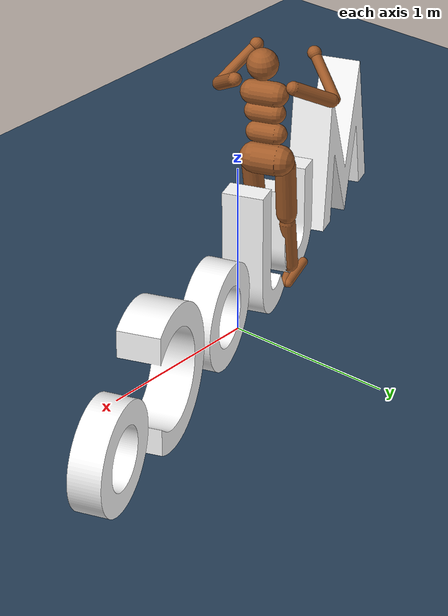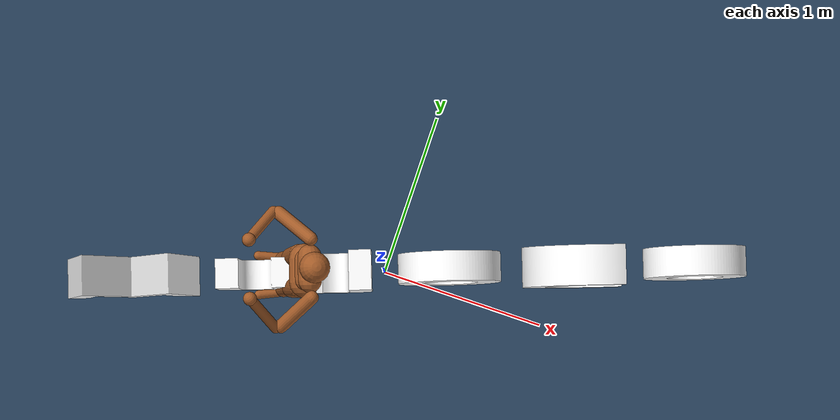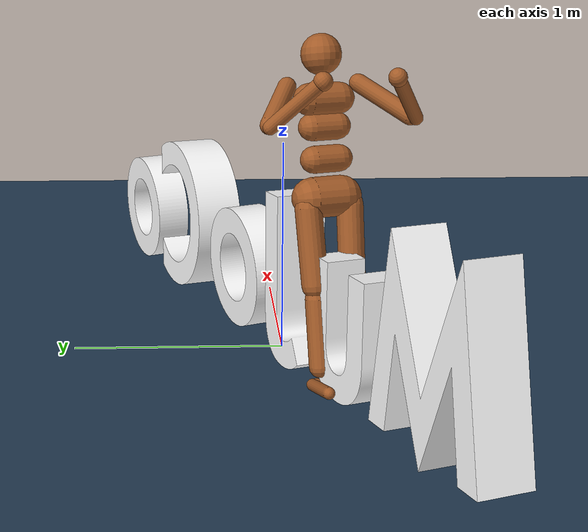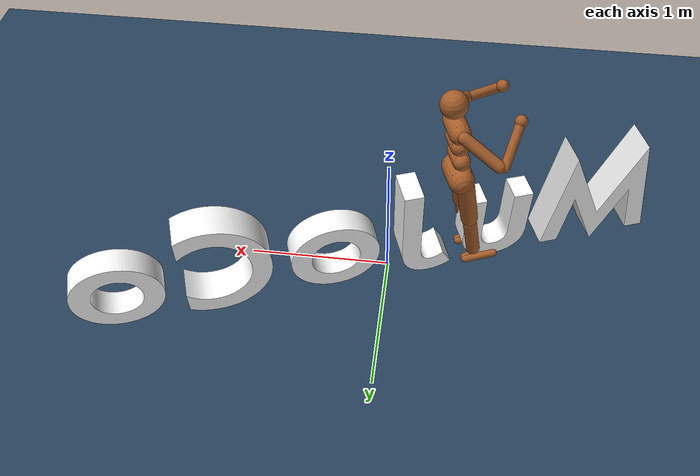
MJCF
<mujoco model="welcome">
  <option timestep="0.02" />
  <default>
    <motor ctrlrange="-1 1" ctrllimited="true" />
    <default class="body">
      <geom type="capsule" condim="1" friction=".7" solimp=".9 .99 .003" solref=".015 1" material="body" group="1" />
      <default class="thigh">
        <geom size=".06" />
      </default>
      <default class="shin">
        <geom fromto="0 0 0 0 0 -.3" size=".049" />
      </default>
      <default class="foot">
        <geom size=".027" />
        <default class="foot1">
          <geom fromto="-.07 -.01 0 .14 -.03 0" />
        </default>
        <default class="foot2">
          <geom fromto="-.07 .01 0 .14  .03 0" />
        </default>
      </default>
      <default class="arm_upper">
        <geom size=".04" />
      </default>
      <default class="arm_lower">
        <geom size=".031" />
      </default>
      <default class="hand">
        <geom type="sphere" size=".04" />
      </default>
      <joint type="hinge" damping=".2" stiffness="1" armature=".01" limited="true" solimplimit="0 .99 .01" />
      <default class="joint_big">
        <joint damping="5" stiffness="10" />
        <default class="hip_x">
          <joint range="-30 10" />
        </default>
        <default class="hip_z">
          <joint range="-60 35" />
        </default>
        <default class="hip_y">
          <joint axis="0 1 0" range="-150 20" />
        </default>
        <default class="joint_big_stiff">
          <joint stiffness="20" />
        </default>
      </default>
      <default class="knee">
        <joint pos="0 0 .02" axis="0 -1 0" range="-160 2" />
      </default>
      <default class="ankle">
        <joint range="-50 50" />
        <default class="ankle_y">
          <joint pos="0 0 .08" axis="0 1 0" stiffness="6" />
        </default>
        <default class="ankle_x">
          <joint pos="0 0 .04" stiffness="3" />
        </default>
      </default>
      <default class="shoulder">
        <joint range="-85 60" />
      </default>
      <default class="elbow">
        <joint range="-100 50" stiffness="0" />
      </default>
    </default>
  </default>
  <visual>
    <global elevation="-15" offwidth="1920" offheight="1080" />
  </visual>
  <default>
    <default class="letter">
      <geom type="mesh" density="4000" material="m1" />
      <default class="letter_visual">
        <geom contype="0" conaffinity="0" group="2" />
      </default>
      <default class="letter_collision">
        <geom group="3" friction="1 0.02 0.001" rgba="0.9 0.3 0.2 0.5" density="0" />
      </default>
    </default>
  </default>
  <worldbody>
    <geom name="floor" size="-1 -1 0.05" type="plane" material="groundplane" />
    <camera name="hero" quat="0.724077 0.611092 -0.206267 -0.244404" pos="-2.736 -3.024 1.152" />
    <camera name="wide" quat="0.788205 0.615412 0 0" pos="0.144 -4.896 1.44" />
    <camera name="sit" quat="0.75774 0.652556 0 0" pos="-0.144 -2.592 0.864" />
    <light intensity="15000" type="image" texture="ibl" />

    <frame euler="0 0 20">

    <light type="directional" dir="0 0 -1" castshadow="true" diffuse="0.5 0.5 0.5" intensity="10000"/>
    <light type="spot" pos="-1.7 0.4 1.2" dir=" 1 -1 -1" diffuse="0.56 0.77 1.00" intensity="600000" range="1.5" castshadow="true" bulbradius="0.25"/>
    <light type="spot" pos=" 0.2 0.6 1.2" dir=" 0 -1 -1" diffuse="1.00 0.77 0.56" intensity="120000" range="4" castshadow="true" bulbradius="0.05"/>
    <light type="spot" pos=" 2.0 0.4 1.2" dir="-1 -1 -1" diffuse="0.56 0.77 1.00" intensity="600000" range="1.5" castshadow="true" bulbradius="0.25"/>

    <body name="letter_m" childclass="letter" pos="-1.94057 0 0.012" quat="0.707106 0.707106 0.000986566 -0.000986566">
      <joint type="free" />
      <geom name="m" class="letter_visual" mesh="m" />
      <geom name="m_00" class="letter_collision" mesh="m_00" />
      <geom name="m_01" class="letter_collision" mesh="m_01" />
      <geom name="m_02" class="letter_collision" mesh="m_02" />
      <geom name="m_03" class="letter_collision" mesh="m_03" />
    </body>
    <body name="letter_u" childclass="letter" pos="-1.00398 0 0.008" quat="0.707092 0.707093 -0.0044939 0.0044939">
      <joint type="free" />
      <geom name="u" class="letter_visual" mesh="u" />
      <geom name="u_00" class="letter_collision" mesh="u_00" />
      <geom name="u_01" class="letter_collision" mesh="u_01" />
      <geom name="u_02" class="letter_collision" mesh="u_02" />
      <geom name="u_03" class="letter_collision" mesh="u_03" />
      <geom name="u_04" class="letter_collision" mesh="u_04" />
      <geom name="u_05" class="letter_collision" mesh="u_05" />
    </body>
    <body name="letter_j" childclass="letter" pos="-0.44100 0 0.011" quat="0.707107 0.707107 0 0">
      <joint type="free" />
      <geom name="j" class="letter_visual" mesh="j" />
      <geom name="j_00" class="letter_collision" mesh="j_00" friction="2.5 0.1 0.01" condim="6" priority="100" />
      <geom name="j_01" class="letter_collision" mesh="j_01" friction="2.5 0.1 0.01" condim="6" priority="100" />
      <geom name="j_02" class="letter_collision" mesh="j_02" friction="2.5 0.1 0.01" condim="6" priority="100" />
      <geom name="j_03" class="letter_collision" mesh="j_03" friction="2.5 0.1 0.01" condim="6" priority="100" />
    </body>
    <body name="letter_o" childclass="letter" pos="0.08442 0 0.010" quat="0.717508 0.696539 1.71146e-05 0.0038991">
      <joint type="free" />
      <geom name="o" class="letter_visual" mesh="o" />
      <geom name="o_00" class="letter_collision" mesh="o_00" />
      <geom name="o_01" class="letter_collision" mesh="o_01" />
      <geom name="o_02" class="letter_collision" mesh="o_02" />
      <geom name="o_03" class="letter_collision" mesh="o_03" />
      <geom name="o_04" class="letter_collision" mesh="o_04" />
      <geom name="o_05" class="letter_collision" mesh="o_05" />
      <geom name="o_06" class="letter_collision" mesh="o_06" />
      <geom name="o_07" class="letter_collision" mesh="o_07" />
      <geom name="o_08" class="letter_collision" mesh="o_08" />
      <geom name="o_09" class="letter_collision" mesh="o_09" />
      <geom name="o_10" class="letter_collision" mesh="o_10" />
      <geom name="o_11" class="letter_collision" mesh="o_11" />
      <geom name="o_12" class="letter_collision" mesh="o_12" />
      <geom name="o_13" class="letter_collision" mesh="o_13" />
      <geom name="o_14" class="letter_collision" mesh="o_14" />
      <geom name="o_15" class="letter_collision" mesh="o_15" />
      <geom name="o_16" class="letter_collision" mesh="o_16" />
      <geom name="o_17" class="letter_collision" mesh="o_17" />
      <geom name="o_18" class="letter_collision" mesh="o_18" />
      <geom name="o_19" class="letter_collision" mesh="o_19" />
      <geom name="o_20" class="letter_collision" mesh="o_20" />
      <geom name="o_21" class="letter_collision" mesh="o_21" />
      <geom name="o_22" class="letter_collision" mesh="o_22" />
      <geom name="o_23" class="letter_collision" mesh="o_23" />
      <geom name="o_24" class="letter_collision" mesh="o_24" />
      <geom name="o_25" class="letter_collision" mesh="o_25" />
      <geom name="o_26" class="letter_collision" mesh="o_26" />
      <geom name="o_27" class="letter_collision" mesh="o_27" />
      <geom name="o_28" class="letter_collision" mesh="o_28" />
      <geom name="o_29" class="letter_collision" mesh="o_29" />
      <geom name="o_30" class="letter_collision" mesh="o_30" />
      <geom name="o_31" class="letter_collision" mesh="o_31" />
    </body>
    <body name="letter_c" childclass="letter" pos="0.83154 0 0.011" quat="0.707107 0.707107 0 0">
      <joint type="free" />
      <geom name="c" class="letter_visual" mesh="c" />
      <geom name="c_00" class="letter_collision" mesh="c_00" />
      <geom name="c_01" class="letter_collision" mesh="c_01" />
      <geom name="c_02" class="letter_collision" mesh="c_02" />
      <geom name="c_03" class="letter_collision" mesh="c_03" />
      <geom name="c_04" class="letter_collision" mesh="c_04" />
      <geom name="c_05" class="letter_collision" mesh="c_05" />
      <geom name="c_06" class="letter_collision" mesh="c_06" />
      <geom name="c_07" class="letter_collision" mesh="c_07" />
      <geom name="c_08" class="letter_collision" mesh="c_08" />
    </body>
    <body name="letter_o2" childclass="letter" pos="1.57005 0 0.010" quat="0.717508 0.696539 1.71146e-05 0.0038991">
      <joint type="free" />
      <geom name="o2" class="letter_visual" mesh="o" />
      <geom name="o2_o_00" class="letter_collision" mesh="o_00" />
      <geom name="o2_o_01" class="letter_collision" mesh="o_01" />
      <geom name="o2_o_02" class="letter_collision" mesh="o_02" />
      <geom name="o2_o_03" class="letter_collision" mesh="o_03" />
      <geom name="o2_o_04" class="letter_collision" mesh="o_04" />
      <geom name="o2_o_05" class="letter_collision" mesh="o_05" />
      <geom name="o2_o_06" class="letter_collision" mesh="o_06" />
      <geom name="o2_o_07" class="letter_collision" mesh="o_07" />
      <geom name="o2_o_08" class="letter_collision" mesh="o_08" />
      <geom name="o2_o_09" class="letter_collision" mesh="o_09" />
      <geom name="o2_o_10" class="letter_collision" mesh="o_10" />
      <geom name="o2_o_11" class="letter_collision" mesh="o_11" />
      <geom name="o2_o_12" class="letter_collision" mesh="o_12" />
      <geom name="o2_o_13" class="letter_collision" mesh="o_13" />
      <geom name="o2_o_14" class="letter_collision" mesh="o_14" />
      <geom name="o2_o_15" class="letter_collision" mesh="o_15" />
      <geom name="o2_o_16" class="letter_collision" mesh="o_16" />
      <geom name="o2_o_17" class="letter_collision" mesh="o_17" />
      <geom name="o2_o_18" class="letter_collision" mesh="o_18" />
      <geom name="o2_o_19" class="letter_collision" mesh="o_19" />
      <geom name="o2_o_20" class="letter_collision" mesh="o_20" />
      <geom name="o2_o_21" class="letter_collision" mesh="o_21" />
      <geom name="o2_o_22" class="letter_collision" mesh="o_22" />
      <geom name="o2_o_23" class="letter_collision" mesh="o_23" />
      <geom name="o2_o_24" class="letter_collision" mesh="o_24" />
      <geom name="o2_o_25" class="letter_collision" mesh="o_25" />
      <geom name="o2_o_26" class="letter_collision" mesh="o_26" />
      <geom name="o2_o_27" class="letter_collision" mesh="o_27" />
      <geom name="o2_o_28" class="letter_collision" mesh="o_28" />
      <geom name="o2_o_29" class="letter_collision" mesh="o_29" />
      <geom name="o2_o_30" class="letter_collision" mesh="o_30" />
      <geom name="o2_o_31" class="letter_collision" mesh="o_31" />
    </body>
    <frame pos="-0.6500 0 0.000" euler="0 10 180">
      <body name="torso" pos="0 0 1.282" childclass="body">
        <camera name="back" pos="-3 0 1" xyaxes="0 -1 0 1 0 2" mode="trackcom" />
        <camera name="side" pos="0 -3 1" xyaxes="1 0 0 0 1 2" mode="trackcom" />
        <freejoint name="root" />
        <geom name="torso" fromto="0 -.07 0 0 .07 0" size=".07" />
        <geom name="waist_upper" fromto="-.01 -.06 -.12 -.01 .06 -.12" size=".06" />
        <body name="head" pos="0 0 .19">
          <geom name="head" type="sphere" size=".09" />
          <camera name="egocentric" pos=".09 0 0" xyaxes="0 -1 0 .1 0 1" fovy="80" />
        </body>
        <body name="waist_lower" pos="-.01 0 -.26">
          <geom name="waist_lower" fromto="0 -.06 0 0 .06 0" size=".06" />
          <joint name="abdomen_z" pos="0 0 .065" axis="0 0 1" range="-45 45" class="joint_big_stiff" />
          <joint name="abdomen_y" pos="0 0 .065" axis="0 1 0" range="-75 30" class="joint_big" />
          <body name="pelvis" pos="0 0 -.165">
            <joint name="abdomen_x" pos="0 0 .1" axis="1 0 0" range="-35 35" class="joint_big" />
            <geom name="butt" fromto="-.02 -.07 0 -.02 .07 0" size=".09" />
            <body name="thigh_right" pos="0 -.1 -.04">
              <joint name="hip_x_right" axis="1 0 0" class="hip_x" />
              <joint name="hip_z_right" axis="0 0 1" class="hip_z" />
              <joint name="hip_y_right" class="hip_y" />
              <geom name="thigh_right" fromto="0 0 0 0 .01 -.34" class="thigh" />
              <body name="shin_right" pos="0 .01 -.4">
                <joint name="knee_right" class="knee" />
                <geom name="shin_right" class="shin" />
                <body name="foot_right" pos="0 0 -.39">
                  <joint name="ankle_y_right" class="ankle_y" />
                  <joint name="ankle_x_right" class="ankle_x" axis="1 0 .5" />
                  <geom name="foot1_right" class="foot1" />
                  <geom name="foot2_right" class="foot2" />
                </body>
              </body>
            </body>
            <body name="thigh_left" pos="0 .1 -.04">
              <joint name="hip_x_left" axis="-1 0 0" class="hip_x" />
              <joint name="hip_z_left" axis="0 0 -1" class="hip_z" />
              <joint name="hip_y_left" class="hip_y" />
              <geom name="thigh_left" fromto="0 0 0 0 -.01 -.34" class="thigh" />
              <body name="shin_left" pos="0 -.01 -.4">
                <joint name="knee_left" class="knee" />
                <geom name="shin_left" class="shin" />
                <body name="foot_left" pos="0 0 -.39">
                  <joint name="ankle_y_left" class="ankle_y" />
                  <joint name="ankle_x_left" class="ankle_x" axis="-1 0 -.5" />
                  <geom name="foot1_left" class="foot1" />
                  <geom name="foot2_left" class="foot2" />
                </body>
              </body>
            </body>
          </body>
        </body>
        <body name="upper_arm_right" pos="0 -.17 .06">
          <joint name="shoulder1_right" axis="2 1 1" class="shoulder" />
          <joint name="shoulder2_right" axis="0 -1 1" class="shoulder" />
          <geom name="upper_arm_right" fromto="0 0 0 .16 -.16 -.16" class="arm_upper" />
          <body name="lower_arm_right" pos=".18 -.18 -.18">
            <joint name="elbow_right" axis="0 -1 1" class="elbow" />
            <geom name="lower_arm_right" fromto=".01 .01 .01 .17 .17 .17" class="arm_lower" />
            <body name="hand_right" pos=".18 .18 .18">
              <geom name="hand_right" zaxis="1 1 1" class="hand" />
            </body>
          </body>
        </body>
        <body name="upper_arm_left" pos="0 .17 .06">
          <joint name="shoulder1_left" axis="-2 1 -1" class="shoulder" />
          <joint name="shoulder2_left" axis="0 -1 -1" class="shoulder" />
          <geom name="upper_arm_left" fromto="0 0 0 .16 .16 -.16" class="arm_upper" />
          <body name="lower_arm_left" pos=".18 .18 -.18">
            <joint name="elbow_left" axis="0 -1 -1" class="elbow" />
            <geom name="lower_arm_left" fromto=".01 -.01 .01 .17 -.17 .17" class="arm_lower" />
            <body name="hand_left" pos=".18 -.18 .18">
              <geom name="hand_left" zaxis="1 -1 1" class="hand" />
            </body>
          </body>
        </body>
      </body>
    </frame>
  </frame>
  </worldbody>
  <custom>
    <numeric name="filament.fog.color" size="3" data="0 0.1 0.2" />
    <numeric name="filament.fog.enabled" data="1" />
    <numeric name="filament.fog.distance" data="10" />
    <numeric name="filament.fog.density" data="0.15" />
    <numeric name="filament.fog.height" data="-1.5" />
    <text    name="filament.shadows.type" data="pcss"/>
    <numeric name="filament.shadows.map_size" data="1024"/>
    <numeric name="filament.bloom.enabled" data="1"/>
    <numeric name="filament.bloom.strength" data="0.3"/>
    <numeric name="filament.vignette.enabled" data="1"/>
    <numeric name="filament.vignette.midpoint" data="0.7"/>
  </custom>
  <contact>
    <exclude body1="waist_lower" body2="thigh_right" />
    <exclude body1="waist_lower" body2="thigh_left" />
  </contact>
  <tendon>
    <fixed name="hamstring_right" limited="true" range="-0.3 2">
      <joint joint="hip_y_right" coef=".5" />
      <joint joint="knee_right" coef="-.5" />
    </fixed>
    <fixed name="hamstring_left" limited="true" range="-0.3 2">
      <joint joint="hip_y_left" coef=".5" />
      <joint joint="knee_left" coef="-.5" />
    </fixed>
  </tendon>
  <actuator>
    <motor name="abdomen_z" gear="40" joint="abdomen_z" />
    <motor name="abdomen_y" gear="40" joint="abdomen_y" />
    <motor name="abdomen_x" gear="40" joint="abdomen_x" />
    <motor name="hip_x_right" gear="40" joint="hip_x_right" />
    <motor name="hip_z_right" gear="40" joint="hip_z_right" />
    <motor name="hip_y_right" gear="120" joint="hip_y_right" />
    <motor name="knee_right" gear="80" joint="knee_right" />
    <motor name="ankle_y_right" gear="20" joint="ankle_y_right" />
    <motor name="ankle_x_right" gear="20" joint="ankle_x_right" />
    <motor name="hip_x_left" gear="40" joint="hip_x_left" />
    <motor name="hip_z_left" gear="40" joint="hip_z_left" />
    <motor name="hip_y_left" gear="120" joint="hip_y_left" />
    <motor name="knee_left" gear="80" joint="knee_left" />
    <motor name="ankle_y_left" gear="20" joint="ankle_y_left" />
    <motor name="ankle_x_left" gear="20" joint="ankle_x_left" />
    <motor name="shoulder1_right" gear="20" joint="shoulder1_right" />
    <motor name="shoulder2_right" gear="20" joint="shoulder2_right" />
    <motor name="elbow_right" gear="40" joint="elbow_right" />
    <motor name="shoulder1_left" gear="20" joint="shoulder1_left" />
    <motor name="shoulder2_left" gear="20" joint="shoulder2_left" />
    <motor name="elbow_left" gear="40" joint="elbow_left" />
  </actuator>
  <asset>
    <texture type="2d" colorspace="auto" name="grid" builtin="checker" rgb1="0.1 0.2 0.3" rgb2="0.2 0.3 0.4" width="512" height="512" />
    <texture type="cube" colorspace="auto" name="ibl" builtin="gradient" rgb1="0.22 0.28 0.38" rgb2="0.8 0.84 0.9" width="64" height="384" />
    <texture type="skybox" colorspace="auto" builtin="gradient" rgb1="0.3 0.5 0.7" rgb2="0 0 0" width="32" height="192" />

    <texture type="2d" builtin="flat" name="white" rgb1="1.0 1.0 1.0" width="4" height="4" />
    <texture type="2d" builtin="flat" name="metallic" rgb1="0.9 0.9 0.9" width="4" height="4" />
    <texture type="2d" builtin="flat" name="roughness" rgb1="0.5 0.5 0.5" width="4" height="4" />
    <texture type="2d" builtin="flat" name="emissive" rgb1="0.03 0.03 0.03" width="4" height="4" />

    <material name="groundplane" texture="grid" texuniform="true" />
    <material name="m1">
      <layer role="rgb" texture="white"/>
      <layer role="metallic" texture="metallic"/>
      <layer role="roughness" texture="roughness"/>
      <layer role="emissive" texture="emissive"/>
    </material>
    <texture name="body" type="cube" builtin="flat" mark="cross" width="128" height="128" rgb1="0.8 0.6 0.4" rgb2="0.8 0.6 0.4" markrgb="1 1 1" />
    <material name="body" texture="body" texuniform="true" rgba="0.8 0.6 .4 1" />
    <mesh name="m" vertex="0.61286 0.48051 0.12  0.67699 0.05701 0.12  0.8073 0.05701 0.12  0.6658 0.8806 0.12  0.40314 0 0.12  0.4062 0.28912 0.12  0.15678 0.88162 0.12  0 0.05803 0.12  0.13031 0.05803 0.12  0.20259 0.48153 0.12  0.61286 0.48051 -0.12  0.8073 0.05701 -0.12  0.67699 0.05701 -0.12  0.6658 0.8806 -0.12  0.40314 0 -0.12  0.4062 0.28912 -0.12  0.15678 0.88162 -0.12  0.13031 0.05803 -0.12  0 0.05803 -0.12  0.20259 0.48153 -0.12  0.67699 0.05701 0.12  0.61286 0.48051 0.12  0.61286 0.48051 -0.12  0.67699 0.05701 -0.12  0.8073 0.05701 0.12  0.67699 0.05701 0.12  0.67699 0.05701 -0.12  0.8073 0.05701 -0.12  0.6658 0.8806 0.12  0.8073 0.05701 0.12  0.8073 0.05701 -0.12  0.6658 0.8806 -0.12  0.4062 0.28912 0.12  0.6658 0.8806 0.12  0.6658 0.8806 -0.12  0.4062 0.28912 -0.12  0.15678 0.88162 0.12  0.4062 0.28912 0.12  0.4062 0.28912 -0.12  0.15678 0.88162 -0.12  0 0.05803 0.12  0.15678 0.88162 0.12  0.15678 0.88162 -0.12  0 0.05803 -0.12  0.13031 0.05803 0.12  0 0.05803 0.12  0 0.05803 -0.12  0.13031 0.05803 -0.12  0.20259 0.48153 0.12  0.13031 0.05803 0.12  0.13031 0.05803 -0.12  0.20259 0.48153 -0.12  0.40314 0 0.12  0.20259 0.48153 0.12  0.20259 0.48153 -0.12  0.40314 0 -0.12  0.61286 0.48051 0.12  0.40314 0 0.12  0.40314 0 -0.12  0.61286 0.48051 -0.12" face="0 1 2  0 2 3  4 0 3  4 3 5  4 5 6  6 7 8  6 8 9  6 9 4  10 11 12  10 13 11  14 13 10  14 15 13  14 16 15  16 17 18  16 19 17  16 14 19  20 21 22  20 22 23  24 25 26  24 26 27  28 29 30  28 30 31  32 33 34  32 34 35  36 37 38  36 38 39  40 41 42  40 42 43  44 45 46  44 46 47  48 49 50  48 50 51  52 53 54  52 54 55  56 57 58  56 58 59" normal="0 0 1  0 0 1  0 0 1  0 0 1  0 0 1  0 0 1  0 0 1  0 0 1  0 0 1  0 0 1  0 0 -1  0 0 -1  0 0 -1  0 0 -1  0 0 -1  0 0 -1  0 0 -1  0 0 -1  0 0 -1  0 0 -1  -0.9887 -0.1497 0  -0.9887 -0.1497 0  -0.9887 -0.1497 0  -0.9887 -0.1497 0  0 -1 0  0 -1 0  0 -1 0  0 -1 0  0.9856 0.1693 0  0.9856 0.1693 0  0.9856 0.1693 0  0.9856 0.1693 0  -0.9157 0.4019 0  -0.9157 0.4019 0  -0.9157 0.4019 0  -0.9157 0.4019 0  0.9217 0.388 0  0.9217 0.388 0  0.9217 0.388 0  0.9217 0.388 0  -0.9824 0.187 0  -0.9824 0.187 0  -0.9824 0.187 0  -0.9824 0.187 0  0 -1 0  0 -1 0  0 -1 0  0 -1 0  0.9857 -0.1682 0  0.9857 -0.1682 0  0.9857 -0.1682 0  0.9857 -0.1682 0  -0.9231 -0.3845 0  -0.9231 -0.3845 0  -0.9231 -0.3845 0  -0.9231 -0.3845 0  0.9165 -0.4 0  0.9165 -0.4 0  0.9165 -0.4 0  0.9165 -0.4 0" />
    <mesh name="u" vertex="0.23822 -0.00204 0.09  0.24675 -0.00194 0.09  0.25516 -0.00165 0.09  0.26345 -0.00116 0.09  0.27161 -0.00048 0.09  0.27965 0.00041 0.09  0.28756 0.00151 0.09  0.29534 0.00281 0.09  0.30299 0.00433 0.09  0.31051 0.00606 0.09  0.3179 0.008 0.09  0.32516 0.01017 0.09  0.33228 0.01257 0.09  0.33926 0.01519 0.09  0.3461 0.01803 0.09  0.3528 0.02112 0.09  0.35937 0.02443 0.09  0.36613 0.02777 0.09  0.37268 0.03131 0.09  0.37903 0.03503 0.09  0.38517 0.03896 0.09  0.3911 0.04308 0.09  0.39684 0.04739 0.09  0.40238 0.05191 0.09  0.40772 0.05663 0.09  0.41288 0.06155 0.09  0.41784 0.06667 0.09  0.42263 0.07201 0.09  0.42723 0.07755 0.09  0.43165 0.08329 0.09  0.43589 0.08925 0.09  0.43996 0.09542 0.09  0.44386 0.1018 0.09  0.44756 0.10821 0.09  0.45102 0.11482 0.09  0.45424 0.12165 0.09  0.45722 0.12867 0.09  0.45997 0.13589 0.09  0.46248 0.1433 0.09  0.46474 0.1509 0.09  0.46677 0.15869 0.09  0.46856 0.16665 0.09  0.47011 0.17479 0.09  0.47142 0.18309 0.09  0.4725 0.19157 0.09  0.47333 0.2002 0.09  0.47393 0.20899 0.09  0.47429 0.21793 0.09  0.47441 0.22702 0.09  0.47441 0.58842 0.09  0.33595 0.58842 0.09  0.33595 0.24229 0.09  0.3359 0.23701 0.09  0.33576 0.23184 0.09  0.33553 0.2268 0.09  0.3352 0.22188 0.09  0.33479 0.21709 0.09  0.33429 0.21243 0.09  0.3337 0.20789 0.09  0.33303 0.20348 0.09  0.33227 0.1992 0.09  0.33143 0.19506 0.09  0.33051 0.19105 0.09  0.32951 0.18718 0.09  0.32843 0.18344 0.09  0.32728 0.17984 0.09  0.32605 0.17638 0.09  0.32475 0.17307 0.09  0.32319 0.16987 0.09  0.32156 0.16677 0.09  0.31985 0.16376 0.09  0.31807 0.16085 0.09  0.31622 0.15803 0.09  0.3143 0.15531 0.09  0.31231 0.15269 0.09  0.31025 0.15016 0.09  0.30811 0.14773 0.09  0.3059 0.14539 0.09  0.30362 0.14314 0.09  0.30128 0.141 0.09  0.29885 0.13895 0.09  0.29636 0.13699 0.09  0.29379 0.13513 0.09  0.29116 0.13336 0.09  0.28844 0.1317 0.09  0.28563 0.13016 0.09  0.28272 0.12874 0.09  0.27972 0.12743 0.09  0.27664 0.12623 0.09  0.27346 0.12515 0.09  0.2702 0.12417 0.09  0.26685 0.12331 0.09  0.26342 0.12255 0.09  0.25991 0.1219 0.09  0.25632 0.12135 0.09  0.25265 0.12091 0.09  0.2489 0.12056 0.09  0.24507 0.12032 0.09  0.24118 0.12018 0.09  0.2372 0.12013 0.09  0.23324 0.12018 0.09  0.22937 0.12032 0.09  0.22559 0.12056 0.09  0.2219 0.12091 0.09  0.21829 0.12135 0.09  0.21476 0.1219 0.09  0.21131 0.12255 0.09  0.20793 0.12331 0.09  0.20463 0.12417 0.09  0.20139 0.12515 0.09  0.19822 0.12623 0.09  0.19511 0.12743 0.09  0.19206 0.12874 0.09  0.18907 0.13016 0.09  0.18613 0.1317 0.09  0.18325 0.13336 0.09  0.18043 0.13513 0.09  0.17771 0.13699 0.09  0.17509 0.13895 0.09  0.17256 0.141 0.09  0.17012 0.14314 0.09  0.16778 0.14539 0.09  0.16554 0.14773 0.09  0.1634 0.15016 0.09  0.16134 0.15269 0.09  0.15939 0.15531 0.09  0.15752 0.15803 0.09  0.15576 0.16085 0.09  0.15409 0.16376 0.09  0.15251 0.16677 0.09  0.13845 0.24127 0.09  0.13845 0.58842 0.09  0 0.58842 0.09  0.1385 0.236 0.09  0.13864 0.23087 0.09  0.13888 0.22588 0.09  0.1392 0.22102 0.09  0.13961 0.21631 0.09  0.14012 0.21173 0.09  0.14071 0.20728 0.09  0.14138 0.20297 0.09  0.14214 0.19879 0.09  0.14298 0.19474 0.09  0.1439 0.19081 0.09  0.14489 0.18702 0.09  0.14597 0.18335 0.09  0.14712 0.1798 0.09  0.14835 0.17637 0.09  0 0.22702 0.09  0.14965 0.17307 0.09  0.15104 0.16987 0.09  0.00012 0.21794 0.09  0.00048 0.20903 0.09  0.00107 0.20029 0.09  0.00191 0.19171 0.09  0.00298 0.1833 0.09  0.0043 0.17505 0.09  0.00585 0.16698 0.09  0.00764 0.15907 0.09  0.00966 0.15132 0.09  0.01193 0.14375 0.09  0.01443 0.13634 0.09  0.01718 0.1291 0.09  0.02016 0.12202 0.09  0.02338 0.11512 0.09  0.02684 0.10838 0.09  0.03054 0.1018 0.09  0.03445 0.09559 0.09  0.03856 0.08954 0.09  0.04285 0.08367 0.09  0.04732 0.07798 0.09  0.05198 0.07246 0.09  0.05683 0.06712 0.09  0.06186 0.06197 0.09  0.06706 0.05701 0.09  0.07245 0.05224 0.09  0.07801 0.04766 0.09  0.08375 0.04328 0.09  0.08967 0.0391 0.09  0.09575 0.03512 0.09  0.10201 0.03135 0.09  0.10844 0.02779 0.09  0.11504 0.02443 0.09  0.12179 0.02128 0.09  0.12868 0.01833 0.09  0.13571 0.01556 0.09  0.14288 0.013 0.09  0.15017 0.01063 0.09  0.15759 0.00845 0.09  0.16514 0.00648 0.09  0.17281 0.00471 0.09  0.1806 0.00314 0.09  0.18851 0.00178 0.09  0.19653 0.00062 0.09  0.20466 -0.00033 0.09  0.21289 -0.00108 0.09  0.22124 -0.00161 0.09  0.22968 -0.00193 0.09  0.23822 -0.00204 -0.09  0.25516 -0.00165 -0.09  0.24675 -0.00194 -0.09  0.26345 -0.00116 -0.09  0.27161 -0.00048 -0.09  0.27965 0.00041 -0.09  0.28756 0.00151 -0.09  0.29534 0.00281 -0.09  0.30299 0.00433 -0.09  0.31051 0.00606 -0.09  0.3179 0.008 -0.09  0.32516 0.01017 -0.09  0.33228 0.01257 -0.09  0.33926 0.01519 -0.09  0.3461 0.01803 -0.09  0.3528 0.02112 -0.09  0.35937 0.02443 -0.09  0.36613 0.02777 -0.09  0.37268 0.03131 -0.09  0.37903 0.03503 -0.09  0.38517 0.03896 -0.09  0.3911 0.04308 -0.09  0.39684 0.04739 -0.09  0.40238 0.05191 -0.09  0.40772 0.05663 -0.09  0.41288 0.06155 -0.09  0.41784 0.06667 -0.09  0.42263 0.07201 -0.09  0.42723 0.07755 -0.09  0.43165 0.08329 -0.09  0.43589 0.08925 -0.09  0.43996 0.09542 -0.09  0.44386 0.1018 -0.09  0.44756 0.10821 -0.09  0.45102 0.11482 -0.09  0.45424 0.12165 -0.09  0.45722 0.12867 -0.09  0.45997 0.13589 -0.09  0.46248 0.1433 -0.09  0.46474 0.1509 -0.09  0.46677 0.15869 -0.09  0.46856 0.16665 -0.09  0.47011 0.17479 -0.09  0.47142 0.18309 -0.09  0.4725 0.19157 -0.09  0.47333 0.2002 -0.09  0.47393 0.20899 -0.09  0.47429 0.21793 -0.09  0.47441 0.22702 -0.09  0.33595 0.58842 -0.09  0.47441 0.58842 -0.09  0.33595 0.24229 -0.09  0.3359 0.23701 -0.09  0.33576 0.23184 -0.09  0.33553 0.2268 -0.09  0.3352 0.22188 -0.09  0.33479 0.21709 -0.09  0.33429 0.21243 -0.09  0.3337 0.20789 -0.09  0.33303 0.20348 -0.09  0.33227 0.1992 -0.09  0.33143 0.19506 -0.09  0.33051 0.19105 -0.09  0.32951 0.18718 -0.09  0.32843 0.18344 -0.09  0.32728 0.17984 -0.09  0.32605 0.17638 -0.09  0.32475 0.17307 -0.09  0.32319 0.16987 -0.09  0.32156 0.16677 -0.09  0.31985 0.16376 -0.09  0.31807 0.16085 -0.09  0.31622 0.15803 -0.09  0.3143 0.15531 -0.09  0.31231 0.15269 -0.09  0.31025 0.15016 -0.09  0.30811 0.14773 -0.09  0.3059 0.14539 -0.09  0.30362 0.14314 -0.09  0.30128 0.141 -0.09  0.29885 0.13895 -0.09  0.29636 0.13699 -0.09  0.29379 0.13513 -0.09  0.29116 0.13336 -0.09  0.28844 0.1317 -0.09  0.28563 0.13016 -0.09  0.28272 0.12874 -0.09  0.27972 0.12743 -0.09  0.27664 0.12623 -0.09  0.27346 0.12515 -0.09  0.2702 0.12417 -0.09  0.26685 0.12331 -0.09  0.26342 0.12255 -0.09  0.25991 0.1219 -0.09  0.25632 0.12135 -0.09  0.25265 0.12091 -0.09  0.2489 0.12056 -0.09  0.24507 0.12032 -0.09  0.24118 0.12018 -0.09  0.2372 0.12013 -0.09  0.23324 0.12018 -0.09  0.22937 0.12032 -0.09  0.22559 0.12056 -0.09  0.2219 0.12091 -0.09  0.21829 0.12135 -0.09  0.21476 0.1219 -0.09  0.21131 0.12255 -0.09  0.20793 0.12331 -0.09  0.20463 0.12417 -0.09  0.20139 0.12515 -0.09  0.19822 0.12623 -0.09  0.19511 0.12743 -0.09  0.19206 0.12874 -0.09  0.18907 0.13016 -0.09  0.18613 0.1317 -0.09  0.18325 0.13336 -0.09  0.18043 0.13513 -0.09  0.17771 0.13699 -0.09  0.17509 0.13895 -0.09  0.17256 0.141 -0.09  0.17012 0.14314 -0.09  0.16778 0.14539 -0.09  0.16554 0.14773 -0.09  0.1634 0.15016 -0.09  0.16134 0.15269 -0.09  0.15939 0.15531 -0.09  0.15752 0.15803 -0.09  0.15576 0.16085 -0.09  0.15409 0.16376 -0.09  0.15251 0.16677 -0.09  0.13845 0.24127 -0.09  0 0.58842 -0.09  0.13845 0.58842 -0.09  0.1385 0.236 -0.09  0.13864 0.23087 -0.09  0.13888 0.22588 -0.09  0.1392 0.22102 -0.09  0.13961 0.21631 -0.09  0.14012 0.21173 -0.09  0.14071 0.20728 -0.09  0.14138 0.20297 -0.09  0.14214 0.19879 -0.09  0.14298 0.19474 -0.09  0.1439 0.19081 -0.09  0.14489 0.18702 -0.09  0.14597 0.18335 -0.09  0.14712 0.1798 -0.09  0.14835 0.17637 -0.09  0 0.22702 -0.09  0.14965 0.17307 -0.09  0.15104 0.16987 -0.09  0.00012 0.21794 -0.09  0.00048 0.20903 -0.09  0.00107 0.20029 -0.09  0.00191 0.19171 -0.09  0.00298 0.1833 -0.09  0.0043 0.17505 -0.09  0.00585 0.16698 -0.09  0.00764 0.15907 -0.09  0.00966 0.15132 -0.09  0.01193 0.14375 -0.09  0.01443 0.13634 -0.09  0.01718 0.1291 -0.09  0.02016 0.12202 -0.09  0.02338 0.11512 -0.09  0.02684 0.10838 -0.09  0.03054 0.1018 -0.09  0.03445 0.09559 -0.09  0.03856 0.08954 -0.09  0.04285 0.08367 -0.09  0.04732 0.07798 -0.09  0.05198 0.07246 -0.09  0.05683 0.06712 -0.09  0.06186 0.06197 -0.09  0.06706 0.05701 -0.09  0.07245 0.05224 -0.09  0.07801 0.04766 -0.09  0.08375 0.04328 -0.09  0.08967 0.0391 -0.09  0.09575 0.03512 -0.09  0.10201 0.03135 -0.09  0.10844 0.02779 -0.09  0.11504 0.02443 -0.09  0.12179 0.02128 -0.09  0.12868 0.01833 -0.09  0.13571 0.01556 -0.09  0.14288 0.013 -0.09  0.15017 0.01063 -0.09  0.15759 0.00845 -0.09  0.16514 0.00648 -0.09  0.17281 0.00471 -0.09  0.1806 0.00314 -0.09  0.18851 0.00178 -0.09  0.19653 0.00062 -0.09  0.20466 -0.00033 -0.09  0.21289 -0.00108 -0.09  0.22124 -0.00161 -0.09  0.22968 -0.00193 -0.09  0.25516 -0.00165 0.09  0.24675 -0.00194 0.09  0.24675 -0.00194 -0.09  0.25516 -0.00165 -0.09  0.26345 -0.00116 0.09  0.26345 -0.00116 -0.09  0.27161 -0.00048 0.09  0.27161 -0.00048 -0.09  0.27965 0.00041 0.09  0.27965 0.00041 -0.09  0.28756 0.00151 0.09  0.28756 0.00151 -0.09  0.29534 0.00281 0.09  0.29534 0.00281 -0.09  0.30299 0.00433 0.09  0.30299 0.00433 -0.09  0.31051 0.00606 0.09  0.31051 0.00606 -0.09  0.3179 0.008 0.09  0.3179 0.008 -0.09  0.32516 0.01017 0.09  0.32516 0.01017 -0.09  0.33228 0.01257 0.09  0.33228 0.01257 -0.09  0.33926 0.01519 0.09  0.33926 0.01519 -0.09  0.3461 0.01803 0.09  0.3461 0.01803 -0.09  0.3528 0.02112 0.09  0.3528 0.02112 -0.09  0.35937 0.02443 0.09  0.35937 0.02443 -0.09  0.36613 0.02777 0.09  0.36613 0.02777 -0.09  0.37268 0.03131 0.09  0.37268 0.03131 -0.09  0.37903 0.03503 0.09  0.37903 0.03503 -0.09  0.38517 0.03896 0.09  0.38517 0.03896 -0.09  0.3911 0.04308 0.09  0.3911 0.04308 -0.09  0.39684 0.04739 0.09  0.39684 0.04739 -0.09  0.40238 0.05191 0.09  0.40238 0.05191 -0.09  0.40772 0.05663 0.09  0.40772 0.05663 -0.09  0.41288 0.06155 0.09  0.41288 0.06155 -0.09  0.41784 0.06667 0.09  0.41784 0.06667 -0.09  0.42263 0.07201 0.09  0.42263 0.07201 -0.09  0.42723 0.07755 0.09  0.42723 0.07755 -0.09  0.43165 0.08329 0.09  0.43165 0.08329 -0.09  0.43589 0.08925 0.09  0.43589 0.08925 -0.09  0.43996 0.09542 0.09  0.43996 0.09542 -0.09  0.44386 0.1018 0.09  0.44386 0.1018 -0.09  0.44756 0.10821 0.09  0.44756 0.10821 -0.09  0.45102 0.11482 0.09  0.45102 0.11482 -0.09  0.45424 0.12165 0.09  0.45424 0.12165 -0.09  0.45722 0.12867 0.09  0.45722 0.12867 -0.09  0.45997 0.13589 0.09  0.45997 0.13589 -0.09  0.46248 0.1433 0.09  0.46248 0.1433 -0.09  0.46474 0.1509 0.09  0.46474 0.1509 -0.09  0.46677 0.15869 0.09  0.46677 0.15869 -0.09  0.46856 0.16665 0.09  0.46856 0.16665 -0.09  0.47011 0.17479 0.09  0.47011 0.17479 -0.09  0.47142 0.18309 0.09  0.47142 0.18309 -0.09  0.4725 0.19157 0.09  0.4725 0.19157 -0.09  0.47333 0.2002 0.09  0.47333 0.2002 -0.09  0.47393 0.20899 0.09  0.47393 0.20899 -0.09  0.47429 0.21793 0.09  0.47429 0.21793 -0.09  0.47441 0.22702 0.09  0.47441 0.22702 -0.09  0.47441 0.58842 0.09  0.47441 0.58842 -0.09  0.33595 0.58842 0.09  0.47441 0.58842 0.09  0.47441 0.58842 -0.09  0.33595 0.58842 -0.09  0.33595 0.24229 0.09  0.33595 0.58842 0.09  0.33595 0.58842 -0.09  0.33595 0.24229 -0.09  0.3359 0.23701 0.09  0.3359 0.23701 -0.09  0.33576 0.23184 0.09  0.33576 0.23184 -0.09  0.33553 0.2268 0.09  0.33553 0.2268 -0.09  0.3352 0.22188 0.09  0.3352 0.22188 -0.09  0.33479 0.21709 0.09  0.33479 0.21709 -0.09  0.33429 0.21243 0.09  0.33429 0.21243 -0.09  0.3337 0.20789 0.09  0.3337 0.20789 -0.09  0.33303 0.20348 0.09  0.33303 0.20348 -0.09  0.33227 0.1992 0.09  0.33227 0.1992 -0.09  0.33143 0.19506 0.09  0.33143 0.19506 -0.09  0.33051 0.19105 0.09  0.33051 0.19105 -0.09  0.32951 0.18718 0.09  0.32951 0.18718 -0.09  0.32843 0.18344 0.09  0.32843 0.18344 -0.09  0.32728 0.17984 0.09  0.32728 0.17984 -0.09  0.32605 0.17638 0.09  0.32605 0.17638 -0.09  0.32475 0.17307 0.09  0.32475 0.17307 -0.09  0.32319 0.16987 0.09  0.32319 0.16987 -0.09  0.32156 0.16677 0.09  0.32156 0.16677 -0.09  0.31985 0.16376 0.09  0.31985 0.16376 -0.09  0.31807 0.16085 0.09  0.31807 0.16085 -0.09  0.31622 0.15803 0.09  0.31622 0.15803 -0.09  0.3143 0.15531 0.09  0.3143 0.15531 -0.09  0.31231 0.15269 0.09  0.31231 0.15269 -0.09  0.31025 0.15016 0.09  0.31025 0.15016 -0.09  0.30811 0.14773 0.09  0.30811 0.14773 -0.09  0.3059 0.14539 0.09  0.3059 0.14539 -0.09  0.30362 0.14314 0.09  0.30362 0.14314 -0.09  0.30128 0.141 0.09  0.30128 0.141 -0.09  0.29885 0.13895 0.09  0.29885 0.13895 -0.09  0.29636 0.13699 0.09  0.29636 0.13699 -0.09  0.29379 0.13513 0.09  0.29379 0.13513 -0.09  0.29116 0.13336 0.09  0.29116 0.13336 -0.09  0.28844 0.1317 0.09  0.28844 0.1317 -0.09  0.28563 0.13016 0.09  0.28563 0.13016 -0.09  0.28272 0.12874 0.09  0.28272 0.12874 -0.09  0.27972 0.12743 0.09  0.27972 0.12743 -0.09  0.27664 0.12623 0.09  0.27664 0.12623 -0.09  0.27346 0.12515 0.09  0.27346 0.12515 -0.09  0.2702 0.12417 0.09  0.2702 0.12417 -0.09  0.26685 0.12331 0.09  0.26685 0.12331 -0.09  0.26342 0.12255 0.09  0.26342 0.12255 -0.09  0.25991 0.1219 0.09  0.25991 0.1219 -0.09  0.25632 0.12135 0.09  0.25632 0.12135 -0.09  0.25265 0.12091 0.09  0.25265 0.12091 -0.09  0.2489 0.12056 0.09  0.2489 0.12056 -0.09  0.24507 0.12032 0.09  0.24507 0.12032 -0.09  0.24118 0.12018 0.09  0.24118 0.12018 -0.09  0.2372 0.12013 0.09  0.2372 0.12013 -0.09  0.23324 0.12018 0.09  0.23324 0.12018 -0.09  0.22937 0.12032 0.09  0.22937 0.12032 -0.09  0.22559 0.12056 0.09  0.22559 0.12056 -0.09  0.2219 0.12091 0.09  0.2219 0.12091 -0.09  0.21829 0.12135 0.09  0.21829 0.12135 -0.09  0.21476 0.1219 0.09  0.21476 0.1219 -0.09  0.21131 0.12255 0.09  0.21131 0.12255 -0.09  0.20793 0.12331 0.09  0.20793 0.12331 -0.09  0.20463 0.12417 0.09  0.20463 0.12417 -0.09  0.20139 0.12515 0.09  0.20139 0.12515 -0.09  0.19822 0.12623 0.09  0.19822 0.12623 -0.09  0.19511 0.12743 0.09  0.19511 0.12743 -0.09  0.19206 0.12874 0.09  0.19206 0.12874 -0.09  0.18907 0.13016 0.09  0.18907 0.13016 -0.09  0.18613 0.1317 0.09  0.18613 0.1317 -0.09  0.18325 0.13336 0.09  0.18325 0.13336 -0.09  0.18043 0.13513 0.09  0.18043 0.13513 -0.09  0.17771 0.13699 0.09  0.17771 0.13699 -0.09  0.17509 0.13895 0.09  0.17509 0.13895 -0.09  0.17256 0.141 0.09  0.17256 0.141 -0.09  0.17012 0.14314 0.09  0.17012 0.14314 -0.09  0.16778 0.14539 0.09  0.16778 0.14539 -0.09  0.16554 0.14773 0.09  0.16554 0.14773 -0.09  0.1634 0.15016 0.09  0.1634 0.15016 -0.09  0.16134 0.15269 0.09  0.16134 0.15269 -0.09  0.15939 0.15531 0.09  0.15939 0.15531 -0.09  0.15752 0.15803 0.09  0.15752 0.15803 -0.09  0.15576 0.16085 0.09  0.15576 0.16085 -0.09  0.15409 0.16376 0.09  0.15409 0.16376 -0.09  0.15251 0.16677 0.09  0.15251 0.16677 -0.09  0.15104 0.16987 0.09  0.15104 0.16987 -0.09  0.14965 0.17307 0.09  0.14965 0.17307 -0.09  0.14835 0.17637 0.09  0.14835 0.17637 -0.09  0.14712 0.1798 0.09  0.14712 0.1798 -0.09  0.14597 0.18335 0.09  0.14597 0.18335 -0.09  0.14489 0.18702 0.09  0.14489 0.18702 -0.09  0.1439 0.19081 0.09  0.1439 0.19081 -0.09  0.14298 0.19474 0.09  0.14298 0.19474 -0.09  0.14214 0.19879 0.09  0.14214 0.19879 -0.09  0.14138 0.20297 0.09  0.14138 0.20297 -0.09  0.14071 0.20728 0.09  0.14071 0.20728 -0.09  0.14012 0.21173 0.09  0.14012 0.21173 -0.09  0.13961 0.21631 0.09  0.13961 0.21631 -0.09  0.1392 0.22102 0.09  0.1392 0.22102 -0.09  0.13888 0.22588 0.09  0.13888 0.22588 -0.09  0.13864 0.23087 0.09  0.13864 0.23087 -0.09  0.1385 0.236 0.09  0.1385 0.236 -0.09  0.13845 0.24127 0.09  0.13845 0.24127 -0.09  0.13845 0.58842 0.09  0.13845 0.58842 -0.09  0 0.58842 0.09  0.13845 0.58842 0.09  0.13845 0.58842 -0.09  0 0.58842 -0.09  0 0.22702 0.09  0 0.58842 0.09  0 0.58842 -0.09  0 0.22702 -0.09  0.00012 0.21794 0.09  0.00012 0.21794 -0.09  0.00048 0.20903 0.09  0.00048 0.20903 -0.09  0.00107 0.20029 0.09  0.00107 0.20029 -0.09  0.00191 0.19171 0.09  0.00191 0.19171 -0.09  0.00298 0.1833 0.09  0.00298 0.1833 -0.09  0.0043 0.17505 0.09  0.0043 0.17505 -0.09  0.00585 0.16698 0.09  0.00585 0.16698 -0.09  0.00764 0.15907 0.09  0.00764 0.15907 -0.09  0.00966 0.15132 0.09  0.00966 0.15132 -0.09  0.01193 0.14375 0.09  0.01193 0.14375 -0.09  0.01443 0.13634 0.09  0.01443 0.13634 -0.09  0.01718 0.1291 0.09  0.01718 0.1291 -0.09  0.02016 0.12202 0.09  0.02016 0.12202 -0.09  0.02338 0.11512 0.09  0.02338 0.11512 -0.09  0.02684 0.10838 0.09  0.02684 0.10838 -0.09  0.03054 0.1018 0.09  0.03054 0.1018 -0.09  0.03445 0.09559 0.09  0.03445 0.09559 -0.09  0.03856 0.08954 0.09  0.03856 0.08954 -0.09  0.04285 0.08367 0.09  0.04285 0.08367 -0.09  0.04732 0.07798 0.09  0.04732 0.07798 -0.09  0.05198 0.07246 0.09  0.05198 0.07246 -0.09  0.05683 0.06712 0.09  0.05683 0.06712 -0.09  0.06186 0.06197 0.09  0.06186 0.06197 -0.09  0.06706 0.05701 0.09  0.06706 0.05701 -0.09  0.07245 0.05224 0.09  0.07245 0.05224 -0.09  0.07801 0.04766 0.09  0.07801 0.04766 -0.09  0.08375 0.04328 0.09  0.08375 0.04328 -0.09  0.08967 0.0391 0.09  0.08967 0.0391 -0.09  0.09575 0.03512 0.09  0.09575 0.03512 -0.09  0.10201 0.03135 0.09  0.10201 0.03135 -0.09  0.10844 0.02779 0.09  0.10844 0.02779 -0.09  0.11504 0.02443 0.09  0.11504 0.02443 -0.09  0.12179 0.02128 0.09  0.12179 0.02128 -0.09  0.12868 0.01833 0.09  0.12868 0.01833 -0.09  0.13571 0.01556 0.09  0.13571 0.01556 -0.09  0.14288 0.013 0.09  0.14288 0.013 -0.09  0.15017 0.01063 0.09  0.15017 0.01063 -0.09  0.15759 0.00845 0.09  0.15759 0.00845 -0.09  0.16514 0.00648 0.09  0.16514 0.00648 -0.09  0.17281 0.00471 0.09  0.17281 0.00471 -0.09  0.1806 0.00314 0.09  0.1806 0.00314 -0.09  0.18851 0.00178 0.09  0.18851 0.00178 -0.09  0.19653 0.00062 0.09  0.19653 0.00062 -0.09  0.20466 -0.00033 0.09  0.20466 -0.00033 -0.09  0.21289 -0.00108 0.09  0.21289 -0.00108 -0.09  0.22124 -0.00161 0.09  0.22124 -0.00161 -0.09  0.22968 -0.00193 0.09  0.22968 -0.00193 -0.09  0.23822 -0.00204 0.09  0.23822 -0.00204 -0.09" face="0 1 2  0 2 3  0 3 4  0 4 5  0 5 6  0 6 7  0 7 8  0 8 9  0 9 10  0 10 11  0 11 12  0 12 13  0 13 14  0 14 15  0 15 16  0 16 17  0 17 18  0 18 19  0 19 20  0 20 21  0 21 22  0 22 23  0 23 24  0 24 25  0 25 26  0 26 27  0 27 28  0 28 29  0 29 30  0 30 31  0 31 32  0 32 33  0 33 34  0 34 35  0 35 36  0 36 37  0 37 38  0 38 39  0 39 40  0 40 41  0 41 42  0 42 43  0 43 44  0 44 45  0 45 46  0 46 47  0 47 48  48 49 50  48 50 51  48 51 52  48 52 53  48 53 54  48 54 55  48 55 56  48 56 57  48 57 58  48 58 59  48 59 60  48 60 61  48 61 62  48 62 63  48 63 64  48 64 65  48 65 66  48 66 67  48 67 68  0 48 68  0 68 69  0 69 70  0 70 71  0 71 72  0 72 73  0 73 74  0 74 75  0 75 76  0 76 77  0 77 78  0 78 79  0 79 80  0 80 81  0 81 82  0 82 83  0 83 84  0 84 85  0 85 86  0 86 87  0 87 88  0 88 89  0 89 90  0 90 91  0 91 92  0 92 93  0 93 94  0 94 95  0 95 96  0 96 97  0 97 98  0 98 99  0 99 100  0 100 101  0 101 102  0 102 103  0 103 104  0 104 105  0 105 106  0 106 107  0 107 108  0 108 109  0 109 110  0 110 111  0 111 112  0 112 113  0 113 114  0 114 115  0 115 116  0 116 117  0 117 118  0 118 119  0 119 120  0 120 121  0 121 122  0 122 123  0 123 124  0 124 125  0 125 126  0 126 127  0 127 128  0 128 129  130 131 132  133 130 132  134 133 132  135 134 132  136 135 132  137 136 132  138 137 132  139 138 132  140 139 132  141 140 132  142 141 132  143 142 132  144 143 132  145 144 132  146 145 132  147 146 132  147 132 148  149 147 148  150 149 148  129 150 148  0 129 148  0 148 151  0 151 152  0 152 153  0 153 154  0 154 155  0 155 156  0 156 157  0 157 158  0 158 159  0 159 160  0 160 161  0 161 162  0 162 163  0 163 164  0 164 165  0 165 166  0 166 167  0 167 168  0 168 169  0 169 170  0 170 171  0 171 172  0 172 173  0 173 174  0 174 175  0 175 176  0 176 177  0 177 178  0 178 179  0 179 180  0 180 181  0 181 182  0 182 183  0 183 184  0 184 185  0 185 186  0 186 187  0 187 188  0 188 189  0 189 190  0 190 191  0 191 192  0 192 193  0 193 194  0 194 195  0 195 196  196 197 0  198 199 200  198 201 199  198 202 201  198 203 202  198 204 203  198 205 204  198 206 205  198 207 206  198 208 207  198 209 208  198 210 209  198 211 210  198 212 211  198 213 212  198 214 213  198 215 214  198 216 215  198 217 216  198 218 217  198 219 218  198 220 219  198 221 220  198 222 221  198 223 222  198 224 223  198 225 224  198 226 225  198 227 226  198 228 227  198 229 228  198 230 229  198 231 230  198 232 231  198 233 232  198 234 233  198 235 234  198 236 235  198 237 236  198 238 237  198 239 238  198 240 239  198 241 240  198 242 241  198 243 242  198 244 243  198 245 244  198 246 245  246 247 248  246 249 247  246 250 249  246 251 250  246 252 251  246 253 252  246 254 253  246 255 254  246 256 255  246 257 256  246 258 257  246 259 258  246 260 259  246 261 260  246 262 261  246 263 262  246 264 263  246 265 264  246 266 265  198 266 246  198 267 266  198 268 267  198 269 268  198 270 269  198 271 270  198 272 271  198 273 272  198 274 273  198 275 274  198 276 275  198 277 276  198 278 277  198 279 278  198 280 279  198 281 280  198 282 281  198 283 282  198 284 283  198 285 284  198 286 285  198 287 286  198 288 287  198 289 288  198 290 289  198 291 290  198 292 291  198 293 292  198 294 293  198 295 294  198 296 295  198 297 296  198 298 297  198 299 298  198 300 299  198 301 300  198 302 301  198 303 302  198 304 303  198 305 304  198 306 305  198 307 306  198 308 307  198 309 308  198 310 309  198 311 310  198 312 311  198 313 312  198 314 313  198 315 314  198 316 315  198 317 316  198 318 317  198 319 318  198 320 319  198 321 320  198 322 321  198 323 322  198 324 323  198 325 324  198 326 325  198 327 326  328 329 330  331 329 328  332 329 331  333 329 332  334 329 333  335 329 334  336 329 335  337 329 336  338 329 337  339 329 338  340 329 339  341 329 340  342 329 341  343 329 342  344 329 343  345 329 344  345 346 329  347 346 345  348 346 347  327 346 348  198 346 327  198 349 346  198 350 349  198 351 350  198 352 351  198 353 352  198 354 353  198 355 354  198 356 355  198 357 356  198 358 357  198 359 358  198 360 359  198 361 360  198 362 361  198 363 362  198 364 363  198 365 364  198 366 365  198 367 366  198 368 367  198 369 368  198 370 369  198 371 370  198 372 371  198 373 372  198 374 373  198 375 374  198 376 375  198 377 376  198 378 377  198 379 378  198 380 379  198 381 380  198 382 381  198 383 382  198 384 383  198 385 384  198 386 385  198 387 386  198 388 387  198 389 388  198 390 389  198 391 390  198 392 391  198 393 392  198 394 393  394 198 395  396 397 398  396 398 399  400 396 399  400 399 401  402 400 401  402 401 403  404 402 403  404 403 405  406 404 405  406 405 407  408 406 407  408 407 409  410 408 409  410 409 411  412 410 411  412 411 413  414 412 413  414 413 415  416 414 415  416 415 417  418 416 417  418 417 419  420 418 419  420 419 421  422 420 421  422 421 423  424 422 423  424 423 425  426 424 425  426 425 427  428 426 427  428 427 429  430 428 429  430 429 431  432 430 431  432 431 433  434 432 433  434 433 435  436 434 435  436 435 437  438 436 437  438 437 439  440 438 439  440 439 441  442 440 441  442 441 443  444 442 443  444 443 445  446 444 445  446 445 447  448 446 447  448 447 449  450 448 449  450 449 451  452 450 451  452 451 453  454 452 453  454 453 455  456 454 455  456 455 457  458 456 457  458 457 459  460 458 459  460 459 461  462 460 461  462 461 463  464 462 463  464 463 465  466 464 465  466 465 467  468 466 467  468 467 469  470 468 469  470 469 471  472 470 471  472 471 473  474 472 473  474 473 475  476 474 475  476 475 477  478 476 477  478 477 479  480 478 479  480 479 481  482 480 481  482 481 483  484 482 483  484 483 485  486 484 485  486 485 487  488 486 487  488 487 489  490 488 489  490 489 491  492 490 491  492 491 493  494 495 496  494 496 497  498 499 500  498 500 501  502 498 501  502 501 503  504 502 503  504 503 505  506 504 505  506 505 507  508 506 507  508 507 509  510 508 509  510 509 511  512 510 511  512 511 513  514 512 513  514 513 515  516 514 515  516 515 517  518 516 517  518 517 519  520 518 519  520 519 521  522 520 521  522 521 523  524 522 523  524 523 525  526 524 525  526 525 527  528 526 527  528 527 529  530 528 529  530 529 531  532 530 531  532 531 533  534 532 533  534 533 535  536 534 535  536 535 537  538 536 537  538 537 539  540 538 539  540 539 541  542 540 541  542 541 543  544 542 543  544 543 545  546 544 545  546 545 547  548 546 547  548 547 549  550 548 549  550 549 551  552 550 551  552 551 553  554 552 553  554 553 555  556 554 555  556 555 557  558 556 557  558 557 559  560 558 559  560 559 561  562 560 561  562 561 563  564 562 563  564 563 565  566 564 565  566 565 567  568 566 567  568 567 569  570 568 569  570 569 571  572 570 571  572 571 573  574 572 573  574 573 575  576 574 575  576 575 577  578 576 577  578 577 579  580 578 579  580 579 581  582 580 581  582 581 583  584 582 583  584 583 585  586 584 585  586 585 587  588 586 587  588 587 589  590 588 589  590 589 591  592 590 591  592 591 593  594 592 593  594 593 595  596 594 595  596 595 597  598 596 597  598 597 599  600 598 599  600 599 601  602 600 601  602 601 603  604 602 603  604 603 605  606 604 605  606 605 607  608 606 607  608 607 609  610 608 609  610 609 611  612 610 611  612 611 613  614 612 613  614 613 615  616 614 615  616 615 617  618 616 617  618 617 619  620 618 619  620 619 621  622 620 621  622 621 623  624 622 623  624 623 625  626 624 625  626 625 627  628 626 627  628 627 629  630 628 629  630 629 631  632 630 631  632 631 633  634 632 633  634 633 635  636 634 635  636 635 637  638 636 637  638 637 639  640 638 639  640 639 641  642 640 641  642 641 643  644 642 643  644 643 645  646 644 645  646 645 647  648 646 647  648 647 649  650 648 649  650 649 651  652 650 651  652 651 653  654 652 653  654 653 655  656 654 655  656 655 657  658 656 657  658 657 659  660 658 659  660 659 661  662 660 661  662 661 663  664 662 663  664 663 665  666 664 665  666 665 667  668 666 667  668 667 669  670 668 669  670 669 671  672 670 671  672 671 673  674 672 673  674 673 675  676 674 675  676 675 677  678 676 677  678 677 679  680 678 679  680 679 681  682 680 681  682 681 683  684 682 683  684 683 685  686 684 685  686 685 687  688 686 687  688 687 689  690 688 689  690 689 691  692 690 691  692 691 693  694 692 693  694 693 695  696 697 698  696 698 699  700 701 702  700 702 703  704 700 703  704 703 705  706 704 705  706 705 707  708 706 707  708 707 709  710 708 709  710 709 711  712 710 711  712 711 713  714 712 713  714 713 715  716 714 715  716 715 717  718 716 717  718 717 719  720 718 719  720 719 721  722 720 721  722 721 723  724 722 723  724 723 725  726 724 725  726 725 727  728 726 727  728 727 729  730 728 729  730 729 731  732 730 731  732 731 733  734 732 733  734 733 735  736 734 735  736 735 737  738 736 737  738 737 739  740 738 739  740 739 741  742 740 741  742 741 743  744 742 743  744 743 745  746 744 745  746 745 747  748 746 747  748 747 749  750 748 749  750 749 751  752 750 751  752 751 753  754 752 753  754 753 755  756 754 755  756 755 757  758 756 757  758 757 759  760 758 759  760 759 761  762 760 761  762 761 763  764 762 763  764 763 765  766 764 765  766 765 767  768 766 767  768 767 769  770 768 769  770 769 771  772 770 771  772 771 773  774 772 773  774 773 775  776 774 775  776 775 777  778 776 777  778 777 779  780 778 779  780 779 781  782 780 781  782 781 783  784 782 783  784 783 785  786 784 785  786 785 787  788 786 787  788 787 789  790 788 789  790 789 791  792 790 791  792 791 793  794 792 793  794 793 795  796 794 795  796 795 797  798 796 797  798 797 799  397 798 799  397 799 398" normal="0 0 1  0 0 1  0 0 1  0 0 1  0 0 1  0 0 1  0 0 1  0 0 1  0 0 1  0 0 1  0 0 1  0 0 1  0 0 1  0 0 1  0 0 1  0 0 1  0 0 1  0 0 1  0 0 1  0 0 1  0 0 1  0 0 1  0 0 1  0 0 1  0 0 1  0 0 1  0 0 1  0 0 1  0 0 1  0 0 1  0 0 1  0 0 1  0 0 1  0 0 1  0 0 1  0 0 1  0 0 1  0 0 1  0 0 1  0 0 1  0 0 1  0 0 1  0 0 1  0 0 1  0 0 1  0 0 1  0 0 1  0 0 1  0 0 1  0 0 1  0 0 1  0 0 1  0 0 1  0 0 1  0 0 1  0 0 1  0 0 1  0 0 1  0 0 1  0 0 1  0 0 1  0 0 1  0 0 1  0 0 1  0 0 1  0 0 1  0 0 1  0 0 1  0 0 1  0 0 1  0 0 1  0 0 1  0 0 1  0 0 1  0 0 1  0 0 1  0 0 1  0 0 1  0 0 1  0 0 1  0 0 1  0 0 1  0 0 1  0 0 1  0 0 1  0 0 1  0 0 1  0 0 1  0 0 1  0 0 1  0 0 1  0 0 1  0 0 1  0 0 1  0 0 1  0 0 1  0 0 1  0 0 1  0 0 1  0 0 1  0 0 1  0 0 1  0 0 1  0 0 1  0 0 1  0 0 1  0 0 1  0 0 1  0 0 1  0 0 1  0 0 1  0 0 1  0 0 1  0 0 1  0 0 1  0 0 1  0 0 1  0 0 1  0 0 1  0 0 1  0 0 1  0 0 1  0 0 1  0 0 1  0 0 1  0 0 1  0 0 1  0 0 1  0 0 1  0 0 1  0 0 1  0 0 1  0 0 1  0 0 1  0 0 1  0 0 1  0 0 1  0 0 1  0 0 1  0 0 1  0 0 1  0 0 1  0 0 1  0 0 1  0 0 1  0 0 1  0 0 1  0 0 1  0 0 1  0 0 1  0 0 1  0 0 1  0 0 1  0 0 1  0 0 1  0 0 1  0 0 1  0 0 1  0 0 1  0 0 1  0 0 1  0 0 1  0 0 1  0 0 1  0 0 1  0 0 1  0 0 1  0 0 1  0 0 1  0 0 1  0 0 1  0 0 1  0 0 1  0 0 1  0 0 1  0 0 1  0 0 1  0 0 1  0 0 1  0 0 1  0 0 1  0 0 1  0 0 1  0 0 1  0 0 1  0 0 1  0 0 1  0 0 1  0 0 1  0 0 1  0 0 1  0 0 1  0 0 1  0 0 1  0 0 1  0 0 1  0 0 1  0 0 1  0 0 -1  0 0 -1  0 0 -1  0 0 -1  0 0 -1  0 0 -1  0 0 -1  0 0 -1  0 0 -1  0 0 -1  0 0 -1  0 0 -1  0 0 -1  0 0 -1  0 0 -1  0 0 -1  0 0 -1  0 0 -1  0 0 -1  0 0 -1  0 0 -1  0 0 -1  0 0 -1  0 0 -1  0 0 -1  0 0 -1  0 0 -1  0 0 -1  0 0 -1  0 0 -1  0 0 -1  0 0 -1  0 0 -1  0 0 -1  0 0 -1  0 0 -1  0 0 -1  0 0 -1  0 0 -1  0 0 -1  0 0 -1  0 0 -1  0 0 -1  0 0 -1  0 0 -1  0 0 -1  0 0 -1  0 0 -1  0 0 -1  0 0 -1  0 0 -1  0 0 -1  0 0 -1  0 0 -1  0 0 -1  0 0 -1  0 0 -1  0 0 -1  0 0 -1  0 0 -1  0 0 -1  0 0 -1  0 0 -1  0 0 -1  0 0 -1  0 0 -1  0 0 -1  0 0 -1  0 0 -1  0 0 -1  0 0 -1  0 0 -1  0 0 -1  0 0 -1  0 0 -1  0 0 -1  0 0 -1  0 0 -1  0 0 -1  0 0 -1  0 0 -1  0 0 -1  0 0 -1  0 0 -1  0 0 -1  0 0 -1  0 0 -1  0 0 -1  0 0 -1  0 0 -1  0 0 -1  0 0 -1  0 0 -1  0 0 -1  0 0 -1  0 0 -1  0 0 -1  0 0 -1  0 0 -1  0 0 -1  0 0 -1  0 0 -1  0 0 -1  0 0 -1  0 0 -1  0 0 -1  0 0 -1  0 0 -1  0 0 -1  0 0 -1  0 0 -1  0 0 -1  0 0 -1  0 0 -1  0 0 -1  0 0 -1  0 0 -1  0 0 -1  0 0 -1  0 0 -1  0 0 -1  0 0 -1  0 0 -1  0 0 -1  0 0 -1  0 0 -1  0 0 -1  0 0 -1  0 0 -1  0 0 -1  0 0 -1  0 0 -1  0 0 -1  0 0 -1  0 0 -1  0 0 -1  0 0 -1  0 0 -1  0 0 -1  0 0 -1  0 0 -1  0 0 -1  0 0 -1  0 0 -1  0 0 -1  0 0 -1  0 0 -1  0 0 -1  0 0 -1  0 0 -1  0 0 -1  0 0 -1  0 0 -1  0 0 -1  0 0 -1  0 0 -1  0 0 -1  0 0 -1  0 0 -1  0 0 -1  0 0 -1  0 0 -1  0 0 -1  0 0 -1  0 0 -1  0 0 -1  0 0 -1  0 0 -1  0 0 -1  0 0 -1  0 0 -1  0 0 -1  0 0 -1  0 0 -1  0 0 -1  0 0 -1  0 0 -1  0 0 -1  0 0 -1  0 0 -1  0 0 -1  0 0 -1  0 0 -1  0 0 -1  0 0 -1  0 0 -1  0 0 -1  0 0 -1  0 0 -1  0 0 -1  0 0 -1  0 0 -1  0 0 -1  0 0 -1  0 0 -1  0 0 -1  0 0 -1  0 0 -1  0.0465 -0.9989 0  0.0228 -0.9997 0  0.0228 -0.9997 0  0.0465 -0.9989 0  0.0712 -0.9975 0  0.0712 -0.9975 0  0.0969 -0.9953 0  0.0969 -0.9953 0  0.1236 -0.9923 0  0.1236 -0.9923 0  0.1512 -0.9885 0  0.1512 -0.9885 0  0.1798 -0.9837 0  0.1798 -0.9837 0  0.2093 -0.9779 0  0.2093 -0.9779 0  0.2396 -0.9709 0  0.2396 -0.9709 0  0.2707 -0.9627 0  0.2707 -0.9627 0  0.3025 -0.9531 0  0.3025 -0.9531 0  0.3349 -0.9422 0  0.3349 -0.9422 0  0.3678 -0.9299 0  0.3678 -0.9299 0  0.4011 -0.916 0  0.4011 -0.916 0  0.4345 -0.9007 0  0.4345 -0.9007 0  0.447 -0.8945 0  0.447 -0.8945 0  0.4587 -0.8886 0  0.4587 -0.8886 0  0.4906 -0.8714 0  0.4906 -0.8714 0  0.5226 -0.8526 0  0.5226 -0.8526 0  0.5544 -0.8323 0  0.5544 -0.8323 0  0.5859 -0.8104 0  0.5859 -0.8104 0  0.6168 -0.7871 0  0.6168 -0.7871 0  0.647 -0.7625 0  0.647 -0.7625 0  0.6763 -0.7366 0  0.6763 -0.7366 0  0.7045 -0.7097 0  0.7045 -0.7097 0  0.7315 -0.6819 0  0.7315 -0.6819 0  0.757 -0.6534 0  0.757 -0.6534 0  0.7811 -0.6244 0  0.7811 -0.6244 0  0.8037 -0.5951 0  0.8037 -0.5951 0  0.8247 -0.5656 0  0.8247 -0.5656 0  0.8441 -0.5363 0  0.8441 -0.5363 0  0.8597 -0.5108 0  0.8597 -0.5108 0  0.8763 -0.4818 0  0.8763 -0.4818 0  0.8954 -0.4453 0  0.8954 -0.4453 0  0.9125 -0.409 0  0.9125 -0.409 0  0.9278 -0.3731 0  0.9278 -0.3731 0  0.9412 -0.3378 0  0.9412 -0.3378 0  0.953 -0.3031 0  0.953 -0.3031 0  0.9631 -0.269 0  0.9631 -0.269 0  0.9718 -0.2357 0  0.9718 -0.2357 0  0.9791 -0.2033 0  0.9791 -0.2033 0  0.9852 -0.1717 0  0.9852 -0.1717 0  0.99 -0.1409 0  0.99 -0.1409 0  0.9938 -0.111 0  0.9938 -0.111 0  0.9966 -0.082 0  0.9966 -0.082 0  0.9985 -0.0539 0  0.9985 -0.0539 0  0.9996 -0.0266 0  0.9996 -0.0266 0  1 -0.0066 0  1 -0.0066 0  1 0 0  1 0 0  0 1 0  0 1 0  0 1 0  0 1 0  -1 0.0045 0  -1 0 0  -1 0 0  -1 0.0045 0  -0.9998 0.0182 0  -0.9998 0.0182 0  -0.9993 0.0369 0  -0.9993 0.0369 0  -0.9984 0.0561 0  -0.9984 0.0561 0  -0.9971 0.076 0  -0.9971 0.076 0  -0.9953 0.0966 0  -0.9953 0.0966 0  -0.993 0.1179 0  -0.993 0.1179 0  -0.9902 0.1399 0  -0.9902 0.1399 0  -0.9867 0.1627 0  -0.9867 0.1627 0  -0.9825 0.1865 0  -0.9825 0.1865 0  -0.9775 0.2111 0  -0.9775 0.2111 0  -0.9716 0.2367 0  -0.9716 0.2367 0  -0.9647 0.2633 0  -0.9647 0.2633 0  -0.9567 0.291 0  -0.9567 0.291 0  -0.9475 0.3198 0  -0.9475 0.3198 0  -0.9368 0.3498 0  -0.9368 0.3498 0  -0.9155 0.4024 0  -0.9155 0.4024 0  -0.8917 0.4527 0  -0.8917 0.4527 0  -0.8773 0.4799 0  -0.8773 0.4799 0  -0.8617 0.5074 0  -0.8617 0.5074 0  -0.8448 0.5351 0  -0.8448 0.5351 0  -0.8265 0.563 0  -0.8265 0.563 0  -0.8068 0.5908 0  -0.8068 0.5908 0  -0.7858 0.6185 0  -0.7858 0.6185 0  -0.7633 0.646 0  -0.7633 0.646 0  -0.7396 0.6731 0  -0.7396 0.6731 0  -0.7145 0.6997 0  -0.7145 0.6997 0  -0.6881 0.7256 0  -0.6881 0.7256 0  -0.6606 0.7507 0  -0.6606 0.7507 0  -0.632 0.775 0  -0.632 0.775 0  -0.6024 0.7982 0  -0.6024 0.7982 0  -0.572 0.8203 0  -0.572 0.8203 0  -0.5387 0.8425 0  -0.5387 0.8425 0  -0.5006 0.8657 0  -0.5006 0.8657 0  -0.4603 0.8878 0  -0.4603 0.8878 0  -0.4203 0.9074 0  -0.4203 0.9074 0  -0.381 0.9246 0  -0.381 0.9246 0  -0.3424 0.9396 0  -0.3424 0.9396 0  -0.3048 0.9524 0  -0.3048 0.9524 0  -0.2683 0.9633 0  -0.2683 0.9633 0  -0.2331 0.9725 0  -0.2331 0.9725 0  -0.1992 0.98 0  -0.1992 0.98 0  -0.1666 0.986 0  -0.1666 0.986 0  -0.1355 0.9908 0  -0.1355 0.9908 0  -0.1057 0.9944 0  -0.1057 0.9944 0  -0.0773 0.997 0  -0.0773 0.997 0  -0.0503 0.9987 0  -0.0503 0.9987 0  -0.0246 0.9997 0  -0.0246 0.9997 0  0 1 0  0 1 0  0.0248 0.9997 0  0.0248 0.9997 0  0.0508 0.9987 0  0.0508 0.9987 0  0.0784 0.9969 0  0.0784 0.9969 0  0.1074 0.9942 0  0.1074 0.9942 0  0.1378 0.9905 0  0.1378 0.9905 0  0.1695 0.9855 0  0.1695 0.9855 0  0.2023 0.9793 0  0.2023 0.9793 0  0.2361 0.9717 0  0.2361 0.9717 0  0.2708 0.9626 0  0.2708 0.9626 0  0.3059 0.9521 0  0.3059 0.9521 0  0.3414 0.9399 0  0.3414 0.9399 0  0.377 0.9262 0  0.377 0.9262 0  0.4123 0.911 0  0.4123 0.911 0  0.4472 0.8944 0  0.4472 0.8944 0  0.4813 0.8765 0  0.4813 0.8765 0  0.5148 0.8573 0  0.5148 0.8573 0  0.5481 0.8364 0  0.5481 0.8364 0  0.5813 0.8137 0  0.5813 0.8137 0  0.614 0.7893 0  0.614 0.7893 0  0.646 0.7634 0  0.646 0.7634 0  0.6771 0.7359 0  0.6771 0.7359 0  0.7071 0.7071 0  0.7071 0.7071 0  0.7359 0.6771 0  0.7359 0.6771 0  0.7634 0.646 0  0.7634 0.646 0  0.7893 0.614 0  0.7893 0.614 0  0.8137 0.5813 0  0.8137 0.5813 0  0.8364 0.5481 0  0.8364 0.5481 0  0.8574 0.5146 0  0.8574 0.5146 0  0.8768 0.4809 0  0.8768 0.4809 0  0.8944 0.4473 0  0.8944 0.4473 0  0.9103 0.4139 0  0.9103 0.4139 0  0.9243 0.3817 0  0.9243 0.3817 0  0.9361 0.3517 0  0.9361 0.3517 0  0.9464 0.3231 0  0.9464 0.3231 0  0.9554 0.2952 0  0.9554 0.2952 0  0.9634 0.2679 0  0.9634 0.2679 0  0.9704 0.2414 0  0.9704 0.2414 0  0.9765 0.2156 0  0.9765 0.2156 0  0.9817 0.1905 0  0.9817 0.1905 0  0.9861 0.1663 0  0.9861 0.1663 0  0.9897 0.1428 0  0.9897 0.1428 0  0.9928 0.1202 0  0.9928 0.1202 0  0.9952 0.0983 0  0.9952 0.0983 0  0.997 0.0772 0  0.997 0.0772 0  0.9984 0.0568 0  0.9984 0.0568 0  0.9993 0.0372 0  0.9993 0.0372 0  0.9998 0.0183 0  0.9998 0.0183 0  1 0.0045 0  1 0.0045 0  1 0 0  1 0 0  0 1 0  0 1 0  0 1 0  0 1 0  -1 -0.0066 0  -1 0 0  -1 0 0  -1 -0.0066 0  -0.9996 -0.0266 0  -0.9996 -0.0266 0  -0.9985 -0.0541 0  -0.9985 -0.0541 0  -0.9966 -0.0825 0  -0.9966 -0.0825 0  -0.9937 -0.1118 0  -0.9937 -0.1118 0  -0.9899 -0.1419 0  -0.9899 -0.1419 0  -0.9849 -0.1729 0  -0.9849 -0.1729 0  -0.9788 -0.2047 0  -0.9788 -0.2047 0  -0.9715 -0.2371 0  -0.9715 -0.2371 0  -0.9628 -0.2701 0  -0.9628 -0.2701 0  -0.9528 -0.3035 0  -0.9528 -0.3035 0  -0.9414 -0.3374 0  -0.9414 -0.3374 0  -0.9284 -0.3715 0  -0.9284 -0.3715 0  -0.914 -0.4056 0  -0.914 -0.4056 0  -0.8981 -0.4397 0  -0.8981 -0.4397 0  -0.8808 -0.4736 0  -0.8808 -0.4736 0  -0.8592 -0.5117 0  -0.8592 -0.5117 0  -0.837 -0.5472 0  -0.837 -0.5472 0  -0.8176 -0.5758 0  -0.8176 -0.5758 0  -0.797 -0.604 0  -0.797 -0.604 0  -0.7752 -0.6317 0  -0.7752 -0.6317 0  -0.7522 -0.6589 0  -0.7522 -0.6589 0  -0.7281 -0.6855 0  -0.7281 -0.6855 0  -0.7029 -0.7113 0  -0.7029 -0.7113 0  -0.6766 -0.7363 0  -0.6766 -0.7363 0  -0.6493 -0.7605 0  -0.6493 -0.7605 0  -0.6211 -0.7837 0  -0.6211 -0.7837 0  -0.5921 -0.8059 0  -0.5921 -0.8059 0  -0.5623 -0.827 0  -0.5623 -0.827 0  -0.5317 -0.8469 0  -0.5317 -0.8469 0  -0.5006 -0.8657 0  -0.5006 -0.8657 0  -0.469 -0.8832 0  -0.469 -0.8832 0  -0.4379 -0.899 0  -0.4379 -0.899 0  -0.4085 -0.9127 0  -0.4085 -0.9127 0  -0.3801 -0.9249 0  -0.3801 -0.9249 0  -0.3517 -0.9361 0  -0.3517 -0.9361 0  -0.3233 -0.9463 0  -0.3233 -0.9463 0  -0.295 -0.9555 0  -0.295 -0.9555 0  -0.2669 -0.9637 0  -0.2669 -0.9637 0  -0.239 -0.971 0  -0.239 -0.971 0  -0.2112 -0.9774 0  -0.2112 -0.9774 0  -0.1837 -0.983 0  -0.1837 -0.983 0  -0.1565 -0.9877 0  -0.1565 -0.9877 0  -0.1296 -0.9916 0  -0.1296 -0.9916 0  -0.103 -0.9947 0  -0.103 -0.9947 0  -0.0767 -0.9971 0  -0.0767 -0.9971 0  -0.0508 -0.9987 0  -0.0508 -0.9987 0  -0.0252 -0.9997 0  -0.0252 -0.9997 0  -0.0006 -1 0  -0.0006 -1 0" />
    <mesh name="j" vertex="0.16594 -0.00611 0.12  0.17425 -0.00601 0.12  0.1824 -0.00572 0.12  0.19037 -0.00524 0.12  0.19817 -0.00455 0.12  0.20578 -0.00366 0.12  0.21322 -0.00257 0.12  0.22047 -0.00126 0.12  0.22753 0.00026 0.12  0.2344 0.00198 0.12  0.24108 0.00393 0.12  0.24756 0.0061 0.12  0.25384 0.00849 0.12  0.25992 0.01111 0.12  0.26579 0.01396 0.12  0.27145 0.01704 0.12  0.27691 0.02036 0.12  0.28235 0.02371 0.12  0.2876 0.02728 0.12  0.29267 0.03106 0.12  0.29755 0.03506 0.12  0.30226 0.03927 0.12  0.30679 0.0437 0.12  0.31115 0.04834 0.12  0.31534 0.05319 0.12  0.31936 0.05826 0.12  0.32321 0.06355 0.12  0.32691 0.06905 0.12  0.33045 0.07476 0.12  0.33383 0.08069 0.12  0.33706 0.08683 0.12  0.34014 0.09319 0.12  0.34308 0.09977 0.12  0.34585 0.10656 0.12  0.34842 0.11356 0.12  0.35081 0.12078 0.12  0.35302 0.12821 0.12  0.35504 0.13586 0.12  0.35687 0.14372 0.12  0.35853 0.1518 0.12  0.36 0.16009 0.12  0.3613 0.16859 0.12  0.36241 0.17731 0.12  0.36336 0.18625 0.12  0.36412 0.1954 0.12  0.36472 0.20476 0.12  0.36514 0.21434 0.12  0.36539 0.22414 0.12  0.36547 0.23415 0.12  0.36547 0.78287 0.12  0.23008 0.78287 0.12  0.23008 0.24127 0.12  0.23004 0.23581 0.12  0.22994 0.23049 0.12  0.22976 0.22531 0.12  0.22952 0.22028 0.12  0.22921 0.21539 0.12  0.22884 0.21064 0.12  0.22841 0.20603 0.12  0.22791 0.20157 0.12  0.22736 0.19725 0.12  0.22675 0.19308 0.12  0.22608 0.18904 0.12  0.22535 0.18515 0.12  0.22457 0.18141 0.12  0.22374 0.17781 0.12  0.22286 0.17435 0.12  0.22193 0.17103 0.12  0.22094 0.16784 0.12  0.21988 0.16478 0.12  0.21875 0.16182 0.12  0.21754 0.15899 0.12  0.21627 0.15626 0.12  0.21492 0.15365 0.12  0.2135 0.15115 0.12  0.21201 0.14876 0.12  0.21044 0.14648 0.12  0.20881 0.1443 0.12  0.2071 0.14222 0.12  0.20533 0.14025 0.12  0.20348 0.13838 0.12  0.20156 0.13661 0.12  0.19956 0.13494 0.12  0.1975 0.13336 0.12  0.19534 0.13188 0.12  0.19306 0.1305 0.12  0.19068 0.12921 0.12  0.18818 0.12802 0.12  0.18557 0.12692 0.12  0.18286 0.12592 0.12  0.18005 0.12501 0.12  0.17714 0.1242 0.12  0.17413 0.12348 0.12  0.17103 0.12286 0.12  0.16785 0.12234 0.12  0.16457 0.12191 0.12  0.16121 0.12158 0.12  0.15778 0.12134 0.12  0.15426 0.12119 0.12  0.15067 0.12115 0.12  0.14816 0.12119 0.12  0.14562 0.12133 0.12  0.14303 0.12156 0.12  0.14041 0.12188 0.12  0.13776 0.12228 0.12  0.13508 0.12276 0.12  0.13239 0.12331 0.12  0.12967 0.12395 0.12  0.12695 0.12465 0.12  0.12421 0.12542 0.12  0.12148 0.12626 0.12  0.11874 0.12716 0.12  0.11602 0.12812 0.12  0.1133 0.12913 0.12  0.11059 0.13021 0.12  0.10791 0.13133 0.12  0.10523 0.13252 0.12  0.10252 0.13381 0.12  0.09979 0.13518 0.12  0.09703 0.13665 0.12  0.09425 0.13822 0.12  0.09145 0.13986 0.12  0.08862 0.1416 0.12  0.08577 0.14342 0.12  0.08289 0.14532 0.12  0.07999 0.1473 0.12  0.07707 0.14937 0.12  0.07413 0.15151 0.12  0.07115 0.15373 0.12  0.06816 0.15603 0.12  0.06514 0.1584 0.12  0.0621 0.16085 0.12  0 0.0509 0.12  0.00441 0.0475 0.12  0.00888 0.04418 0.12  0.01339 0.04094 0.12  0.01796 0.03778 0.12  0.02258 0.03471 0.12  0.02725 0.03174 0.12  0.03199 0.02886 0.12  0.03678 0.02609 0.12  0.04163 0.02342 0.12  0.04654 0.02087 0.12  0.05151 0.01843 0.12  0.05655 0.01611 0.12  0.06165 0.01392 0.12  0.06682 0.01186 0.12  0.07206 0.00993 0.12  0.07737 0.00814 0.12  0.08273 0.00647 0.12  0.08811 0.0049 0.12  0.09351 0.00343 0.12  0.09894 0.00205 0.12  0.10439 0.00078 0.12  0.10987 -0.00039 0.12  0.11537 -0.00146 0.12  0.12089 -0.00242 0.12  0.12644 -0.00327 0.12  0.13201 -0.00401 0.12  0.13761 -0.00465 0.12  0.14322 -0.00517 0.12  0.14887 -0.00558 0.12  0.15454 -0.00587 0.12  0.16023 -0.00605 0.12  0.16594 -0.00611 -0.12  0.1824 -0.00572 -0.12  0.17425 -0.00601 -0.12  0.19037 -0.00524 -0.12  0.19817 -0.00455 -0.12  0.20578 -0.00366 -0.12  0.21322 -0.00257 -0.12  0.22047 -0.00126 -0.12  0.22753 0.00026 -0.12  0.2344 0.00198 -0.12  0.24108 0.00393 -0.12  0.24756 0.0061 -0.12  0.25384 0.00849 -0.12  0.25992 0.01111 -0.12  0.26579 0.01396 -0.12  0.27145 0.01704 -0.12  0.27691 0.02036 -0.12  0.28235 0.02371 -0.12  0.2876 0.02728 -0.12  0.29267 0.03106 -0.12  0.29755 0.03506 -0.12  0.30226 0.03927 -0.12  0.30679 0.0437 -0.12  0.31115 0.04834 -0.12  0.31534 0.05319 -0.12  0.31936 0.05826 -0.12  0.32321 0.06355 -0.12  0.32691 0.06905 -0.12  0.33045 0.07476 -0.12  0.33383 0.08069 -0.12  0.33706 0.08683 -0.12  0.34014 0.09319 -0.12  0.34308 0.09977 -0.12  0.34585 0.10656 -0.12  0.34842 0.11356 -0.12  0.35081 0.12078 -0.12  0.35302 0.12821 -0.12  0.35504 0.13586 -0.12  0.35687 0.14372 -0.12  0.35853 0.1518 -0.12  0.36 0.16009 -0.12  0.3613 0.16859 -0.12  0.36241 0.17731 -0.12  0.36336 0.18625 -0.12  0.36412 0.1954 -0.12  0.36472 0.20476 -0.12  0.36514 0.21434 -0.12  0.36539 0.22414 -0.12  0.36547 0.23415 -0.12  0.23008 0.78287 -0.12  0.36547 0.78287 -0.12  0.23008 0.24127 -0.12  0.23004 0.23581 -0.12  0.22994 0.23049 -0.12  0.22976 0.22531 -0.12  0.22952 0.22028 -0.12  0.22921 0.21539 -0.12  0.22884 0.21064 -0.12  0.22841 0.20603 -0.12  0.22791 0.20157 -0.12  0.22736 0.19725 -0.12  0.22675 0.19308 -0.12  0.22608 0.18904 -0.12  0.22535 0.18515 -0.12  0.22457 0.18141 -0.12  0.22374 0.17781 -0.12  0.22286 0.17435 -0.12  0.22193 0.17103 -0.12  0.22094 0.16784 -0.12  0.21988 0.16478 -0.12  0.21875 0.16182 -0.12  0.21754 0.15899 -0.12  0.21627 0.15626 -0.12  0.21492 0.15365 -0.12  0.2135 0.15115 -0.12  0.21201 0.14876 -0.12  0.21044 0.14648 -0.12  0.20881 0.1443 -0.12  0.2071 0.14222 -0.12  0.20533 0.14025 -0.12  0.20348 0.13838 -0.12  0.20156 0.13661 -0.12  0.19956 0.13494 -0.12  0.1975 0.13336 -0.12  0.19534 0.13188 -0.12  0.19306 0.1305 -0.12  0.19068 0.12921 -0.12  0.18818 0.12802 -0.12  0.18557 0.12692 -0.12  0.18286 0.12592 -0.12  0.18005 0.12501 -0.12  0.17714 0.1242 -0.12  0.17413 0.12348 -0.12  0.17103 0.12286 -0.12  0.16785 0.12234 -0.12  0.16457 0.12191 -0.12  0.16121 0.12158 -0.12  0.15778 0.12134 -0.12  0.15426 0.12119 -0.12  0.15067 0.12115 -0.12  0.14816 0.12119 -0.12  0.14562 0.12133 -0.12  0.14303 0.12156 -0.12  0.14041 0.12188 -0.12  0.13776 0.12228 -0.12  0.13508 0.12276 -0.12  0.13239 0.12331 -0.12  0.12967 0.12395 -0.12  0.12695 0.12465 -0.12  0.12421 0.12542 -0.12  0.12148 0.12626 -0.12  0.11874 0.12716 -0.12  0.11602 0.12812 -0.12  0.1133 0.12913 -0.12  0.11059 0.13021 -0.12  0.10791 0.13133 -0.12  0.10523 0.13252 -0.12  0.10252 0.13381 -0.12  0.09979 0.13518 -0.12  0.09703 0.13665 -0.12  0.09425 0.13822 -0.12  0.09145 0.13986 -0.12  0.08862 0.1416 -0.12  0.08577 0.14342 -0.12  0.08289 0.14532 -0.12  0.07999 0.1473 -0.12  0.07707 0.14937 -0.12  0.07413 0.15151 -0.12  0.07115 0.15373 -0.12  0.06816 0.15603 -0.12  0.06514 0.1584 -0.12  0.0621 0.16085 -0.12  0 0.0509 -0.12  0.00441 0.0475 -0.12  0.00888 0.04418 -0.12  0.01339 0.04094 -0.12  0.01796 0.03778 -0.12  0.02258 0.03471 -0.12  0.02725 0.03174 -0.12  0.03199 0.02886 -0.12  0.03678 0.02609 -0.12  0.04163 0.02342 -0.12  0.04654 0.02087 -0.12  0.05151 0.01843 -0.12  0.05655 0.01611 -0.12  0.06165 0.01392 -0.12  0.06682 0.01186 -0.12  0.07206 0.00993 -0.12  0.07737 0.00814 -0.12  0.08273 0.00647 -0.12  0.08811 0.0049 -0.12  0.09351 0.00343 -0.12  0.09894 0.00205 -0.12  0.10439 0.00078 -0.12  0.10987 -0.00039 -0.12  0.11537 -0.00146 -0.12  0.12089 -0.00242 -0.12  0.12644 -0.00327 -0.12  0.13201 -0.00401 -0.12  0.13761 -0.00465 -0.12  0.14322 -0.00517 -0.12  0.14887 -0.00558 -0.12  0.15454 -0.00587 -0.12  0.16023 -0.00605 -0.12  0.1824 -0.00572 0.12  0.17425 -0.00601 0.12  0.17425 -0.00601 -0.12  0.1824 -0.00572 -0.12  0.19037 -0.00524 0.12  0.19037 -0.00524 -0.12  0.19817 -0.00455 0.12  0.19817 -0.00455 -0.12  0.20578 -0.00366 0.12  0.20578 -0.00366 -0.12  0.21322 -0.00257 0.12  0.21322 -0.00257 -0.12  0.22047 -0.00126 0.12  0.22047 -0.00126 -0.12  0.22753 0.00026 0.12  0.22753 0.00026 -0.12  0.2344 0.00198 0.12  0.2344 0.00198 -0.12  0.24108 0.00393 0.12  0.24108 0.00393 -0.12  0.24756 0.0061 0.12  0.24756 0.0061 -0.12  0.25384 0.00849 0.12  0.25384 0.00849 -0.12  0.25992 0.01111 0.12  0.25992 0.01111 -0.12  0.26579 0.01396 0.12  0.26579 0.01396 -0.12  0.27145 0.01704 0.12  0.27145 0.01704 -0.12  0.27691 0.02036 0.12  0.27691 0.02036 -0.12  0.28235 0.02371 0.12  0.28235 0.02371 -0.12  0.2876 0.02728 0.12  0.2876 0.02728 -0.12  0.29267 0.03106 0.12  0.29267 0.03106 -0.12  0.29755 0.03506 0.12  0.29755 0.03506 -0.12  0.30226 0.03927 0.12  0.30226 0.03927 -0.12  0.30679 0.0437 0.12  0.30679 0.0437 -0.12  0.31115 0.04834 0.12  0.31115 0.04834 -0.12  0.31534 0.05319 0.12  0.31534 0.05319 -0.12  0.31936 0.05826 0.12  0.31936 0.05826 -0.12  0.32321 0.06355 0.12  0.32321 0.06355 -0.12  0.32691 0.06905 0.12  0.32691 0.06905 -0.12  0.33045 0.07476 0.12  0.33045 0.07476 -0.12  0.33383 0.08069 0.12  0.33383 0.08069 -0.12  0.33706 0.08683 0.12  0.33706 0.08683 -0.12  0.34014 0.09319 0.12  0.34014 0.09319 -0.12  0.34308 0.09977 0.12  0.34308 0.09977 -0.12  0.34585 0.10656 0.12  0.34585 0.10656 -0.12  0.34842 0.11356 0.12  0.34842 0.11356 -0.12  0.35081 0.12078 0.12  0.35081 0.12078 -0.12  0.35302 0.12821 0.12  0.35302 0.12821 -0.12  0.35504 0.13586 0.12  0.35504 0.13586 -0.12  0.35687 0.14372 0.12  0.35687 0.14372 -0.12  0.35853 0.1518 0.12  0.35853 0.1518 -0.12  0.36 0.16009 0.12  0.36 0.16009 -0.12  0.3613 0.16859 0.12  0.3613 0.16859 -0.12  0.36241 0.17731 0.12  0.36241 0.17731 -0.12  0.36336 0.18625 0.12  0.36336 0.18625 -0.12  0.36412 0.1954 0.12  0.36412 0.1954 -0.12  0.36472 0.20476 0.12  0.36472 0.20476 -0.12  0.36514 0.21434 0.12  0.36514 0.21434 -0.12  0.36539 0.22414 0.12  0.36539 0.22414 -0.12  0.36547 0.23415 0.12  0.36547 0.23415 -0.12  0.36547 0.78287 0.12  0.36547 0.78287 -0.12  0.23008 0.78287 0.12  0.36547 0.78287 0.12  0.36547 0.78287 -0.12  0.23008 0.78287 -0.12  0.23008 0.24127 0.12  0.23008 0.78287 0.12  0.23008 0.78287 -0.12  0.23008 0.24127 -0.12  0.23004 0.23581 0.12  0.23004 0.23581 -0.12  0.22994 0.23049 0.12  0.22994 0.23049 -0.12  0.22976 0.22531 0.12  0.22976 0.22531 -0.12  0.22952 0.22028 0.12  0.22952 0.22028 -0.12  0.22921 0.21539 0.12  0.22921 0.21539 -0.12  0.22884 0.21064 0.12  0.22884 0.21064 -0.12  0.22841 0.20603 0.12  0.22841 0.20603 -0.12  0.22791 0.20157 0.12  0.22791 0.20157 -0.12  0.22736 0.19725 0.12  0.22736 0.19725 -0.12  0.22675 0.19308 0.12  0.22675 0.19308 -0.12  0.22608 0.18904 0.12  0.22608 0.18904 -0.12  0.22535 0.18515 0.12  0.22535 0.18515 -0.12  0.22457 0.18141 0.12  0.22457 0.18141 -0.12  0.22374 0.17781 0.12  0.22374 0.17781 -0.12  0.22286 0.17435 0.12  0.22286 0.17435 -0.12  0.22193 0.17103 0.12  0.22193 0.17103 -0.12  0.22094 0.16784 0.12  0.22094 0.16784 -0.12  0.21988 0.16478 0.12  0.21988 0.16478 -0.12  0.21875 0.16182 0.12  0.21875 0.16182 -0.12  0.21754 0.15899 0.12  0.21754 0.15899 -0.12  0.21627 0.15626 0.12  0.21627 0.15626 -0.12  0.21492 0.15365 0.12  0.21492 0.15365 -0.12  0.2135 0.15115 0.12  0.2135 0.15115 -0.12  0.21201 0.14876 0.12  0.21201 0.14876 -0.12  0.21044 0.14648 0.12  0.21044 0.14648 -0.12  0.20881 0.1443 0.12  0.20881 0.1443 -0.12  0.2071 0.14222 0.12  0.2071 0.14222 -0.12  0.20533 0.14025 0.12  0.20533 0.14025 -0.12  0.20348 0.13838 0.12  0.20348 0.13838 -0.12  0.20156 0.13661 0.12  0.20156 0.13661 -0.12  0.19956 0.13494 0.12  0.19956 0.13494 -0.12  0.1975 0.13336 0.12  0.1975 0.13336 -0.12  0.19534 0.13188 0.12  0.19534 0.13188 -0.12  0.19306 0.1305 0.12  0.19306 0.1305 -0.12  0.19068 0.12921 0.12  0.19068 0.12921 -0.12  0.18818 0.12802 0.12  0.18818 0.12802 -0.12  0.18557 0.12692 0.12  0.18557 0.12692 -0.12  0.18286 0.12592 0.12  0.18286 0.12592 -0.12  0.18005 0.12501 0.12  0.18005 0.12501 -0.12  0.17714 0.1242 0.12  0.17714 0.1242 -0.12  0.17413 0.12348 0.12  0.17413 0.12348 -0.12  0.17103 0.12286 0.12  0.17103 0.12286 -0.12  0.16785 0.12234 0.12  0.16785 0.12234 -0.12  0.16457 0.12191 0.12  0.16457 0.12191 -0.12  0.16121 0.12158 0.12  0.16121 0.12158 -0.12  0.15778 0.12134 0.12  0.15778 0.12134 -0.12  0.15426 0.12119 0.12  0.15426 0.12119 -0.12  0.15067 0.12115 0.12  0.15067 0.12115 -0.12  0.14816 0.12119 0.12  0.14816 0.12119 -0.12  0.14562 0.12133 0.12  0.14562 0.12133 -0.12  0.14303 0.12156 0.12  0.14303 0.12156 -0.12  0.14041 0.12188 0.12  0.14041 0.12188 -0.12  0.13776 0.12228 0.12  0.13776 0.12228 -0.12  0.13508 0.12276 0.12  0.13508 0.12276 -0.12  0.13239 0.12331 0.12  0.13239 0.12331 -0.12  0.12967 0.12395 0.12  0.12967 0.12395 -0.12  0.12695 0.12465 0.12  0.12695 0.12465 -0.12  0.12421 0.12542 0.12  0.12421 0.12542 -0.12  0.12148 0.12626 0.12  0.12148 0.12626 -0.12  0.11874 0.12716 0.12  0.11874 0.12716 -0.12  0.11602 0.12812 0.12  0.11602 0.12812 -0.12  0.1133 0.12913 0.12  0.1133 0.12913 -0.12  0.11059 0.13021 0.12  0.11059 0.13021 -0.12  0.10791 0.13133 0.12  0.10791 0.13133 -0.12  0.10523 0.13252 0.12  0.10523 0.13252 -0.12  0.10252 0.13381 0.12  0.10252 0.13381 -0.12  0.09979 0.13518 0.12  0.09979 0.13518 -0.12  0.09703 0.13665 0.12  0.09703 0.13665 -0.12  0.09425 0.13822 0.12  0.09425 0.13822 -0.12  0.09145 0.13986 0.12  0.09145 0.13986 -0.12  0.08862 0.1416 0.12  0.08862 0.1416 -0.12  0.08577 0.14342 0.12  0.08577 0.14342 -0.12  0.08289 0.14532 0.12  0.08289 0.14532 -0.12  0.07999 0.1473 0.12  0.07999 0.1473 -0.12  0.07707 0.14937 0.12  0.07707 0.14937 -0.12  0.07413 0.15151 0.12  0.07413 0.15151 -0.12  0.07115 0.15373 0.12  0.07115 0.15373 -0.12  0.06816 0.15603 0.12  0.06816 0.15603 -0.12  0.06514 0.1584 0.12  0.06514 0.1584 -0.12  0.0621 0.16085 0.12  0.0621 0.16085 -0.12  0 0.0509 0.12  0.0621 0.16085 0.12  0.0621 0.16085 -0.12  0 0.0509 -0.12  0.00441 0.0475 0.12  0 0.0509 0.12  0 0.0509 -0.12  0.00441 0.0475 -0.12  0.00888 0.04418 0.12  0.00888 0.04418 -0.12  0.01339 0.04094 0.12  0.01339 0.04094 -0.12  0.01796 0.03778 0.12  0.01796 0.03778 -0.12  0.02258 0.03471 0.12  0.02258 0.03471 -0.12  0.02725 0.03174 0.12  0.02725 0.03174 -0.12  0.03199 0.02886 0.12  0.03199 0.02886 -0.12  0.03678 0.02609 0.12  0.03678 0.02609 -0.12  0.04163 0.02342 0.12  0.04163 0.02342 -0.12  0.04654 0.02087 0.12  0.04654 0.02087 -0.12  0.05151 0.01843 0.12  0.05151 0.01843 -0.12  0.05655 0.01611 0.12  0.05655 0.01611 -0.12  0.06165 0.01392 0.12  0.06165 0.01392 -0.12  0.06682 0.01186 0.12  0.06682 0.01186 -0.12  0.07206 0.00993 0.12  0.07206 0.00993 -0.12  0.07737 0.00814 0.12  0.07737 0.00814 -0.12  0.08273 0.00647 0.12  0.08273 0.00647 -0.12  0.08811 0.0049 0.12  0.08811 0.0049 -0.12  0.09351 0.00343 0.12  0.09351 0.00343 -0.12  0.09894 0.00205 0.12  0.09894 0.00205 -0.12  0.10439 0.00078 0.12  0.10439 0.00078 -0.12  0.10987 -0.00039 0.12  0.10987 -0.00039 -0.12  0.11537 -0.00146 0.12  0.11537 -0.00146 -0.12  0.12089 -0.00242 0.12  0.12089 -0.00242 -0.12  0.12644 -0.00327 0.12  0.12644 -0.00327 -0.12  0.13201 -0.00401 0.12  0.13201 -0.00401 -0.12  0.13761 -0.00465 0.12  0.13761 -0.00465 -0.12  0.14322 -0.00517 0.12  0.14322 -0.00517 -0.12  0.14887 -0.00558 0.12  0.14887 -0.00558 -0.12  0.15454 -0.00587 0.12  0.15454 -0.00587 -0.12  0.16023 -0.00605 0.12  0.16023 -0.00605 -0.12  0.16594 -0.00611 0.12  0.16594 -0.00611 -0.12" face="0 1 2  0 2 3  0 3 4  0 4 5  0 5 6  0 6 7  0 7 8  0 8 9  0 9 10  0 10 11  0 11 12  0 12 13  0 13 14  0 14 15  0 15 16  0 16 17  0 17 18  0 18 19  0 19 20  0 20 21  0 21 22  0 22 23  0 23 24  0 24 25  0 25 26  0 26 27  0 27 28  0 28 29  0 29 30  0 30 31  0 31 32  0 32 33  0 33 34  0 34 35  0 35 36  0 36 37  0 37 38  0 38 39  0 39 40  0 40 41  0 41 42  0 42 43  0 43 44  0 44 45  0 45 46  0 46 47  0 47 48  48 49 50  48 50 51  48 51 52  48 52 53  48 53 54  48 54 55  48 55 56  48 56 57  48 57 58  48 58 59  48 59 60  48 60 61  48 61 62  48 62 63  48 63 64  48 64 65  48 65 66  48 66 67  48 67 68  0 48 68  0 68 69  0 69 70  0 70 71  0 71 72  0 72 73  0 73 74  0 74 75  0 75 76  0 76 77  0 77 78  0 78 79  0 79 80  0 80 81  0 81 82  0 82 83  0 83 84  0 84 85  0 85 86  0 86 87  0 87 88  0 88 89  0 89 90  0 90 91  0 91 92  0 92 93  0 93 94  0 94 95  0 95 96  0 96 97  0 97 98  0 98 99  0 99 100  0 100 101  0 101 102  0 102 103  0 103 104  0 104 105  0 105 106  0 106 107  0 107 108  0 108 109  0 109 110  0 110 111  0 111 112  0 112 113  0 113 114  0 114 115  0 115 116  0 116 117  0 117 118  0 118 119  0 119 120  0 120 121  0 121 122  0 122 123  0 123 124  0 124 125  0 125 126  0 126 127  0 127 128  0 128 129  0 129 130  0 130 131  0 131 132  0 132 133  0 133 134  0 134 135  0 135 136  0 136 137  0 137 138  0 138 139  0 139 140  0 140 141  0 141 142  0 142 143  0 143 144  0 144 145  0 145 146  0 146 147  0 147 148  0 148 149  0 149 150  0 150 151  0 151 152  0 152 153  0 153 154  0 154 155  0 155 156  0 156 157  0 157 158  0 158 159  0 159 160  0 160 161  0 161 162  162 163 0  164 165 166  164 167 165  164 168 167  164 169 168  164 170 169  164 171 170  164 172 171  164 173 172  164 174 173  164 175 174  164 176 175  164 177 176  164 178 177  164 179 178  164 180 179  164 181 180  164 182 181  164 183 182  164 184 183  164 185 184  164 186 185  164 187 186  164 188 187  164 189 188  164 190 189  164 191 190  164 192 191  164 193 192  164 194 193  164 195 194  164 196 195  164 197 196  164 198 197  164 199 198  164 200 199  164 201 200  164 202 201  164 203 202  164 204 203  164 205 204  164 206 205  164 207 206  164 208 207  164 209 208  164 210 209  164 211 210  164 212 211  212 213 214  212 215 213  212 216 215  212 217 216  212 218 217  212 219 218  212 220 219  212 221 220  212 222 221  212 223 222  212 224 223  212 225 224  212 226 225  212 227 226  212 228 227  212 229 228  212 230 229  212 231 230  212 232 231  164 232 212  164 233 232  164 234 233  164 235 234  164 236 235  164 237 236  164 238 237  164 239 238  164 240 239  164 241 240  164 242 241  164 243 242  164 244 243  164 245 244  164 246 245  164 247 246  164 248 247  164 249 248  164 250 249  164 251 250  164 252 251  164 253 252  164 254 253  164 255 254  164 256 255  164 257 256  164 258 257  164 259 258  164 260 259  164 261 260  164 262 261  164 263 262  164 264 263  164 265 264  164 266 265  164 267 266  164 268 267  164 269 268  164 270 269  164 271 270  164 272 271  164 273 272  164 274 273  164 275 274  164 276 275  164 277 276  164 278 277  164 279 278  164 280 279  164 281 280  164 282 281  164 283 282  164 284 283  164 285 284  164 286 285  164 287 286  164 288 287  164 289 288  164 290 289  164 291 290  164 292 291  164 293 292  164 294 293  164 295 294  164 296 295  164 297 296  164 298 297  164 299 298  164 300 299  164 301 300  164 302 301  164 303 302  164 304 303  164 305 304  164 306 305  164 307 306  164 308 307  164 309 308  164 310 309  164 311 310  164 312 311  164 313 312  164 314 313  164 315 314  164 316 315  164 317 316  164 318 317  164 319 318  164 320 319  164 321 320  164 322 321  164 323 322  164 324 323  164 325 324  164 326 325  326 164 327  328 329 330  328 330 331  332 328 331  332 331 333  334 332 333  334 333 335  336 334 335  336 335 337  338 336 337  338 337 339  340 338 339  340 339 341  342 340 341  342 341 343  344 342 343  344 343 345  346 344 345  346 345 347  348 346 347  348 347 349  350 348 349  350 349 351  352 350 351  352 351 353  354 352 353  354 353 355  356 354 355  356 355 357  358 356 357  358 357 359  360 358 359  360 359 361  362 360 361  362 361 363  364 362 363  364 363 365  366 364 365  366 365 367  368 366 367  368 367 369  370 368 369  370 369 371  372 370 371  372 371 373  374 372 373  374 373 375  376 374 375  376 375 377  378 376 377  378 377 379  380 378 379  380 379 381  382 380 381  382 381 383  384 382 383  384 383 385  386 384 385  386 385 387  388 386 387  388 387 389  390 388 389  390 389 391  392 390 391  392 391 393  394 392 393  394 393 395  396 394 395  396 395 397  398 396 397  398 397 399  400 398 399  400 399 401  402 400 401  402 401 403  404 402 403  404 403 405  406 404 405  406 405 407  408 406 407  408 407 409  410 408 409  410 409 411  412 410 411  412 411 413  414 412 413  414 413 415  416 414 415  416 415 417  418 416 417  418 417 419  420 418 419  420 419 421  422 420 421  422 421 423  424 422 423  424 423 425  426 427 428  426 428 429  430 431 432  430 432 433  434 430 433  434 433 435  436 434 435  436 435 437  438 436 437  438 437 439  440 438 439  440 439 441  442 440 441  442 441 443  444 442 443  444 443 445  446 444 445  446 445 447  448 446 447  448 447 449  450 448 449  450 449 451  452 450 451  452 451 453  454 452 453  454 453 455  456 454 455  456 455 457  458 456 457  458 457 459  460 458 459  460 459 461  462 460 461  462 461 463  464 462 463  464 463 465  466 464 465  466 465 467  468 466 467  468 467 469  470 468 469  470 469 471  472 470 471  472 471 473  474 472 473  474 473 475  476 474 475  476 475 477  478 476 477  478 477 479  480 478 479  480 479 481  482 480 481  482 481 483  484 482 483  484 483 485  486 484 485  486 485 487  488 486 487  488 487 489  490 488 489  490 489 491  492 490 491  492 491 493  494 492 493  494 493 495  496 494 495  496 495 497  498 496 497  498 497 499  500 498 499  500 499 501  502 500 501  502 501 503  504 502 503  504 503 505  506 504 505  506 505 507  508 506 507  508 507 509  510 508 509  510 509 511  512 510 511  512 511 513  514 512 513  514 513 515  516 514 515  516 515 517  518 516 517  518 517 519  520 518 519  520 519 521  522 520 521  522 521 523  524 522 523  524 523 525  526 524 525  526 525 527  528 526 527  528 527 529  530 528 529  530 529 531  532 530 531  532 531 533  534 532 533  534 533 535  536 534 535  536 535 537  538 536 537  538 537 539  540 538 539  540 539 541  542 540 541  542 541 543  544 542 543  544 543 545  546 544 545  546 545 547  548 546 547  548 547 549  550 548 549  550 549 551  552 550 551  552 551 553  554 552 553  554 553 555  556 554 555  556 555 557  558 556 557  558 557 559  560 558 559  560 559 561  562 560 561  562 561 563  564 562 563  564 563 565  566 564 565  566 565 567  568 566 567  568 567 569  570 568 569  570 569 571  572 570 571  572 571 573  574 572 573  574 573 575  576 574 575  576 575 577  578 576 577  578 577 579  580 578 579  580 579 581  582 580 581  582 581 583  584 582 583  584 583 585  586 584 585  586 585 587  588 586 587  588 587 589  590 588 589  590 589 591  592 590 591  592 591 593  594 595 596  594 596 597  598 599 600  598 600 601  602 598 601  602 601 603  604 602 603  604 603 605  606 604 605  606 605 607  608 606 607  608 607 609  610 608 609  610 609 611  612 610 611  612 611 613  614 612 613  614 613 615  616 614 615  616 615 617  618 616 617  618 617 619  620 618 619  620 619 621  622 620 621  622 621 623  624 622 623  624 623 625  626 624 625  626 625 627  628 626 627  628 627 629  630 628 629  630 629 631  632 630 631  632 631 633  634 632 633  634 633 635  636 634 635  636 635 637  638 636 637  638 637 639  640 638 639  640 639 641  642 640 641  642 641 643  644 642 643  644 643 645  646 644 645  646 645 647  648 646 647  648 647 649  650 648 649  650 649 651  652 650 651  652 651 653  654 652 653  654 653 655  656 654 655  656 655 657  658 656 657  658 657 659  660 658 659  660 659 661  662 660 661  662 661 663  329 662 663  329 663 330" normal="0 0 1  0 0 1  0 0 1  0 0 1  0 0 1  0 0 1  0 0 1  0 0 1  0 0 1  0 0 1  0 0 1  0 0 1  0 0 1  0 0 1  0 0 1  0 0 1  0 0 1  0 0 1  0 0 1  0 0 1  0 0 1  0 0 1  0 0 1  0 0 1  0 0 1  0 0 1  0 0 1  0 0 1  0 0 1  0 0 1  0 0 1  0 0 1  0 0 1  0 0 1  0 0 1  0 0 1  0 0 1  0 0 1  0 0 1  0 0 1  0 0 1  0 0 1  0 0 1  0 0 1  0 0 1  0 0 1  0 0 1  0 0 1  0 0 1  0 0 1  0 0 1  0 0 1  0 0 1  0 0 1  0 0 1  0 0 1  0 0 1  0 0 1  0 0 1  0 0 1  0 0 1  0 0 1  0 0 1  0 0 1  0 0 1  0 0 1  0 0 1  0 0 1  0 0 1  0 0 1  0 0 1  0 0 1  0 0 1  0 0 1  0 0 1  0 0 1  0 0 1  0 0 1  0 0 1  0 0 1  0 0 1  0 0 1  0 0 1  0 0 1  0 0 1  0 0 1  0 0 1  0 0 1  0 0 1  0 0 1  0 0 1  0 0 1  0 0 1  0 0 1  0 0 1  0 0 1  0 0 1  0 0 1  0 0 1  0 0 1  0 0 1  0 0 1  0 0 1  0 0 1  0 0 1  0 0 1  0 0 1  0 0 1  0 0 1  0 0 1  0 0 1  0 0 1  0 0 1  0 0 1  0 0 1  0 0 1  0 0 1  0 0 1  0 0 1  0 0 1  0 0 1  0 0 1  0 0 1  0 0 1  0 0 1  0 0 1  0 0 1  0 0 1  0 0 1  0 0 1  0 0 1  0 0 1  0 0 1  0 0 1  0 0 1  0 0 1  0 0 1  0 0 1  0 0 1  0 0 1  0 0 1  0 0 1  0 0 1  0 0 1  0 0 1  0 0 1  0 0 1  0 0 1  0 0 1  0 0 1  0 0 1  0 0 1  0 0 1  0 0 1  0 0 1  0 0 1  0 0 1  0 0 1  0 0 1  0 0 1  0 0 1  0 0 1  0 0 1  0 0 1  0 0 -1  0 0 -1  0 0 -1  0 0 -1  0 0 -1  0 0 -1  0 0 -1  0 0 -1  0 0 -1  0 0 -1  0 0 -1  0 0 -1  0 0 -1  0 0 -1  0 0 -1  0 0 -1  0 0 -1  0 0 -1  0 0 -1  0 0 -1  0 0 -1  0 0 -1  0 0 -1  0 0 -1  0 0 -1  0 0 -1  0 0 -1  0 0 -1  0 0 -1  0 0 -1  0 0 -1  0 0 -1  0 0 -1  0 0 -1  0 0 -1  0 0 -1  0 0 -1  0 0 -1  0 0 -1  0 0 -1  0 0 -1  0 0 -1  0 0 -1  0 0 -1  0 0 -1  0 0 -1  0 0 -1  0 0 -1  0 0 -1  0 0 -1  0 0 -1  0 0 -1  0 0 -1  0 0 -1  0 0 -1  0 0 -1  0 0 -1  0 0 -1  0 0 -1  0 0 -1  0 0 -1  0 0 -1  0 0 -1  0 0 -1  0 0 -1  0 0 -1  0 0 -1  0 0 -1  0 0 -1  0 0 -1  0 0 -1  0 0 -1  0 0 -1  0 0 -1  0 0 -1  0 0 -1  0 0 -1  0 0 -1  0 0 -1  0 0 -1  0 0 -1  0 0 -1  0 0 -1  0 0 -1  0 0 -1  0 0 -1  0 0 -1  0 0 -1  0 0 -1  0 0 -1  0 0 -1  0 0 -1  0 0 -1  0 0 -1  0 0 -1  0 0 -1  0 0 -1  0 0 -1  0 0 -1  0 0 -1  0 0 -1  0 0 -1  0 0 -1  0 0 -1  0 0 -1  0 0 -1  0 0 -1  0 0 -1  0 0 -1  0 0 -1  0 0 -1  0 0 -1  0 0 -1  0 0 -1  0 0 -1  0 0 -1  0 0 -1  0 0 -1  0 0 -1  0 0 -1  0 0 -1  0 0 -1  0 0 -1  0 0 -1  0 0 -1  0 0 -1  0 0 -1  0 0 -1  0 0 -1  0 0 -1  0 0 -1  0 0 -1  0 0 -1  0 0 -1  0 0 -1  0 0 -1  0 0 -1  0 0 -1  0 0 -1  0 0 -1  0 0 -1  0 0 -1  0 0 -1  0 0 -1  0 0 -1  0 0 -1  0 0 -1  0 0 -1  0 0 -1  0 0 -1  0 0 -1  0 0 -1  0 0 -1  0 0 -1  0 0 -1  0 0 -1  0 0 -1  0 0 -1  0 0 -1  0 0 -1  0 0 -1  0 0 -1  0 0 -1  0 0 -1  0.0482 -0.9988 0  0.0235 -0.9997 0  0.0235 -0.9997 0  0.0482 -0.9988 0  0.0743 -0.9972 0  0.0743 -0.9972 0  0.1019 -0.9948 0  0.1019 -0.9948 0  0.1309 -0.9914 0  0.1309 -0.9914 0  0.1614 -0.9869 0  0.1614 -0.9869 0  0.1934 -0.9811 0  0.1934 -0.9811 0  0.2271 -0.9739 0  0.2271 -0.9739 0  0.2622 -0.965 0  0.2622 -0.965 0  0.2988 -0.9543 0  0.2988 -0.9543 0  0.3367 -0.9416 0  0.3367 -0.9416 0  0.3759 -0.9266 0  0.3759 -0.9266 0  0.4162 -0.9093 0  0.4162 -0.9093 0  0.4573 -0.8893 0  0.4573 -0.8893 0  0.499 -0.8666 0  0.499 -0.8666 0  0.5222 -0.8528 0  0.5222 -0.8528 0  0.5433 -0.8395 0  0.5433 -0.8395 0  0.5801 -0.8146 0  0.5801 -0.8146 0  0.6158 -0.7879 0  0.6158 -0.7879 0  0.6501 -0.7598 0  0.6501 -0.7598 0  0.6829 -0.7305 0  0.6829 -0.7305 0  0.714 -0.7001 0  0.714 -0.7001 0  0.7433 -0.669 0  0.7433 -0.669 0  0.7705 -0.6374 0  0.7705 -0.6374 0  0.7958 -0.6056 0  0.7958 -0.6056 0  0.819 -0.5737 0  0.819 -0.5737 0  0.8403 -0.5422 0  0.8403 -0.5422 0  0.8596 -0.511 0  0.8596 -0.511 0  0.877 -0.4805 0  0.877 -0.4805 0  0.8926 -0.4508 0  0.8926 -0.4508 0  0.9066 -0.422 0  0.9066 -0.422 0  0.9197 -0.3927 0  0.9197 -0.3927 0  0.9323 -0.3616 0  0.9323 -0.3616 0  0.944 -0.33 0  0.944 -0.33 0  0.9541 -0.2994 0  0.9541 -0.2994 0  0.9629 -0.2699 0  0.9629 -0.2699 0  0.9704 -0.2414 0  0.9704 -0.2414 0  0.9768 -0.214 0  0.9768 -0.214 0  0.9822 -0.1878 0  0.9822 -0.1878 0  0.9867 -0.1627 0  0.9867 -0.1627 0  0.9903 -0.1388 0  0.9903 -0.1388 0  0.9933 -0.1159 0  0.9933 -0.1159 0  0.9956 -0.0941 0  0.9956 -0.0941 0  0.9973 -0.0734 0  0.9973 -0.0734 0  0.9986 -0.0537 0  0.9986 -0.0537 0  0.9994 -0.0349 0  0.9994 -0.0349 0  0.9999 -0.0171 0  0.9999 -0.0171 0  1 -0.0042 0  1 -0.0042 0  1 0 0  1 0 0  0 1 0  0 1 0  0 1 0  0 1 0  -1 0.0033 0  -1 0 0  -1 0 0  -1 0.0033 0  -0.9999 0.0132 0  -0.9999 0.0132 0  -0.9996 0.0267 0  -0.9996 0.0267 0  -0.9992 0.0408 0  -0.9992 0.0408 0  -0.9985 0.0553 0  -0.9985 0.0553 0  -0.9975 0.0703 0  -0.9975 0.0703 0  -0.9963 0.0858 0  -0.9963 0.0858 0  -0.9948 0.102 0  -0.9948 0.102 0  -0.9929 0.1188 0  -0.9929 0.1188 0  -0.9907 0.1363 0  -0.9907 0.1363 0  -0.988 0.1545 0  -0.988 0.1545 0  -0.9848 0.1735 0  -0.9848 0.1735 0  -0.9811 0.1933 0  -0.9811 0.1933 0  -0.9768 0.214 0  -0.9768 0.214 0  -0.9718 0.2357 0  -0.9718 0.2357 0  -0.966 0.2585 0  -0.966 0.2585 0  -0.959 0.2835 0  -0.959 0.2835 0  -0.9501 0.312 0  -0.9501 0.312 0  -0.9394 0.3428 0  -0.9394 0.3428 0  -0.9271 0.3748 0  -0.9271 0.3748 0  -0.9131 0.4078 0  -0.9131 0.4078 0  -0.8972 0.4417 0  -0.8972 0.4417 0  -0.8793 0.4763 0  -0.8793 0.4763 0  -0.8593 0.5114 0  -0.8593 0.5114 0  -0.8372 0.5469 0  -0.8372 0.5469 0  -0.8129 0.5824 0  -0.8129 0.5824 0  -0.7864 0.6178 0  -0.7864 0.6178 0  -0.7577 0.6525 0  -0.7577 0.6525 0  -0.7271 0.6865 0  -0.7271 0.6865 0  -0.6946 0.7194 0  -0.6946 0.7194 0  -0.6605 0.7509 0  -0.6605 0.7509 0  -0.6249 0.7807 0  -0.6249 0.7807 0  -0.5862 0.8102 0  -0.5862 0.8102 0  -0.5427 0.8399 0  -0.5427 0.8399 0  -0.4974 0.8675 0  -0.4974 0.8675 0  -0.4529 0.8915 0  -0.4529 0.8915 0  -0.4096 0.9123 0  -0.4096 0.9123 0  -0.3675 0.93 0  -0.3675 0.93 0  -0.3269 0.9451 0  -0.3269 0.9451 0  -0.2877 0.9577 0  -0.2877 0.9577 0  -0.2501 0.9682 0  -0.2501 0.9682 0  -0.214 0.9768 0  -0.214 0.9768 0  -0.1794 0.9838 0  -0.1794 0.9838 0  -0.1463 0.9892 0  -0.1463 0.9892 0  -0.1145 0.9934 0  -0.1145 0.9934 0  -0.0841 0.9965 0  -0.0841 0.9965 0  -0.055 0.9985 0  -0.055 0.9985 0  -0.027 0.9996 0  -0.027 0.9996 0  0.0028 1 0  0.0028 1 0  0.0368 0.9993 0  0.0368 0.9993 0  0.0715 0.9974 0  0.0715 0.9974 0  0.1039 0.9946 0  0.1039 0.9946 0  0.1343 0.9909 0  0.1343 0.9909 0  0.1627 0.9867 0  0.1627 0.9867 0  0.1894 0.9819 0  0.1894 0.9819 0  0.2146 0.9767 0  0.2146 0.9767 0  0.2384 0.9712 0  0.2384 0.9712 0  0.2609 0.9654 0  0.2609 0.9654 0  0.2823 0.9593 0  0.2823 0.9593 0  0.3028 0.9531 0  0.3028 0.9531 0  0.3223 0.9466 0  0.3223 0.9466 0  0.3411 0.94 0  0.3411 0.94 0  0.3593 0.9332 0  0.3593 0.9332 0  0.3768 0.9263 0  0.3768 0.9263 0  0.3958 0.9183 0  0.3958 0.9183 0  0.4176 0.9086 0  0.4176 0.9086 0  0.4399 0.898 0  0.4399 0.898 0  0.4607 0.8876 0  0.4607 0.8876 0  0.48 0.8773 0  0.48 0.8773 0  0.498 0.8672 0  0.498 0.8672 0  0.5148 0.8573 0  0.5148 0.8573 0  0.5304 0.8478 0  0.5304 0.8478 0  0.5449 0.8385 0  0.5449 0.8385 0  0.5584 0.8296 0  0.5584 0.8296 0  0.571 0.821 0  0.571 0.821 0  0.5827 0.8127 0  0.5827 0.8127 0  0.5937 0.8047 0  0.5937 0.8047 0  0.6039 0.7971 0  0.6039 0.7971 0  0.6134 0.7898 0  0.6134 0.7898 0  0.6222 0.7828 0  0.6222 0.7828 0  0.6265 0.7794 0  0.6265 0.7794 0  -0.8707 0.4918 0  -0.8707 0.4918 0  -0.8707 0.4918 0  -0.8707 0.4918 0  -0.6037 -0.7972 0  -0.6101 -0.7923 0  -0.6101 -0.7923 0  -0.6037 -0.7972 0  -0.5903 -0.8072 0  -0.5903 -0.8072 0  -0.5761 -0.8174 0  -0.5761 -0.8174 0  -0.561 -0.8278 0  -0.561 -0.8278 0  -0.545 -0.8384 0  -0.545 -0.8384 0  -0.5281 -0.8492 0  -0.5281 -0.8492 0  -0.5102 -0.8601 0  -0.5102 -0.8601 0  -0.4914 -0.871 0  -0.4914 -0.871 0  -0.4715 -0.8818 0  -0.4715 -0.8818 0  -0.4508 -0.8926 0  -0.4508 -0.8926 0  -0.429 -0.9033 0  -0.429 -0.9033 0  -0.4062 -0.9138 0  -0.4062 -0.9138 0  -0.3825 -0.924 0  -0.3825 -0.924 0  -0.3579 -0.9338 0  -0.3579 -0.9338 0  -0.3323 -0.9432 0  -0.3323 -0.9432 0  -0.3085 -0.9512 0  -0.3085 -0.9512 0  -0.2891 -0.9573 0  -0.2891 -0.9573 0  -0.2719 -0.9623 0  -0.2719 -0.9623 0  -0.2544 -0.9671 0  -0.2544 -0.9671 0  -0.2365 -0.9716 0  -0.2365 -0.9716 0  -0.2182 -0.9759 0  -0.2182 -0.9759 0  -0.1997 -0.9799 0  -0.1997 -0.9799 0  -0.1808 -0.9835 0  -0.1808 -0.9835 0  -0.1616 -0.9869 0  -0.1616 -0.9869 0  -0.1421 -0.9898 0  -0.1421 -0.9898 0  -0.1224 -0.9925 0  -0.1224 -0.9925 0  -0.1025 -0.9947 0  -0.1025 -0.9947 0  -0.0823 -0.9966 0  -0.0823 -0.9966 0  -0.062 -0.9981 0  -0.062 -0.9981 0  -0.0414 -0.9991 0  -0.0414 -0.9991 0  -0.0208 -0.9998 0  -0.0208 -0.9998 0  0.0006 -1 0  0.0006 -1 0" />
    <mesh name="o" vertex="0.62296 0.29544 0.09  0.62243 0.31587 0.09  0.48122 0.30661 0.09  0.48148 0.29544 0.09  0.62058 0.33623 0.09  0.48037 0.31778 0.09  0.61735 0.35644 0.09  0.47887 0.32889 0.09  0.61271 0.37636 0.09  0.47669 0.33992 0.09  0.60665 0.3959 0.09  0.47379 0.3508 0.09  0.59918 0.41494 0.09  0.47014 0.36149 0.09  0.59035 0.43335 0.09  0.46576 0.37191 0.09  0.5802 0.45104 0.09  0.46064 0.38201 0.09  0.56911 0.46811 0.09  0.45496 0.39184 0.09  0.55685 0.48432 0.09  0.44869 0.40133 0.09  0.54349 0.4996 0.09  0.44177 0.4104 0.09  0.52914 0.51389 0.09  0.43423 0.41898 0.09  0.5139 0.52716 0.09  0.42608 0.42703 0.09  0.49787 0.53938 0.09  0.41738 0.43449 0.09  0.48116 0.55057 0.09  0.40818 0.44135 0.09  0.46386 0.56074 0.09  0.39854 0.44761 0.09  0.44599 0.5698 0.09  0.38849 0.45321 0.09  0.42758 0.57765 0.09  0.37805 0.45808 0.09  0.40872 0.58425 0.09  0.36729 0.46219 0.09  0.3895 0.58959 0.09  0.35626 0.46553 0.09  0.37 0.59366 0.09  0.34503 0.4681 0.09  0.35032 0.59649 0.09  0.33365 0.46991 0.09  0.33052 0.59811 0.09  0.32219 0.47099 0.09  0.31068 0.59858 0.09  0.31068 0.47135 0.09  0.29086 0.59792 0.09  0.29918 0.47101 0.09  0.2711 0.5961 0.09  0.28771 0.46993 0.09  0.25148 0.59307 0.09  0.27634 0.46808 0.09  0.23208 0.5888 0.09  0.26513 0.46543 0.09  0.21296 0.58331 0.09  0.25415 0.46198 0.09  0.19423 0.57659 0.09  0.24344 0.45777 0.09  0.17593 0.56869 0.09  0.23304 0.45288 0.09  0.15814 0.55965 0.09  0.22297 0.44736 0.09  0.14077 0.54973 0.09  0.21327 0.44122 0.09  0.12405 0.53866 0.09  0.20404 0.43442 0.09  0.10811 0.52643 0.09  0.19532 0.42698 0.09  0.09303 0.51309 0.09  0.18715 0.41896 0.09  0.07887 0.49873 0.09  0.17957 0.41042 0.09  0.06569 0.48342 0.09  0.17258 0.4014 0.09  0.05352 0.46727 0.09  0.16619 0.39198 0.09  0.04234 0.45036 0.09  0.16038 0.38221 0.09  0.03235 0.43269 0.09  0.15524 0.37209 0.09  0.02352 0.41438 0.09  0.15083 0.36165 0.09  0.016 0.39547 0.09  0.14717 0.35094 0.09  0.0099 0.37603 0.09  0.14425 0.34003 0.09  0.0053 0.35618 0.09  0.14205 0.32898 0.09  0.00217 0.33605 0.09  0.14055 0.31783 0.09  0.00044 0.31577 0.09  0.13969 0.30664 0.09  0 0.29544 0.09  0.13944 0.29544 0.09  0.00076 0.27512 0.09  0.1398 0.28424 0.09  0.00278 0.2549 0.09  0.14084 0.27308 0.09  0.00613 0.23486 0.09  0.14255 0.26199 0.09  0.01086 0.2151 0.09  0.14492 0.25102 0.09  0.01699 0.19574 0.09  0.14797 0.2402 0.09  0.02452 0.1769 0.09  0.15168 0.22958 0.09  0.0334 0.1587 0.09  0.15604 0.21917 0.09  0.04354 0.1412 0.09  0.16103 0.20903 0.09  0.05462 0.12434 0.09  0.16672 0.19924 0.09  0.06684 0.10833 0.09  0.17305 0.18983 0.09  0.08014 0.09326 0.09  0.17998 0.18082 0.09  0.09444 0.07919 0.09  0.18753 0.17228 0.09  0.10963 0.06618 0.09  0.19568 0.1643 0.09  0.12561 0.05424 0.09  0.20442 0.15695 0.09  0.14228 0.0434 0.09  0.2137 0.15029 0.09  0.15957 0.03369 0.09  0.22347 0.14437 0.09  0.17746 0.02529 0.09  0.23384 0.13962 0.09  0.19576 0.01799 0.09  0.24441 0.13544 0.09  0.2144 0.0118 0.09  0.25513 0.13177 0.09  0.23333 0.00675 0.09  0.26601 0.1287 0.09  0.25249 0.00285 0.09  0.27703 0.12627 0.09  0.2718 0.0001 0.09  0.28818 0.12452 0.09  0.29122 -0.00152 0.09  0.29941 0.12349 0.09  0.31068 -0.00202 0.09  0.31068 0.1232 0.09  0.33014 -0.00142 0.09  0.32195 0.12355 0.09  0.34954 0.00029 0.09  0.33318 0.12452 0.09  0.36883 0.00312 0.09  0.34435 0.12618 0.09  0.38795 0.00708 0.09  0.3554 0.12854 0.09  0.40684 0.01218 0.09  0.36628 0.13165 0.09  0.42543 0.01841 0.09  0.37691 0.13554 0.09  0.44367 0.02577 0.09  0.38723 0.14022 0.09  0.46149 0.03423 0.09  0.39715 0.14567 0.09  0.47883 0.04378 0.09  0.40677 0.15164 0.09  0.49559 0.05446 0.09  0.41598 0.15821 0.09  0.51165 0.06628 0.09  0.42473 0.16539 0.09  0.5269 0.07921 0.09  0.43295 0.17317 0.09  0.54128 0.09321 0.09  0.44061 0.18149 0.09  0.55469 0.1082 0.09  0.44767 0.19032 0.09  0.5671 0.1241 0.09  0.45412 0.19959 0.09  0.57848 0.14082 0.09  0.45996 0.20925 0.09  0.58877 0.1583 0.09  0.46514 0.21926 0.09  0.59779 0.17651 0.09  0.46961 0.22961 0.09  0.60547 0.19537 0.09  0.47334 0.24022 0.09  0.61176 0.21476 0.09  0.47634 0.25105 0.09  0.61664 0.23458 0.09  0.47862 0.26203 0.09  0.62012 0.2547 0.09  0.48021 0.27312 0.09  0.62221 0.27502 0.09  0.48115 0.28426 0.09  0.62296 0.29544 -0.09  0.48122 0.30661 -0.09  0.62243 0.31587 -0.09  0.48148 0.29544 -0.09  0.48037 0.31778 -0.09  0.62058 0.33623 -0.09  0.47887 0.32889 -0.09  0.61735 0.35644 -0.09  0.47669 0.33992 -0.09  0.61271 0.37636 -0.09  0.47379 0.3508 -0.09  0.60665 0.3959 -0.09  0.47014 0.36149 -0.09  0.59918 0.41494 -0.09  0.46576 0.37191 -0.09  0.59035 0.43335 -0.09  0.46064 0.38201 -0.09  0.5802 0.45104 -0.09  0.45496 0.39184 -0.09  0.56911 0.46811 -0.09  0.44869 0.40133 -0.09  0.55685 0.48432 -0.09  0.44177 0.4104 -0.09  0.54349 0.4996 -0.09  0.43423 0.41898 -0.09  0.52914 0.51389 -0.09  0.42608 0.42703 -0.09  0.5139 0.52716 -0.09  0.41738 0.43449 -0.09  0.49787 0.53938 -0.09  0.40818 0.44135 -0.09  0.48116 0.55057 -0.09  0.39854 0.44761 -0.09  0.46386 0.56074 -0.09  0.38849 0.45321 -0.09  0.44599 0.5698 -0.09  0.37805 0.45808 -0.09  0.42758 0.57765 -0.09  0.36729 0.46219 -0.09  0.40872 0.58425 -0.09  0.35626 0.46553 -0.09  0.3895 0.58959 -0.09  0.34503 0.4681 -0.09  0.37 0.59366 -0.09  0.33365 0.46991 -0.09  0.35032 0.59649 -0.09  0.32219 0.47099 -0.09  0.33052 0.59811 -0.09  0.31068 0.47135 -0.09  0.31068 0.59858 -0.09  0.29918 0.47101 -0.09  0.29086 0.59792 -0.09  0.28771 0.46993 -0.09  0.2711 0.5961 -0.09  0.27634 0.46808 -0.09  0.25148 0.59307 -0.09  0.26513 0.46543 -0.09  0.23208 0.5888 -0.09  0.25415 0.46198 -0.09  0.21296 0.58331 -0.09  0.24344 0.45777 -0.09  0.19423 0.57659 -0.09  0.23304 0.45288 -0.09  0.17593 0.56869 -0.09  0.22297 0.44736 -0.09  0.15814 0.55965 -0.09  0.21327 0.44122 -0.09  0.14077 0.54973 -0.09  0.20404 0.43442 -0.09  0.12405 0.53866 -0.09  0.19532 0.42698 -0.09  0.10811 0.52643 -0.09  0.18715 0.41896 -0.09  0.09303 0.51309 -0.09  0.17957 0.41042 -0.09  0.07887 0.49873 -0.09  0.17258 0.4014 -0.09  0.06569 0.48342 -0.09  0.16619 0.39198 -0.09  0.05352 0.46727 -0.09  0.16038 0.38221 -0.09  0.04234 0.45036 -0.09  0.15524 0.37209 -0.09  0.03235 0.43269 -0.09  0.15083 0.36165 -0.09  0.02352 0.41438 -0.09  0.14717 0.35094 -0.09  0.016 0.39547 -0.09  0.14425 0.34003 -0.09  0.0099 0.37603 -0.09  0.14205 0.32898 -0.09  0.0053 0.35618 -0.09  0.14055 0.31783 -0.09  0.00217 0.33605 -0.09  0.13969 0.30664 -0.09  0.00044 0.31577 -0.09  0.13944 0.29544 -0.09  0 0.29544 -0.09  0.1398 0.28424 -0.09  0.00076 0.27512 -0.09  0.14084 0.27308 -0.09  0.00278 0.2549 -0.09  0.14255 0.26199 -0.09  0.00613 0.23486 -0.09  0.14492 0.25102 -0.09  0.01086 0.2151 -0.09  0.14797 0.2402 -0.09  0.01699 0.19574 -0.09  0.15168 0.22958 -0.09  0.02452 0.1769 -0.09  0.15604 0.21917 -0.09  0.0334 0.1587 -0.09  0.16103 0.20903 -0.09  0.04354 0.1412 -0.09  0.16672 0.19924 -0.09  0.05462 0.12434 -0.09  0.17305 0.18983 -0.09  0.06684 0.10833 -0.09  0.17998 0.18082 -0.09  0.08014 0.09326 -0.09  0.18753 0.17228 -0.09  0.09444 0.07919 -0.09  0.19568 0.1643 -0.09  0.10963 0.06618 -0.09  0.20442 0.15695 -0.09  0.12561 0.05424 -0.09  0.2137 0.15029 -0.09  0.14228 0.0434 -0.09  0.22347 0.14437 -0.09  0.15957 0.03369 -0.09  0.23384 0.13962 -0.09  0.17746 0.02529 -0.09  0.24441 0.13544 -0.09  0.19576 0.01799 -0.09  0.25513 0.13177 -0.09  0.2144 0.0118 -0.09  0.26601 0.1287 -0.09  0.23333 0.00675 -0.09  0.27703 0.12627 -0.09  0.25249 0.00285 -0.09  0.28818 0.12452 -0.09  0.2718 0.0001 -0.09  0.29941 0.12349 -0.09  0.29122 -0.00152 -0.09  0.31068 0.1232 -0.09  0.31068 -0.00202 -0.09  0.32195 0.12355 -0.09  0.33014 -0.00142 -0.09  0.33318 0.12452 -0.09  0.34954 0.00029 -0.09  0.34435 0.12618 -0.09  0.36883 0.00312 -0.09  0.3554 0.12854 -0.09  0.38795 0.00708 -0.09  0.36628 0.13165 -0.09  0.40684 0.01218 -0.09  0.37691 0.13554 -0.09  0.42543 0.01841 -0.09  0.38723 0.14022 -0.09  0.44367 0.02577 -0.09  0.39715 0.14567 -0.09  0.46149 0.03423 -0.09  0.40677 0.15164 -0.09  0.47883 0.04378 -0.09  0.41598 0.15821 -0.09  0.49559 0.05446 -0.09  0.42473 0.16539 -0.09  0.51165 0.06628 -0.09  0.43295 0.17317 -0.09  0.5269 0.07921 -0.09  0.44061 0.18149 -0.09  0.54128 0.09321 -0.09  0.44767 0.19032 -0.09  0.55469 0.1082 -0.09  0.45412 0.19959 -0.09  0.5671 0.1241 -0.09  0.45996 0.20925 -0.09  0.57848 0.14082 -0.09  0.46514 0.21926 -0.09  0.58877 0.1583 -0.09  0.46961 0.22961 -0.09  0.59779 0.17651 -0.09  0.47334 0.24022 -0.09  0.60547 0.19537 -0.09  0.47634 0.25105 -0.09  0.61176 0.21476 -0.09  0.47862 0.26203 -0.09  0.61664 0.23458 -0.09  0.48021 0.27312 -0.09  0.62012 0.2547 -0.09  0.48115 0.28426 -0.09  0.62221 0.27502 -0.09  0.62243 0.31587 0.09  0.62296 0.29544 0.09  0.62296 0.29544 -0.09  0.62243 0.31587 -0.09  0.62058 0.33623 0.09  0.62058 0.33623 -0.09  0.61735 0.35644 0.09  0.61735 0.35644 -0.09  0.61271 0.37636 0.09  0.61271 0.37636 -0.09  0.60665 0.3959 0.09  0.60665 0.3959 -0.09  0.59918 0.41494 0.09  0.59918 0.41494 -0.09  0.59035 0.43335 0.09  0.59035 0.43335 -0.09  0.5802 0.45104 0.09  0.5802 0.45104 -0.09  0.56911 0.46811 0.09  0.56911 0.46811 -0.09  0.55685 0.48432 0.09  0.55685 0.48432 -0.09  0.54349 0.4996 0.09  0.54349 0.4996 -0.09  0.52914 0.51389 0.09  0.52914 0.51389 -0.09  0.5139 0.52716 0.09  0.5139 0.52716 -0.09  0.49787 0.53938 0.09  0.49787 0.53938 -0.09  0.48116 0.55057 0.09  0.48116 0.55057 -0.09  0.46386 0.56074 0.09  0.46386 0.56074 -0.09  0.44599 0.5698 0.09  0.44599 0.5698 -0.09  0.42758 0.57765 0.09  0.42758 0.57765 -0.09  0.40872 0.58425 0.09  0.40872 0.58425 -0.09  0.3895 0.58959 0.09  0.3895 0.58959 -0.09  0.37 0.59366 0.09  0.37 0.59366 -0.09  0.35032 0.59649 0.09  0.35032 0.59649 -0.09  0.33052 0.59811 0.09  0.33052 0.59811 -0.09  0.31068 0.59858 0.09  0.31068 0.59858 -0.09  0.29086 0.59792 0.09  0.29086 0.59792 -0.09  0.2711 0.5961 0.09  0.2711 0.5961 -0.09  0.25148 0.59307 0.09  0.25148 0.59307 -0.09  0.23208 0.5888 0.09  0.23208 0.5888 -0.09  0.21296 0.58331 0.09  0.21296 0.58331 -0.09  0.19423 0.57659 0.09  0.19423 0.57659 -0.09  0.17593 0.56869 0.09  0.17593 0.56869 -0.09  0.15814 0.55965 0.09  0.15814 0.55965 -0.09  0.14077 0.54973 0.09  0.14077 0.54973 -0.09  0.12405 0.53866 0.09  0.12405 0.53866 -0.09  0.10811 0.52643 0.09  0.10811 0.52643 -0.09  0.09303 0.51309 0.09  0.09303 0.51309 -0.09  0.07887 0.49873 0.09  0.07887 0.49873 -0.09  0.06569 0.48342 0.09  0.06569 0.48342 -0.09  0.05352 0.46727 0.09  0.05352 0.46727 -0.09  0.04234 0.45036 0.09  0.04234 0.45036 -0.09  0.03235 0.43269 0.09  0.03235 0.43269 -0.09  0.02352 0.41438 0.09  0.02352 0.41438 -0.09  0.016 0.39547 0.09  0.016 0.39547 -0.09  0.0099 0.37603 0.09  0.0099 0.37603 -0.09  0.0053 0.35618 0.09  0.0053 0.35618 -0.09  0.00217 0.33605 0.09  0.00217 0.33605 -0.09  0.00044 0.31577 0.09  0.00044 0.31577 -0.09  0 0.29544 0.09  0 0.29544 -0.09  0.00076 0.27512 0.09  0.00076 0.27512 -0.09  0.00278 0.2549 0.09  0.00278 0.2549 -0.09  0.00613 0.23486 0.09  0.00613 0.23486 -0.09  0.01086 0.2151 0.09  0.01086 0.2151 -0.09  0.01699 0.19574 0.09  0.01699 0.19574 -0.09  0.02452 0.1769 0.09  0.02452 0.1769 -0.09  0.0334 0.1587 0.09  0.0334 0.1587 -0.09  0.04354 0.1412 0.09  0.04354 0.1412 -0.09  0.05462 0.12434 0.09  0.05462 0.12434 -0.09  0.06684 0.10833 0.09  0.06684 0.10833 -0.09  0.08014 0.09326 0.09  0.08014 0.09326 -0.09  0.09444 0.07919 0.09  0.09444 0.07919 -0.09  0.10963 0.06618 0.09  0.10963 0.06618 -0.09  0.12561 0.05424 0.09  0.12561 0.05424 -0.09  0.14228 0.0434 0.09  0.14228 0.0434 -0.09  0.15957 0.03369 0.09  0.15957 0.03369 -0.09  0.17746 0.02529 0.09  0.17746 0.02529 -0.09  0.19576 0.01799 0.09  0.19576 0.01799 -0.09  0.2144 0.0118 0.09  0.2144 0.0118 -0.09  0.23333 0.00675 0.09  0.23333 0.00675 -0.09  0.25249 0.00285 0.09  0.25249 0.00285 -0.09  0.2718 0.0001 0.09  0.2718 0.0001 -0.09  0.29122 -0.00152 0.09  0.29122 -0.00152 -0.09  0.31068 -0.00202 0.09  0.31068 -0.00202 -0.09  0.33014 -0.00142 0.09  0.33014 -0.00142 -0.09  0.34954 0.00029 0.09  0.34954 0.00029 -0.09  0.36883 0.00312 0.09  0.36883 0.00312 -0.09  0.38795 0.00708 0.09  0.38795 0.00708 -0.09  0.40684 0.01218 0.09  0.40684 0.01218 -0.09  0.42543 0.01841 0.09  0.42543 0.01841 -0.09  0.44367 0.02577 0.09  0.44367 0.02577 -0.09  0.46149 0.03423 0.09  0.46149 0.03423 -0.09  0.47883 0.04378 0.09  0.47883 0.04378 -0.09  0.49559 0.05446 0.09  0.49559 0.05446 -0.09  0.51165 0.06628 0.09  0.51165 0.06628 -0.09  0.5269 0.07921 0.09  0.5269 0.07921 -0.09  0.54128 0.09321 0.09  0.54128 0.09321 -0.09  0.55469 0.1082 0.09  0.55469 0.1082 -0.09  0.5671 0.1241 0.09  0.5671 0.1241 -0.09  0.57848 0.14082 0.09  0.57848 0.14082 -0.09  0.58877 0.1583 0.09  0.58877 0.1583 -0.09  0.59779 0.17651 0.09  0.59779 0.17651 -0.09  0.60547 0.19537 0.09  0.60547 0.19537 -0.09  0.61176 0.21476 0.09  0.61176 0.21476 -0.09  0.61664 0.23458 0.09  0.61664 0.23458 -0.09  0.62012 0.2547 0.09  0.62012 0.2547 -0.09  0.62221 0.27502 0.09  0.62221 0.27502 -0.09  0.48148 0.29544 0.09  0.48122 0.30661 0.09  0.48122 0.30661 -0.09  0.48148 0.29544 -0.09  0.48037 0.31778 0.09  0.48037 0.31778 -0.09  0.47887 0.32889 0.09  0.47887 0.32889 -0.09  0.47669 0.33992 0.09  0.47669 0.33992 -0.09  0.47379 0.3508 0.09  0.47379 0.3508 -0.09  0.47014 0.36149 0.09  0.47014 0.36149 -0.09  0.46576 0.37191 0.09  0.46576 0.37191 -0.09  0.46064 0.38201 0.09  0.46064 0.38201 -0.09  0.45496 0.39184 0.09  0.45496 0.39184 -0.09  0.44869 0.40133 0.09  0.44869 0.40133 -0.09  0.44177 0.4104 0.09  0.44177 0.4104 -0.09  0.43423 0.41898 0.09  0.43423 0.41898 -0.09  0.42608 0.42703 0.09  0.42608 0.42703 -0.09  0.41738 0.43449 0.09  0.41738 0.43449 -0.09  0.40818 0.44135 0.09  0.40818 0.44135 -0.09  0.39854 0.44761 0.09  0.39854 0.44761 -0.09  0.38849 0.45321 0.09  0.38849 0.45321 -0.09  0.37805 0.45808 0.09  0.37805 0.45808 -0.09  0.36729 0.46219 0.09  0.36729 0.46219 -0.09  0.35626 0.46553 0.09  0.35626 0.46553 -0.09  0.34503 0.4681 0.09  0.34503 0.4681 -0.09  0.33365 0.46991 0.09  0.33365 0.46991 -0.09  0.32219 0.47099 0.09  0.32219 0.47099 -0.09  0.31068 0.47135 0.09  0.31068 0.47135 -0.09  0.29918 0.47101 0.09  0.29918 0.47101 -0.09  0.28771 0.46993 0.09  0.28771 0.46993 -0.09  0.27634 0.46808 0.09  0.27634 0.46808 -0.09  0.26513 0.46543 0.09  0.26513 0.46543 -0.09  0.25415 0.46198 0.09  0.25415 0.46198 -0.09  0.24344 0.45777 0.09  0.24344 0.45777 -0.09  0.23304 0.45288 0.09  0.23304 0.45288 -0.09  0.22297 0.44736 0.09  0.22297 0.44736 -0.09  0.21327 0.44122 0.09  0.21327 0.44122 -0.09  0.20404 0.43442 0.09  0.20404 0.43442 -0.09  0.19532 0.42698 0.09  0.19532 0.42698 -0.09  0.18715 0.41896 0.09  0.18715 0.41896 -0.09  0.17957 0.41042 0.09  0.17957 0.41042 -0.09  0.17258 0.4014 0.09  0.17258 0.4014 -0.09  0.16619 0.39198 0.09  0.16619 0.39198 -0.09  0.16038 0.38221 0.09  0.16038 0.38221 -0.09  0.15524 0.37209 0.09  0.15524 0.37209 -0.09  0.15083 0.36165 0.09  0.15083 0.36165 -0.09  0.14717 0.35094 0.09  0.14717 0.35094 -0.09  0.14425 0.34003 0.09  0.14425 0.34003 -0.09  0.14205 0.32898 0.09  0.14205 0.32898 -0.09  0.14055 0.31783 0.09  0.14055 0.31783 -0.09  0.13969 0.30664 0.09  0.13969 0.30664 -0.09  0.13944 0.29544 0.09  0.13944 0.29544 -0.09  0.1398 0.28424 0.09  0.1398 0.28424 -0.09  0.14084 0.27308 0.09  0.14084 0.27308 -0.09  0.14255 0.26199 0.09  0.14255 0.26199 -0.09  0.14492 0.25102 0.09  0.14492 0.25102 -0.09  0.14797 0.2402 0.09  0.14797 0.2402 -0.09  0.15168 0.22958 0.09  0.15168 0.22958 -0.09  0.15604 0.21917 0.09  0.15604 0.21917 -0.09  0.16103 0.20903 0.09  0.16103 0.20903 -0.09  0.16672 0.19924 0.09  0.16672 0.19924 -0.09  0.17305 0.18983 0.09  0.17305 0.18983 -0.09  0.17998 0.18082 0.09  0.17998 0.18082 -0.09  0.18753 0.17228 0.09  0.18753 0.17228 -0.09  0.19568 0.1643 0.09  0.19568 0.1643 -0.09  0.20442 0.15695 0.09  0.20442 0.15695 -0.09  0.2137 0.15029 0.09  0.2137 0.15029 -0.09  0.22347 0.14437 0.09  0.22347 0.14437 -0.09  0.23384 0.13962 0.09  0.23384 0.13962 -0.09  0.24441 0.13544 0.09  0.24441 0.13544 -0.09  0.25513 0.13177 0.09  0.25513 0.13177 -0.09  0.26601 0.1287 0.09  0.26601 0.1287 -0.09  0.27703 0.12627 0.09  0.27703 0.12627 -0.09  0.28818 0.12452 0.09  0.28818 0.12452 -0.09  0.29941 0.12349 0.09  0.29941 0.12349 -0.09  0.31068 0.1232 0.09  0.31068 0.1232 -0.09  0.32195 0.12355 0.09  0.32195 0.12355 -0.09  0.33318 0.12452 0.09  0.33318 0.12452 -0.09  0.34435 0.12618 0.09  0.34435 0.12618 -0.09  0.3554 0.12854 0.09  0.3554 0.12854 -0.09  0.36628 0.13165 0.09  0.36628 0.13165 -0.09  0.37691 0.13554 0.09  0.37691 0.13554 -0.09  0.38723 0.14022 0.09  0.38723 0.14022 -0.09  0.39715 0.14567 0.09  0.39715 0.14567 -0.09  0.40677 0.15164 0.09  0.40677 0.15164 -0.09  0.41598 0.15821 0.09  0.41598 0.15821 -0.09  0.42473 0.16539 0.09  0.42473 0.16539 -0.09  0.43295 0.17317 0.09  0.43295 0.17317 -0.09  0.44061 0.18149 0.09  0.44061 0.18149 -0.09  0.44767 0.19032 0.09  0.44767 0.19032 -0.09  0.45412 0.19959 0.09  0.45412 0.19959 -0.09  0.45996 0.20925 0.09  0.45996 0.20925 -0.09  0.46514 0.21926 0.09  0.46514 0.21926 -0.09  0.46961 0.22961 0.09  0.46961 0.22961 -0.09  0.47334 0.24022 0.09  0.47334 0.24022 -0.09  0.47634 0.25105 0.09  0.47634 0.25105 -0.09  0.47862 0.26203 0.09  0.47862 0.26203 -0.09  0.48021 0.27312 0.09  0.48021 0.27312 -0.09  0.48115 0.28426 0.09  0.48115 0.28426 -0.09" face="0 1 2  0 2 3  1 4 5  1 5 2  4 6 7  4 7 5  6 8 9  6 9 7  8 10 11  8 11 9  10 12 13  10 13 11  12 14 15  12 15 13  14 16 17  14 17 15  16 18 19  16 19 17  18 20 21  18 21 19  20 22 23  20 23 21  22 24 25  22 25 23  24 26 27  24 27 25  26 28 29  26 29 27  28 30 31  28 31 29  30 32 33  30 33 31  32 34 35  32 35 33  34 36 37  34 37 35  36 38 39  36 39 37  38 40 41  38 41 39  40 42 43  40 43 41  42 44 45  42 45 43  44 46 47  44 47 45  46 48 49  46 49 47  48 50 51  48 51 49  50 52 53  50 53 51  52 54 55  52 55 53  54 56 57  54 57 55  56 58 59  56 59 57  58 60 61  58 61 59  60 62 63  60 63 61  62 64 65  62 65 63  64 66 67  64 67 65  66 68 69  66 69 67  68 70 71  68 71 69  70 72 73  70 73 71  72 74 75  72 75 73  74 76 77  74 77 75  76 78 79  76 79 77  78 80 81  78 81 79  80 82 83  80 83 81  82 84 85  82 85 83  84 86 87  84 87 85  86 88 89  86 89 87  88 90 91  88 91 89  90 92 93  90 93 91  92 94 95  92 95 93  94 96 97  94 97 95  96 98 99  96 99 97  98 100 101  98 101 99  100 102 103  100 103 101  102 104 105  102 105 103  104 106 107  104 107 105  106 108 109  106 109 107  108 110 111  108 111 109  110 112 113  110 113 111  112 114 115  112 115 113  114 116 117  114 117 115  116 118 119  116 119 117  118 120 121  118 121 119  120 122 123  120 123 121  122 124 125  122 125 123  124 126 127  124 127 125  126 128 129  126 129 127  128 130 131  128 131 129  130 132 133  130 133 131  132 134 135  132 135 133  134 136 137  134 137 135  136 138 139  136 139 137  138 140 141  138 141 139  140 142 143  140 143 141  142 144 145  142 145 143  144 146 147  144 147 145  146 148 149  146 149 147  148 150 151  148 151 149  150 152 153  150 153 151  152 154 155  152 155 153  154 156 157  154 157 155  156 158 159  156 159 157  158 160 161  158 161 159  160 162 163  160 163 161  162 164 165  162 165 163  164 166 167  164 167 165  166 168 169  166 169 167  168 170 171  168 171 169  170 172 173  170 173 171  172 174 175  172 175 173  174 176 177  174 177 175  176 178 179  176 179 177  178 180 181  178 181 179  180 182 183  180 183 181  182 184 185  182 185 183  184 186 187  184 187 185  186 188 189  186 189 187  188 190 191  188 191 189  190 0 3  190 3 191  192 193 194  192 195 193  194 196 197  194 193 196  197 198 199  197 196 198  199 200 201  199 198 200  201 202 203  201 200 202  203 204 205  203 202 204  205 206 207  205 204 206  207 208 209  207 206 208  209 210 211  209 208 210  211 212 213  211 210 212  213 214 215  213 212 214  215 216 217  215 214 216  217 218 219  217 216 218  219 220 221  219 218 220  221 222 223  221 220 222  223 224 225  223 222 224  225 226 227  225 224 226  227 228 229  227 226 228  229 230 231  229 228 230  231 232 233  231 230 232  233 234 235  233 232 234  235 236 237  235 234 236  237 238 239  237 236 238  239 240 241  239 238 240  241 242 243  241 240 242  243 244 245  243 242 244  245 246 247  245 244 246  247 248 249  247 246 248  249 250 251  249 248 250  251 252 253  251 250 252  253 254 255  253 252 254  255 256 257  255 254 256  257 258 259  257 256 258  259 260 261  259 258 260  261 262 263  261 260 262  263 264 265  263 262 264  265 266 267  265 264 266  267 268 269  267 266 268  269 270 271  269 268 270  271 272 273  271 270 272  273 274 275  273 272 274  275 276 277  275 274 276  277 278 279  277 276 278  279 280 281  279 278 280  281 282 283  281 280 282  283 284 285  283 282 284  285 286 287  285 284 286  287 288 289  287 286 288  289 290 291  289 288 290  291 292 293  291 290 292  293 294 295  293 292 294  295 296 297  295 294 296  297 298 299  297 296 298  299 300 301  299 298 300  301 302 303  301 300 302  303 304 305  303 302 304  305 306 307  305 304 306  307 308 309  307 306 308  309 310 311  309 308 310  311 312 313  311 310 312  313 314 315  313 312 314  315 316 317  315 314 316  317 318 319  317 316 318  319 320 321  319 318 320  321 322 323  321 320 322  323 324 325  323 322 324  325 326 327  325 324 326  327 328 329  327 326 328  329 330 331  329 328 330  331 332 333  331 330 332  333 334 335  333 332 334  335 336 337  335 334 336  337 338 339  337 336 338  339 340 341  339 338 340  341 342 343  341 340 342  343 344 345  343 342 344  345 346 347  345 344 346  347 348 349  347 346 348  349 350 351  349 348 350  351 352 353  351 350 352  353 354 355  353 352 354  355 356 357  355 354 356  357 358 359  357 356 358  359 360 361  359 358 360  361 362 363  361 360 362  363 364 365  363 362 364  365 366 367  365 364 366  367 368 369  367 366 368  369 370 371  369 368 370  371 372 373  371 370 372  373 374 375  373 372 374  375 376 377  375 374 376  377 378 379  377 376 378  379 380 381  379 378 380  381 382 383  381 380 382  383 195 192  383 382 195  384 385 386  384 386 387  388 384 387  388 387 389  390 388 389  390 389 391  392 390 391  392 391 393  394 392 393  394 393 395  396 394 395  396 395 397  398 396 397  398 397 399  400 398 399  400 399 401  402 400 401  402 401 403  404 402 403  404 403 405  406 404 405  406 405 407  408 406 407  408 407 409  410 408 409  410 409 411  412 410 411  412 411 413  414 412 413  414 413 415  416 414 415  416 415 417  418 416 417  418 417 419  420 418 419  420 419 421  422 420 421  422 421 423  424 422 423  424 423 425  426 424 425  426 425 427  428 426 427  428 427 429  430 428 429  430 429 431  432 430 431  432 431 433  434 432 433  434 433 435  436 434 435  436 435 437  438 436 437  438 437 439  440 438 439  440 439 441  442 440 441  442 441 443  444 442 443  444 443 445  446 444 445  446 445 447  448 446 447  448 447 449  450 448 449  450 449 451  452 450 451  452 451 453  454 452 453  454 453 455  456 454 455  456 455 457  458 456 457  458 457 459  460 458 459  460 459 461  462 460 461  462 461 463  464 462 463  464 463 465  466 464 465  466 465 467  468 466 467  468 467 469  470 468 469  470 469 471  472 470 471  472 471 473  474 472 473  474 473 475  476 474 475  476 475 477  478 476 477  478 477 479  480 478 479  480 479 481  482 480 481  482 481 483  484 482 483  484 483 485  486 484 485  486 485 487  488 486 487  488 487 489  490 488 489  490 489 491  492 490 491  492 491 493  494 492 493  494 493 495  496 494 495  496 495 497  498 496 497  498 497 499  500 498 499  500 499 501  502 500 501  502 501 503  504 502 503  504 503 505  506 504 505  506 505 507  508 506 507  508 507 509  510 508 509  510 509 511  512 510 511  512 511 513  514 512 513  514 513 515  516 514 515  516 515 517  518 516 517  518 517 519  520 518 519  520 519 521  522 520 521  522 521 523  524 522 523  524 523 525  526 524 525  526 525 527  528 526 527  528 527 529  530 528 529  530 529 531  532 530 531  532 531 533  534 532 533  534 533 535  536 534 535  536 535 537  538 536 537  538 537 539  540 538 539  540 539 541  542 540 541  542 541 543  544 542 543  544 543 545  546 544 545  546 545 547  548 546 547  548 547 549  550 548 549  550 549 551  552 550 551  552 551 553  554 552 553  554 553 555  556 554 555  556 555 557  558 556 557  558 557 559  560 558 559  560 559 561  562 560 561  562 561 563  564 562 563  564 563 565  566 564 565  566 565 567  568 566 567  568 567 569  570 568 569  570 569 571  572 570 571  572 571 573  574 572 573  574 573 575  385 574 575  385 575 386  576 577 578  576 578 579  577 580 581  577 581 578  580 582 583  580 583 581  582 584 585  582 585 583  584 586 587  584 587 585  586 588 589  586 589 587  588 590 591  588 591 589  590 592 593  590 593 591  592 594 595  592 595 593  594 596 597  594 597 595  596 598 599  596 599 597  598 600 601  598 601 599  600 602 603  600 603 601  602 604 605  602 605 603  604 606 607  604 607 605  606 608 609  606 609 607  608 610 611  608 611 609  610 612 613  610 613 611  612 614 615  612 615 613  614 616 617  614 617 615  616 618 619  616 619 617  618 620 621  618 621 619  620 622 623  620 623 621  622 624 625  622 625 623  624 626 627  624 627 625  626 628 629  626 629 627  628 630 631  628 631 629  630 632 633  630 633 631  632 634 635  632 635 633  634 636 637  634 637 635  636 638 639  636 639 637  638 640 641  638 641 639  640 642 643  640 643 641  642 644 645  642 645 643  644 646 647  644 647 645  646 648 649  646 649 647  648 650 651  648 651 649  650 652 653  650 653 651  652 654 655  652 655 653  654 656 657  654 657 655  656 658 659  656 659 657  658 660 661  658 661 659  660 662 663  660 663 661  662 664 665  662 665 663  664 666 667  664 667 665  666 668 669  666 669 667  668 670 671  668 671 669  670 672 673  670 673 671  672 674 675  672 675 673  674 676 677  674 677 675  676 678 679  676 679 677  678 680 681  678 681 679  680 682 683  680 683 681  682 684 685  682 685 683  684 686 687  684 687 685  686 688 689  686 689 687  688 690 691  688 691 689  690 692 693  690 693 691  692 694 695  692 695 693  694 696 697  694 697 695  696 698 699  696 699 697  698 700 701  698 701 699  700 702 703  700 703 701  702 704 705  702 705 703  704 706 707  704 707 705  706 708 709  706 709 707  708 710 711  708 711 709  710 712 713  710 713 711  712 714 715  712 715 713  714 716 717  714 717 715  716 718 719  716 719 717  718 720 721  718 721 719  720 722 723  720 723 721  722 724 725  722 725 723  724 726 727  724 727 725  726 728 729  726 729 727  728 730 731  728 731 729  730 732 733  730 733 731  732 734 735  732 735 733  734 736 737  734 737 735  736 738 739  736 739 737  738 740 741  738 741 739  740 742 743  740 743 741  742 744 745  742 745 743  744 746 747  744 747 745  746 748 749  746 749 747  748 750 751  748 751 749  750 752 753  750 753 751  752 754 755  752 755 753  754 756 757  754 757 755  756 758 759  756 759 757  758 760 761  758 761 759  760 762 763  760 763 761  762 764 765  762 765 763  764 766 767  764 767 765  766 576 579  766 579 767" normal="0 0 1  0 0 1  0 0 1  0 0 1  0 0 1  0 0 1  0 0 1  0 0 1  0 0 1  0 0 1  0 0 1  0 0 1  0 0 1  0 0 1  0 0 1  0 0 1  0 0 1  0 0 1  0 0 1  0 0 1  0 0 1  0 0 1  0 0 1  0 0 1  0 0 1  0 0 1  0 0 1  0 0 1  0 0 1  0 0 1  0 0 1  0 0 1  0 0 1  0 0 1  0 0 1  0 0 1  0 0 1  0 0 1  0 0 1  0 0 1  0 0 1  0 0 1  0 0 1  0 0 1  0 0 1  0 0 1  0 0 1  0 0 1  0 0 1  0 0 1  0 0 1  0 0 1  0 0 1  0 0 1  0 0 1  0 0 1  0 0 1  0 0 1  0 0 1  0 0 1  0 0 1  0 0 1  0 0 1  0 0 1  0 0 1  0 0 1  0 0 1  0 0 1  0 0 1  0 0 1  0 0 1  0 0 1  0 0 1  0 0 1  0 0 1  0 0 1  0 0 1  0 0 1  0 0 1  0 0 1  0 0 1  0 0 1  0 0 1  0 0 1  0 0 1  0 0 1  0 0 1  0 0 1  0 0 1  0 0 1  0 0 1  0 0 1  0 0 1  0 0 1  0 0 1  0 0 1  0 0 1  0 0 1  0 0 1  0 0 1  0 0 1  0 0 1  0 0 1  0 0 1  0 0 1  0 0 1  0 0 1  0 0 1  0 0 1  0 0 1  0 0 1  0 0 1  0 0 1  0 0 1  0 0 1  0 0 1  0 0 1  0 0 1  0 0 1  0 0 1  0 0 1  0 0 1  0 0 1  0 0 1  0 0 1  0 0 1  0 0 1  0 0 1  0 0 1  0 0 1  0 0 1  0 0 1  0 0 1  0 0 1  0 0 1  0 0 1  0 0 1  0 0 1  0 0 1  0 0 1  0 0 1  0 0 1  0 0 1  0 0 1  0 0 1  0 0 1  0 0 1  0 0 1  0 0 1  0 0 1  0 0 1  0 0 1  0 0 1  0 0 1  0 0 1  0 0 1  0 0 1  0 0 1  0 0 1  0 0 1  0 0 1  0 0 1  0 0 1  0 0 1  0 0 1  0 0 1  0 0 1  0 0 1  0 0 1  0 0 1  0 0 1  0 0 1  0 0 1  0 0 1  0 0 1  0 0 1  0 0 1  0 0 1  0 0 1  0 0 1  0 0 1  0 0 1  0 0 1  0 0 1  0 0 1  0 0 1  0 0 1  0 0 1  0 0 1  0 0 1  0 0 1  0 0 1  0 0 -1  0 0 -1  0 0 -1  0 0 -1  0 0 -1  0 0 -1  0 0 -1  0 0 -1  0 0 -1  0 0 -1  0 0 -1  0 0 -1  0 0 -1  0 0 -1  0 0 -1  0 0 -1  0 0 -1  0 0 -1  0 0 -1  0 0 -1  0 0 -1  0 0 -1  0 0 -1  0 0 -1  0 0 -1  0 0 -1  0 0 -1  0 0 -1  0 0 -1  0 0 -1  0 0 -1  0 0 -1  0 0 -1  0 0 -1  0 0 -1  0 0 -1  0 0 -1  0 0 -1  0 0 -1  0 0 -1  0 0 -1  0 0 -1  0 0 -1  0 0 -1  0 0 -1  0 0 -1  0 0 -1  0 0 -1  0 0 -1  0 0 -1  0 0 -1  0 0 -1  0 0 -1  0 0 -1  0 0 -1  0 0 -1  0 0 -1  0 0 -1  0 0 -1  0 0 -1  0 0 -1  0 0 -1  0 0 -1  0 0 -1  0 0 -1  0 0 -1  0 0 -1  0 0 -1  0 0 -1  0 0 -1  0 0 -1  0 0 -1  0 0 -1  0 0 -1  0 0 -1  0 0 -1  0 0 -1  0 0 -1  0 0 -1  0 0 -1  0 0 -1  0 0 -1  0 0 -1  0 0 -1  0 0 -1  0 0 -1  0 0 -1  0 0 -1  0 0 -1  0 0 -1  0 0 -1  0 0 -1  0 0 -1  0 0 -1  0 0 -1  0 0 -1  0 0 -1  0 0 -1  0 0 -1  0 0 -1  0 0 -1  0 0 -1  0 0 -1  0 0 -1  0 0 -1  0 0 -1  0 0 -1  0 0 -1  0 0 -1  0 0 -1  0 0 -1  0 0 -1  0 0 -1  0 0 -1  0 0 -1  0 0 -1  0 0 -1  0 0 -1  0 0 -1  0 0 -1  0 0 -1  0 0 -1  0 0 -1  0 0 -1  0 0 -1  0 0 -1  0 0 -1  0 0 -1  0 0 -1  0 0 -1  0 0 -1  0 0 -1  0 0 -1  0 0 -1  0 0 -1  0 0 -1  0 0 -1  0 0 -1  0 0 -1  0 0 -1  0 0 -1  0 0 -1  0 0 -1  0 0 -1  0 0 -1  0 0 -1  0 0 -1  0 0 -1  0 0 -1  0 0 -1  0 0 -1  0 0 -1  0 0 -1  0 0 -1  0 0 -1  0 0 -1  0 0 -1  0 0 -1  0 0 -1  0 0 -1  0 0 -1  0 0 -1  0 0 -1  0 0 -1  0 0 -1  0 0 -1  0 0 -1  0 0 -1  0 0 -1  0 0 -1  0 0 -1  0 0 -1  0 0 -1  0 0 -1  0 0 -1  0 0 -1  0 0 -1  0 0 -1  0 0 -1  0 0 -1  0 0 -1  0 0 -1  0 0 -1  0 0 -1  0 0 -1  0 0 -1  0 0 -1  0 0 -1  0 0 -1  0 0 -1  0 0 -1  0 0 -1  0.9983 0.0584 0  1 -0.0055 0  1 -0.0055 0  0.9983 0.0584 0  0.9922 0.1243 0  0.9922 0.1243 0  0.9813 0.1923 0  0.9813 0.1923 0  0.9652 0.2616 0  0.9652 0.2616 0  0.9436 0.331 0  0.9436 0.331 0  0.9168 0.3993 0  0.9168 0.3993 0  0.8851 0.4654 0  0.8851 0.4654 0  0.8533 0.5214 0  0.8533 0.5214 0  0.8185 0.5745 0  0.8185 0.5745 0  0.7757 0.6311 0  0.7757 0.6311 0  0.7297 0.6837 0  0.7297 0.6837 0  0.6814 0.7319 0  0.6814 0.7319 0  0.6317 0.7752 0  0.6317 0.7752 0  0.5817 0.8134 0  0.5817 0.8134 0  0.5318 0.8469 0  0.5318 0.8469 0  0.4797 0.8774 0  0.4797 0.8774 0  0.4225 0.9064 0  0.4225 0.9064 0  0.3616 0.9323 0  0.3616 0.9323 0  0.2991 0.9542 0  0.2991 0.9542 0  0.236 0.9717 0  0.236 0.9717 0  0.1734 0.9849 0  0.1734 0.9849 0  0.112 0.9937 0  0.112 0.9937 0  0.0527 0.9986 0  0.0527 0.9986 0  -0.0047 1 0  -0.0047 1 0  -0.0625 0.998 0  -0.0625 0.998 0  -0.1224 0.9925 0  -0.1224 0.9925 0  -0.1838 0.983 0  -0.1838 0.983 0  -0.2456 0.9694 0  -0.2456 0.9694 0  -0.307 0.9517 0  -0.307 0.9517 0  -0.3671 0.9302 0  -0.3671 0.9302 0  -0.4249 0.9052 0  -0.4249 0.9052 0  -0.4745 0.8803 0  -0.4745 0.8803 0  -0.5243 0.8515 0  -0.5243 0.8515 0  -0.5809 0.814 0  -0.5809 0.814 0  -0.6359 0.7718 0  -0.6359 0.7718 0  -0.6876 0.7261 0  -0.6876 0.7261 0  -0.7354 0.6776 0  -0.7354 0.6776 0  -0.7786 0.6275 0  -0.7786 0.6275 0  -0.8169 0.5768 0  -0.8169 0.5768 0  -0.8529 0.5221 0  -0.8529 0.5221 0  -0.886 0.4637 0  -0.886 0.4637 0  -0.9155 0.4023 0  -0.9155 0.4023 0  -0.9424 0.3345 0  -0.9424 0.3345 0  -0.9649 0.2628 0  -0.9649 0.2628 0  -0.9818 0.1899 0  -0.9818 0.1899 0  -0.9929 0.1193 0  -0.9929 0.1193 0  -0.9986 0.0533 0  -0.9986 0.0533 0  -1 -0.0078 0  -1 -0.0078 0  -0.9977 -0.0683 0  -0.9977 -0.0683 0  -0.9912 -0.1322 0  -0.9912 -0.1322 0  -0.98 -0.199 0  -0.98 -0.199 0  -0.9635 -0.2677 0  -0.9635 -0.2677 0  -0.9415 -0.3369 0  -0.9415 -0.3369 0  -0.9143 -0.405 0  -0.9143 -0.405 0  -0.8826 -0.4701 0  -0.8826 -0.4701 0  -0.8509 -0.5254 0  -0.8509 -0.5254 0  -0.8158 -0.5783 0  -0.8158 -0.5783 0  -0.7727 -0.6347 0  -0.7727 -0.6347 0  -0.726 -0.6877 0  -0.726 -0.6877 0  -0.6764 -0.7365 0  -0.6764 -0.7365 0  -0.6249 -0.7807 0  -0.6249 -0.7807 0  -0.5722 -0.8201 0  -0.5722 -0.8201 0  -0.5177 -0.8556 0  -0.5177 -0.8556 0  -0.4575 -0.8892 0  -0.4575 -0.8892 0  -0.398 -0.9174 0  -0.398 -0.9174 0  -0.343 -0.9393 0  -0.343 -0.9393 0  -0.2864 -0.9581 0  -0.2864 -0.9581 0  -0.2288 -0.9735 0  -0.2288 -0.9735 0  -0.1705 -0.9854 0  -0.1705 -0.9854 0  -0.1122 -0.9937 0  -0.1122 -0.9937 0  -0.0543 -0.9985 0  -0.0543 -0.9985 0  0.0025 -1 0  0.0025 -1 0  0.0594 -0.9982 0  0.0594 -0.9982 0  0.1168 -0.9932 0  0.1168 -0.9932 0  0.1741 -0.9847 0  0.1741 -0.9847 0  0.2317 -0.9728 0  0.2317 -0.9728 0  0.2893 -0.9573 0  0.2893 -0.9573 0  0.3461 -0.9382 0  0.3461 -0.9382 0  0.4016 -0.9158 0  0.4016 -0.9158 0  0.4559 -0.89 0  0.4559 -0.89 0  0.5104 -0.86 0  0.5104 -0.86 0  0.5655 -0.8248 0  0.5655 -0.8248 0  0.62 -0.7846 0  0.62 -0.7846 0  0.6725 -0.7401 0  0.6725 -0.7401 0  0.7219 -0.692 0  0.7219 -0.692 0  0.7672 -0.6414 0  0.7672 -0.6414 0  0.8079 -0.5894 0  0.8079 -0.5894 0  0.8447 -0.5353 0  0.8447 -0.5353 0  0.8795 -0.4758 0  0.8795 -0.4758 0  0.9117 -0.4108 0  0.9117 -0.4108 0  0.9393 -0.3431 0  0.9393 -0.3431 0  0.9617 -0.2741 0  0.9617 -0.2741 0  0.9788 -0.2047 0  0.9788 -0.2047 0  0.9907 -0.1363 0  0.9907 -0.1363 0  0.9976 -0.0697 0  0.9976 -0.0697 0  -1 0.0031 0  -0.9988 -0.0494 0  -0.9988 -0.0494 0  -1 0.0031 0  -0.9945 -0.1048 0  -0.9945 -0.1048 0  -0.9865 -0.164 0  -0.9865 -0.164 0  -0.9741 -0.2262 0  -0.9741 -0.2262 0  -0.9569 -0.2904 0  -0.9569 -0.2904 0  -0.9347 -0.3555 0  -0.9347 -0.3555 0  -0.9075 -0.42 0  -0.9075 -0.42 0  -0.8792 -0.4764 0  -0.8792 -0.4764 0  -0.8503 -0.5264 0  -0.8503 -0.5264 0  -0.8152 -0.5791 0  -0.8152 -0.5791 0  -0.7737 -0.6335 0  -0.7737 -0.6335 0  -0.7274 -0.6862 0  -0.7274 -0.6862 0  -0.6773 -0.7357 0  -0.6773 -0.7357 0  -0.6248 -0.7808 0  -0.6248 -0.7808 0  -0.5713 -0.8208 0  -0.5713 -0.8208 0  -0.516 -0.8566 0  -0.516 -0.8566 0  -0.4554 -0.8903 0  -0.4554 -0.8903 0  -0.3901 -0.9208 0  -0.3901 -0.9208 0  -0.3234 -0.9463 0  -0.3234 -0.9463 0  -0.2565 -0.9665 0  -0.2565 -0.9665 0  -0.1902 -0.9817 0  -0.1902 -0.9817 0  -0.1253 -0.9921 0  -0.1253 -0.9921 0  -0.0623 -0.9981 0  -0.0623 -0.9981 0  -0.0008 -1 0  -0.0008 -1 0  0.0615 -0.9981 0  0.0615 -0.9981 0  0.127 -0.9919 0  0.127 -0.9919 0  0.1955 -0.9807 0  0.1955 -0.9807 0  0.2649 -0.9643 0  0.2649 -0.9643 0  0.3328 -0.943 0  0.3328 -0.943 0  0.3962 -0.9182 0  0.3962 -0.9182 0  0.4533 -0.8914 0  0.4533 -0.8914 0  0.5079 -0.8614 0  0.5079 -0.8614 0  0.5645 -0.8254 0  0.5645 -0.8254 0  0.6214 -0.7835 0  0.6214 -0.7835 0  0.6751 -0.7377 0  0.6751 -0.7377 0  0.7248 -0.689 0  0.7248 -0.689 0  0.7696 -0.6385 0  0.7696 -0.6385 0  0.8092 -0.5875 0  0.8092 -0.5875 0  0.8439 -0.5365 0  0.8439 -0.5365 0  0.8761 -0.4821 0  0.8761 -0.4821 0  0.907 -0.4211 0  0.907 -0.4211 0  0.9343 -0.3565 0  0.9343 -0.3565 0  0.9566 -0.2913 0  0.9566 -0.2913 0  0.9739 -0.2269 0  0.9739 -0.2269 0  0.9864 -0.1645 0  0.9864 -0.1645 0  0.9945 -0.1051 0  0.9945 -0.1051 0  0.9988 -0.0494 0  0.9988 -0.0494 0  1 0.0049 0  1 0.0049 0  0.998 0.0626 0  0.998 0.0626 0  0.9925 0.1225 0  0.9925 0.1225 0  0.9833 0.182 0  0.9833 0.182 0  0.9704 0.2415 0  0.9704 0.2415 0  0.9538 0.3005 0  0.9538 0.3005 0  0.9337 0.3582 0  0.9337 0.3582 0  0.9103 0.4141 0  0.9103 0.4141 0  0.8815 0.4723 0  0.8815 0.4723 0  0.8476 0.5306 0  0.8476 0.5306 0  0.8116 0.5842 0  0.8116 0.5842 0  0.7713 0.6365 0  0.7713 0.6365 0  0.7248 0.689 0  0.7248 0.689 0  0.6722 0.7404 0  0.6722 0.7404 0  0.6139 0.7894 0  0.6139 0.7894 0  0.5509 0.8346 0  0.5509 0.8346 0  0.4679 0.8838 0  0.4679 0.8838 0  0.3924 0.9198 0  0.3924 0.9198 0  0.3459 0.9383 0  0.3459 0.9383 0  0.2978 0.9546 0  0.2978 0.9546 0  0.2439 0.9698 0  0.2439 0.9698 0  0.1853 0.9827 0  0.1853 0.9827 0  0.123 0.9924 0  0.123 0.9924 0  0.0585 0.9983 0  0.0585 0.9983 0  -0.0026 1 0  -0.0026 1 0  -0.0588 0.9983 0  -0.0588 0.9983 0  -0.1165 0.9932 0  -0.1165 0.9932 0  -0.1779 0.9841 0  -0.1779 0.9841 0  -0.2423 0.9702 0  -0.2423 0.9702 0  -0.3095 0.9509 0  -0.3095 0.9509 0  -0.3784 0.9256 0  -0.3784 0.9256 0  -0.4477 0.8942 0  -0.4477 0.8942 0  -0.5046 0.8633 0  -0.5046 0.8633 0  -0.5542 0.8324 0  -0.5542 0.8324 0  -0.6081 0.7939 0  -0.6081 0.7939 0  -0.6611 0.7503 0  -0.6611 0.7503 0  -0.7118 0.7024 0  -0.7118 0.7024 0  -0.7589 0.6512 0  -0.7589 0.6512 0  -0.8014 0.5981 0  -0.8014 0.5981 0  -0.8387 0.5445 0  -0.8387 0.5445 0  -0.8724 0.4888 0  -0.8724 0.4888 0  -0.9037 0.4282 0  -0.9037 0.4282 0  -0.9313 0.3642 0  -0.9313 0.3642 0  -0.9541 0.2994 0  -0.9541 0.2994 0  -0.972 0.2352 0  -0.972 0.2352 0  -0.9849 0.1729 0  -0.9849 0.1729 0  -0.9935 0.1135 0  -0.9935 0.1135 0  -0.9984 0.0567 0  -0.9984 0.0567 0" />
    <mesh name="c" vertex="0.40009 -0.00611 0.12  0.40677 -0.00606 0.12  0.41345 -0.00592 0.12  0.42014 -0.00567 0.12  0.42683 -0.00533 0.12  0.43352 -0.00488 0.12  0.44023 -0.00434 0.12  0.44694 -0.00368 0.12  0.45366 -0.00293 0.12  0.4604 -0.00206 0.12  0.46714 -0.00109 0.12  0.47391 0 0.12  0.48069 0.00119 0.12  0.48749 0.0025 0.12  0.4943 0.00393 0.12  0.50114 0.00547 0.12  0.508 0.00713 0.12  0.51466 0.0089 0.12  0.52127 0.0108 0.12  0.52783 0.0128 0.12  0.53434 0.01492 0.12  0.54081 0.01715 0.12  0.54723 0.01947 0.12  0.5536 0.0219 0.12  0.55992 0.02443 0.12  0.5662 0.02706 0.12  0.57242 0.02977 0.12  0.5786 0.03258 0.12  0.58473 0.03547 0.12  0.59082 0.03845 0.12  0.59686 0.04151 0.12  0.60284 0.04464 0.12  0.60879 0.04785 0.12  0.6098 0.20564 0.12  0.60507 0.20168 0.12  0.6004 0.19782 0.12  0.5958 0.19405 0.12  0.59127 0.19039 0.12  0.58681 0.18682 0.12  0.58241 0.18336 0.12  0.57807 0.18001 0.12  0.57379 0.17676 0.12  0.56957 0.17361 0.12  0.56541 0.17058 0.12  0.56131 0.16765 0.12  0.55726 0.16484 0.12  0.55327 0.16214 0.12  0.54933 0.15956 0.12  0.54544 0.15709 0.12  0.5416 0.15474 0.12  0.5376 0.15231 0.12  0.53362 0.14997 0.12  0.52966 0.14773 0.12  0.52572 0.14558 0.12  0.52179 0.14353 0.12  0.51787 0.14157 0.12  0.51395 0.13971 0.12  0.51004 0.13794 0.12  0.50612 0.13627 0.12  0.50221 0.1347 0.12  0.49828 0.13322 0.12  0.49435 0.13184 0.12  0.49041 0.13055 0.12  0.48645 0.12935 0.12  0.48247 0.12826 0.12  0.47848 0.12725 0.12  0.47443 0.12632 0.12  0.47032 0.12544 0.12  0.46614 0.12461 0.12  0.46189 0.12384 0.12  0.45757 0.12311 0.12  0.45319 0.12244 0.12  0.44875 0.12183 0.12  0.44425 0.12127 0.12  0.43968 0.12078 0.12  0.43506 0.12034 0.12  0.43038 0.11997 0.12  0.42565 0.11967 0.12  0.42086 0.11943 0.12  0.41602 0.11925 0.12  0.41113 0.11915 0.12  0.4062 0.11911 0.12  0.39689 0.11925 0.12  0.38768 0.11968 0.12  0.37857 0.1204 0.12  0.36956 0.1214 0.12  0.36065 0.12269 0.12  0.35185 0.12426 0.12  0.34315 0.12612 0.12  0.33455 0.12827 0.12  0.32606 0.13071 0.12  0.31768 0.13343 0.12  0.30942 0.13643 0.12  0.30126 0.13972 0.12  0.29322 0.1433 0.12  0.28529 0.14717 0.12  0.27747 0.15132 0.12  0.26978 0.15576 0.12  0.26207 0.16044 0.12  0.2546 0.16531 0.12  0.24735 0.17037 0.12  0.24034 0.17563 0.12  0.23354 0.18108 0.12  0.22696 0.18674 0.12  0.22059 0.19259 0.12  0.21442 0.19864 0.12  0.20846 0.2049 0.12  0.60165 0.59062 0.12  0.60777 0.58537 0.12  0.60675 0.74215 0.12  0.5955 0.59568 0.12  0.58934 0.60056 0.12  0.58316 0.60525 0.12  0.57696 0.60977 0.12  0.57074 0.61411 0.12  0.56451 0.61828 0.12  0.55827 0.62227 0.12  0.55201 0.6261 0.12  0.54574 0.62977 0.12  0.53946 0.63328 0.12  0.53318 0.63662 0.12  0.52689 0.63981 0.12  0.5206 0.64285 0.12  0.5143 0.64574 0.12  0.508 0.64849 0.12  0.50169 0.65108 0.12  0.49535 0.6535 0.12  0.489 0.65575 0.12  0.48261 0.65784 0.12  0.47621 0.65976 0.12  0.46978 0.66152 0.12  0.46332 0.6631 0.12  0.45684 0.66452 0.12  0.45034 0.66578 0.12  0.44382 0.66686 0.12  0.43727 0.66778 0.12  0.43069 0.66853 0.12  0.42409 0.66912 0.12  0.41747 0.66953 0.12  0.41083 0.66978 0.12  0.40416 0.66987 0.12  0.39505 0.66972 0.12  0.38603 0.66929 0.12  0.3771 0.66858 0.12  0.36827 0.66758 0.12  0.35954 0.66629 0.12  0.3509 0.66471 0.12  0.34236 0.66285 0.12  0.33392 0.6607 0.12  0.32556 0.65827 0.12  0.60082 0.74552 0.12  0.59487 0.74878 0.12  0.31731 0.65555 0.12  0.58889 0.75193 0.12  0.58289 0.75495 0.12  0.30915 0.65255 0.12  0.57686 0.75787 0.12  0.57082 0.76067 0.12  0.30108 0.64925 0.12  0.56474 0.76336 0.12  0.55865 0.76594 0.12  0.29312 0.64567 0.12  0.55253 0.76842 0.12  0.54638 0.77079 0.12  0.28524 0.64181 0.12  0.54022 0.77306 0.12  0.53402 0.77522 0.12  0.27746 0.63766 0.12  0.52781 0.77728 0.12  0.52157 0.77924 0.12  0.26978 0.63322 0.12  0.51531 0.7811 0.12  0.50902 0.78287 0.12  0.26224 0.62853 0.12  0.5029 0.78454 0.12  0.49675 0.78611 0.12  0.25489 0.62363 0.12  0.49059 0.78759 0.12  0.48439 0.78896 0.12  0.24773 0.61851 0.12  0.47818 0.79024 0.12  0.47194 0.79141 0.12  0.24077 0.61318 0.12  0.46568 0.79247 0.12  0.45939 0.79343 0.12  0.23399 0.60763 0.12  0.45308 0.79428 0.12  0.44674 0.79503 0.12  0.2274 0.60187 0.12  0.44038 0.79566 0.12  0.434 0.79618 0.12  0.22101 0.59589 0.12  0.4276 0.79659 0.12  0.42117 0.79688 0.12  0.21481 0.5897 0.12  0.41471 0.79706 0.12  0.40823 0.79712 0.12  0.20879 0.58329 0.12  0.39399 0.79691 0.12  0.20297 0.57667 0.12  0.37989 0.79626 0.12  0.19734 0.56983 0.12  0.36594 0.79519 0.12  0.1919 0.56278 0.12  0.35214 0.79369 0.12  0.18665 0.55552 0.12  0.3385 0.79175 0.12  0.18159 0.54804 0.12  0.32502 0.78939 0.12  0.17672 0.54034 0.12  0.3117 0.7866 0.12  0.17205 0.53243 0.12  0.29854 0.78338 0.12  0.16762 0.52437 0.12  0.28555 0.77973 0.12  0.1635 0.51621 0.12  0.27273 0.77565 0.12  0.15969 0.50795 0.12  0.26008 0.77114 0.12  0.15617 0.4996 0.12  0.2476 0.7662 0.12  0.15296 0.49116 0.12  0.23531 0.76083 0.12  0.15004 0.48261 0.12  0.2232 0.75503 0.12  0.14741 0.47397 0.12  0.21127 0.74881 0.12  0.14507 0.46524 0.12  0.19953 0.74215 0.12  0.14302 0.45641 0.12  0.14125 0.44749 0.12  0.18805 0.73513 0.12  0.13976 0.43847 0.12  0.17687 0.72783 0.12  0.13855 0.42936 0.12  0.166 0.72024 0.12  0.13761 0.42015 0.12  0.15544 0.71235 0.12  0.13695 0.41084 0.12  0.14519 0.70418 0.12  0.13655 0.40144 0.12  0.13526 0.69571 0.12  0.13642 0.39194 0.12  0.12563 0.68695 0.12  0.13656 0.38247 0.12  0.11631 0.67788 0.12  0.13699 0.37314 0.12  0.1073 0.66853 0.12  0.1377 0.36394 0.12  0.09861 0.65887 0.12  0.13869 0.35486 0.12  0.09022 0.64891 0.12  0.13997 0.34592 0.12  0.08214 0.63864 0.12  0.14152 0.33709 0.12  0.07438 0.62808 0.12  0.14335 0.32839 0.12  0.06692 0.6172 0.12  0.14545 0.31979 0.12  0.05977 0.60602 0.12  0.14783 0.3113 0.12  0.05294 0.59453 0.12  0.15048 0.30291 0.12  0.04647 0.58283 0.12  0.15341 0.29463 0.12  0.04043 0.571 0.12  0.1566 0.28643 0.12  0.03482 0.55906 0.12  0.16007 0.27833 0.12  0.02963 0.54699 0.12  0.16379 0.27031 0.12  0.02487 0.53479 0.12  0.16779 0.26237 0.12  0.02053 0.52247 0.12  0.17205 0.25451 0.12  0.01661 0.51002 0.12  0.17671 0.24679 0.12  0.01311 0.49744 0.12  0.18155 0.23928 0.12  0.01002 0.48473 0.12  0.18656 0.23199 0.12  0.00736 0.47188 0.12  0.19176 0.22491 0.12  0.0051 0.4589 0.12  0.19714 0.21803 0.12  0.00326 0.44579 0.12  0.2027 0.21136 0.12  0.00183 0.43254 0.12  0.00081 0.41915 0.12  0.0002 0.40562 0.12  0 0.39194 0.12  0.0002 0.37828 0.12  0.00081 0.36479 0.12  0.00183 0.35145 0.12  0.00326 0.33827 0.12  0.0051 0.32525 0.12  0.00736 0.31238 0.12  0.01002 0.29966 0.12  0.01311 0.28709 0.12  0.01661 0.27465 0.12  0.02053 0.26236 0.12  0.02487 0.25021 0.12  0.02963 0.23819 0.12  0.03482 0.2263 0.12  0.04043 0.21454 0.12  0.04647 0.2029 0.12  0.05294 0.19139 0.12  0.05976 0.18009 0.12  0.06687 0.1691 0.12  0.07428 0.15842 0.12  0.08197 0.14805 0.12  0.08995 0.13797 0.12  0.09823 0.1282 0.12  0.1068 0.11873 0.12  0.11567 0.10957 0.12  0.12484 0.1007 0.12  0.13431 0.09212 0.12  0.14408 0.08384 0.12  0.15415 0.07586 0.12  0.16453 0.06817 0.12  0.17521 0.06077 0.12  0.1862 0.05365 0.12  0.1975 0.04683 0.12  0.20902 0.04036 0.12  0.22069 0.03433 0.12  0.23251 0.02871 0.12  0.24447 0.02353 0.12  0.25658 0.01876 0.12  0.26885 0.01442 0.12  0.28126 0.0105 0.12  0.29383 0.007 0.12  0.30655 0.00392 0.12  0.31944 0.00125 0.12  0.33247 -0.00101 0.12  0.34567 -0.00285 0.12  0.35903 -0.00428 0.12  0.37255 -0.0053 0.12  0.38624 -0.0059 0.12  0.40009 -0.00611 -0.12  0.41345 -0.00592 -0.12  0.40677 -0.00606 -0.12  0.42014 -0.00567 -0.12  0.42683 -0.00533 -0.12  0.43352 -0.00488 -0.12  0.44023 -0.00434 -0.12  0.44694 -0.00368 -0.12  0.45366 -0.00293 -0.12  0.4604 -0.00206 -0.12  0.46714 -0.00109 -0.12  0.47391 0 -0.12  0.48069 0.00119 -0.12  0.48749 0.0025 -0.12  0.4943 0.00393 -0.12  0.50114 0.00547 -0.12  0.508 0.00713 -0.12  0.51466 0.0089 -0.12  0.52127 0.0108 -0.12  0.52783 0.0128 -0.12  0.53434 0.01492 -0.12  0.54081 0.01715 -0.12  0.54723 0.01947 -0.12  0.5536 0.0219 -0.12  0.55992 0.02443 -0.12  0.5662 0.02706 -0.12  0.57242 0.02977 -0.12  0.5786 0.03258 -0.12  0.58473 0.03547 -0.12  0.59082 0.03845 -0.12  0.59686 0.04151 -0.12  0.60284 0.04464 -0.12  0.60879 0.04785 -0.12  0.6098 0.20564 -0.12  0.60507 0.20168 -0.12  0.6004 0.19782 -0.12  0.5958 0.19405 -0.12  0.59127 0.19039 -0.12  0.58681 0.18682 -0.12  0.58241 0.18336 -0.12  0.57807 0.18001 -0.12  0.57379 0.17676 -0.12  0.56957 0.17361 -0.12  0.56541 0.17058 -0.12  0.56131 0.16765 -0.12  0.55726 0.16484 -0.12  0.55327 0.16214 -0.12  0.54933 0.15956 -0.12  0.54544 0.15709 -0.12  0.5416 0.15474 -0.12  0.5376 0.15231 -0.12  0.53362 0.14997 -0.12  0.52966 0.14773 -0.12  0.52572 0.14558 -0.12  0.52179 0.14353 -0.12  0.51787 0.14157 -0.12  0.51395 0.13971 -0.12  0.51004 0.13794 -0.12  0.50612 0.13627 -0.12  0.50221 0.1347 -0.12  0.49828 0.13322 -0.12  0.49435 0.13184 -0.12  0.49041 0.13055 -0.12  0.48645 0.12935 -0.12  0.48247 0.12826 -0.12  0.47848 0.12725 -0.12  0.47443 0.12632 -0.12  0.47032 0.12544 -0.12  0.46614 0.12461 -0.12  0.46189 0.12384 -0.12  0.45757 0.12311 -0.12  0.45319 0.12244 -0.12  0.44875 0.12183 -0.12  0.44425 0.12127 -0.12  0.43968 0.12078 -0.12  0.43506 0.12034 -0.12  0.43038 0.11997 -0.12  0.42565 0.11967 -0.12  0.42086 0.11943 -0.12  0.41602 0.11925 -0.12  0.41113 0.11915 -0.12  0.4062 0.11911 -0.12  0.39689 0.11925 -0.12  0.38768 0.11968 -0.12  0.37857 0.1204 -0.12  0.36956 0.1214 -0.12  0.36065 0.12269 -0.12  0.35185 0.12426 -0.12  0.34315 0.12612 -0.12  0.33455 0.12827 -0.12  0.32606 0.13071 -0.12  0.31768 0.13343 -0.12  0.30942 0.13643 -0.12  0.30126 0.13972 -0.12  0.29322 0.1433 -0.12  0.28529 0.14717 -0.12  0.27747 0.15132 -0.12  0.26978 0.15576 -0.12  0.26207 0.16044 -0.12  0.2546 0.16531 -0.12  0.24735 0.17037 -0.12  0.24034 0.17563 -0.12  0.23354 0.18108 -0.12  0.22696 0.18674 -0.12  0.22059 0.19259 -0.12  0.21442 0.19864 -0.12  0.20846 0.2049 -0.12  0.60165 0.59062 -0.12  0.60675 0.74215 -0.12  0.60777 0.58537 -0.12  0.5955 0.59568 -0.12  0.58934 0.60056 -0.12  0.58316 0.60525 -0.12  0.57696 0.60977 -0.12  0.57074 0.61411 -0.12  0.56451 0.61828 -0.12  0.55827 0.62227 -0.12  0.55201 0.6261 -0.12  0.54574 0.62977 -0.12  0.53946 0.63328 -0.12  0.53318 0.63662 -0.12  0.52689 0.63981 -0.12  0.5206 0.64285 -0.12  0.5143 0.64574 -0.12  0.508 0.64849 -0.12  0.50169 0.65108 -0.12  0.49535 0.6535 -0.12  0.489 0.65575 -0.12  0.48261 0.65784 -0.12  0.47621 0.65976 -0.12  0.46978 0.66152 -0.12  0.46332 0.6631 -0.12  0.45684 0.66452 -0.12  0.45034 0.66578 -0.12  0.44382 0.66686 -0.12  0.43727 0.66778 -0.12  0.43069 0.66853 -0.12  0.42409 0.66912 -0.12  0.41747 0.66953 -0.12  0.41083 0.66978 -0.12  0.40416 0.66987 -0.12  0.39505 0.66972 -0.12  0.38603 0.66929 -0.12  0.3771 0.66858 -0.12  0.36827 0.66758 -0.12  0.35954 0.66629 -0.12  0.3509 0.66471 -0.12  0.34236 0.66285 -0.12  0.33392 0.6607 -0.12  0.32556 0.65827 -0.12  0.60082 0.74552 -0.12  0.59487 0.74878 -0.12  0.31731 0.65555 -0.12  0.58889 0.75193 -0.12  0.58289 0.75495 -0.12  0.30915 0.65255 -0.12  0.57686 0.75787 -0.12  0.57082 0.76067 -0.12  0.30108 0.64925 -0.12  0.56474 0.76336 -0.12  0.55865 0.76594 -0.12  0.29312 0.64567 -0.12  0.55253 0.76842 -0.12  0.54638 0.77079 -0.12  0.28524 0.64181 -0.12  0.54022 0.77306 -0.12  0.53402 0.77522 -0.12  0.27746 0.63766 -0.12  0.52781 0.77728 -0.12  0.52157 0.77924 -0.12  0.26978 0.63322 -0.12  0.51531 0.7811 -0.12  0.50902 0.78287 -0.12  0.26224 0.62853 -0.12  0.5029 0.78454 -0.12  0.49675 0.78611 -0.12  0.25489 0.62363 -0.12  0.49059 0.78759 -0.12  0.48439 0.78896 -0.12  0.24773 0.61851 -0.12  0.47818 0.79024 -0.12  0.47194 0.79141 -0.12  0.24077 0.61318 -0.12  0.46568 0.79247 -0.12  0.45939 0.79343 -0.12  0.23399 0.60763 -0.12  0.45308 0.79428 -0.12  0.44674 0.79503 -0.12  0.2274 0.60187 -0.12  0.44038 0.79566 -0.12  0.434 0.79618 -0.12  0.22101 0.59589 -0.12  0.4276 0.79659 -0.12  0.42117 0.79688 -0.12  0.21481 0.5897 -0.12  0.41471 0.79706 -0.12  0.40823 0.79712 -0.12  0.20879 0.58329 -0.12  0.39399 0.79691 -0.12  0.20297 0.57667 -0.12  0.37989 0.79626 -0.12  0.19734 0.56983 -0.12  0.36594 0.79519 -0.12  0.1919 0.56278 -0.12  0.35214 0.79369 -0.12  0.18665 0.55552 -0.12  0.3385 0.79175 -0.12  0.18159 0.54804 -0.12  0.32502 0.78939 -0.12  0.17672 0.54034 -0.12  0.3117 0.7866 -0.12  0.17205 0.53243 -0.12  0.29854 0.78338 -0.12  0.16762 0.52437 -0.12  0.28555 0.77973 -0.12  0.1635 0.51621 -0.12  0.27273 0.77565 -0.12  0.15969 0.50795 -0.12  0.26008 0.77114 -0.12  0.15617 0.4996 -0.12  0.2476 0.7662 -0.12  0.15296 0.49116 -0.12  0.23531 0.76083 -0.12  0.15004 0.48261 -0.12  0.2232 0.75503 -0.12  0.14741 0.47397 -0.12  0.21127 0.74881 -0.12  0.14507 0.46524 -0.12  0.19953 0.74215 -0.12  0.14302 0.45641 -0.12  0.14125 0.44749 -0.12  0.18805 0.73513 -0.12  0.13976 0.43847 -0.12  0.17687 0.72783 -0.12  0.13855 0.42936 -0.12  0.166 0.72024 -0.12  0.13761 0.42015 -0.12  0.15544 0.71235 -0.12  0.13695 0.41084 -0.12  0.14519 0.70418 -0.12  0.13655 0.40144 -0.12  0.13526 0.69571 -0.12  0.13642 0.39194 -0.12  0.12563 0.68695 -0.12  0.13656 0.38247 -0.12  0.11631 0.67788 -0.12  0.13699 0.37314 -0.12  0.1073 0.66853 -0.12  0.1377 0.36394 -0.12  0.09861 0.65887 -0.12  0.13869 0.35486 -0.12  0.09022 0.64891 -0.12  0.13997 0.34592 -0.12  0.08214 0.63864 -0.12  0.14152 0.33709 -0.12  0.07438 0.62808 -0.12  0.14335 0.32839 -0.12  0.06692 0.6172 -0.12  0.14545 0.31979 -0.12  0.05977 0.60602 -0.12  0.14783 0.3113 -0.12  0.05294 0.59453 -0.12  0.15048 0.30291 -0.12  0.04647 0.58283 -0.12  0.15341 0.29463 -0.12  0.04043 0.571 -0.12  0.1566 0.28643 -0.12  0.03482 0.55906 -0.12  0.16007 0.27833 -0.12  0.02963 0.54699 -0.12  0.16379 0.27031 -0.12  0.02487 0.53479 -0.12  0.16779 0.26237 -0.12  0.02053 0.52247 -0.12  0.17205 0.25451 -0.12  0.01661 0.51002 -0.12  0.17671 0.24679 -0.12  0.01311 0.49744 -0.12  0.18155 0.23928 -0.12  0.01002 0.48473 -0.12  0.18656 0.23199 -0.12  0.00736 0.47188 -0.12  0.19176 0.22491 -0.12  0.0051 0.4589 -0.12  0.19714 0.21803 -0.12  0.00326 0.44579 -0.12  0.2027 0.21136 -0.12  0.00183 0.43254 -0.12  0.00081 0.41915 -0.12  0.0002 0.40562 -0.12  0 0.39194 -0.12  0.0002 0.37828 -0.12  0.00081 0.36479 -0.12  0.00183 0.35145 -0.12  0.00326 0.33827 -0.12  0.0051 0.32525 -0.12  0.00736 0.31238 -0.12  0.01002 0.29966 -0.12  0.01311 0.28709 -0.12  0.01661 0.27465 -0.12  0.02053 0.26236 -0.12  0.02487 0.25021 -0.12  0.02963 0.23819 -0.12  0.03482 0.2263 -0.12  0.04043 0.21454 -0.12  0.04647 0.2029 -0.12  0.05294 0.19139 -0.12  0.05976 0.18009 -0.12  0.06687 0.1691 -0.12  0.07428 0.15842 -0.12  0.08197 0.14805 -0.12  0.08995 0.13797 -0.12  0.09823 0.1282 -0.12  0.1068 0.11873 -0.12  0.11567 0.10957 -0.12  0.12484 0.1007 -0.12  0.13431 0.09212 -0.12  0.14408 0.08384 -0.12  0.15415 0.07586 -0.12  0.16453 0.06817 -0.12  0.17521 0.06077 -0.12  0.1862 0.05365 -0.12  0.1975 0.04683 -0.12  0.20902 0.04036 -0.12  0.22069 0.03433 -0.12  0.23251 0.02871 -0.12  0.24447 0.02353 -0.12  0.25658 0.01876 -0.12  0.26885 0.01442 -0.12  0.28126 0.0105 -0.12  0.29383 0.007 -0.12  0.30655 0.00392 -0.12  0.31944 0.00125 -0.12  0.33247 -0.00101 -0.12  0.34567 -0.00285 -0.12  0.35903 -0.00428 -0.12  0.37255 -0.0053 -0.12  0.38624 -0.0059 -0.12  0.41345 -0.00592 0.12  0.40677 -0.00606 0.12  0.40677 -0.00606 -0.12  0.41345 -0.00592 -0.12  0.42014 -0.00567 0.12  0.42014 -0.00567 -0.12  0.42683 -0.00533 0.12  0.42683 -0.00533 -0.12  0.43352 -0.00488 0.12  0.43352 -0.00488 -0.12  0.44023 -0.00434 0.12  0.44023 -0.00434 -0.12  0.44694 -0.00368 0.12  0.44694 -0.00368 -0.12  0.45366 -0.00293 0.12  0.45366 -0.00293 -0.12  0.4604 -0.00206 0.12  0.4604 -0.00206 -0.12  0.46714 -0.00109 0.12  0.46714 -0.00109 -0.12  0.47391 0 0.12  0.47391 0 -0.12  0.48069 0.00119 0.12  0.48069 0.00119 -0.12  0.48749 0.0025 0.12  0.48749 0.0025 -0.12  0.4943 0.00393 0.12  0.4943 0.00393 -0.12  0.50114 0.00547 0.12  0.50114 0.00547 -0.12  0.508 0.00713 0.12  0.508 0.00713 -0.12  0.51466 0.0089 0.12  0.51466 0.0089 -0.12  0.52127 0.0108 0.12  0.52127 0.0108 -0.12  0.52783 0.0128 0.12  0.52783 0.0128 -0.12  0.53434 0.01492 0.12  0.53434 0.01492 -0.12  0.54081 0.01715 0.12  0.54081 0.01715 -0.12  0.54723 0.01947 0.12  0.54723 0.01947 -0.12  0.5536 0.0219 0.12  0.5536 0.0219 -0.12  0.55992 0.02443 0.12  0.55992 0.02443 -0.12  0.5662 0.02706 0.12  0.5662 0.02706 -0.12  0.57242 0.02977 0.12  0.57242 0.02977 -0.12  0.5786 0.03258 0.12  0.5786 0.03258 -0.12  0.58473 0.03547 0.12  0.58473 0.03547 -0.12  0.59082 0.03845 0.12  0.59082 0.03845 -0.12  0.59686 0.04151 0.12  0.59686 0.04151 -0.12  0.60284 0.04464 0.12  0.60284 0.04464 -0.12  0.60879 0.04785 0.12  0.60879 0.04785 -0.12  0.6098 0.20564 0.12  0.60879 0.04785 0.12  0.60879 0.04785 -0.12  0.6098 0.20564 -0.12  0.60507 0.20168 0.12  0.6098 0.20564 0.12  0.6098 0.20564 -0.12  0.60507 0.20168 -0.12  0.6004 0.19782 0.12  0.6004 0.19782 -0.12  0.5958 0.19405 0.12  0.5958 0.19405 -0.12  0.59127 0.19039 0.12  0.59127 0.19039 -0.12  0.58681 0.18682 0.12  0.58681 0.18682 -0.12  0.58241 0.18336 0.12  0.58241 0.18336 -0.12  0.57807 0.18001 0.12  0.57807 0.18001 -0.12  0.57379 0.17676 0.12  0.57379 0.17676 -0.12  0.56957 0.17361 0.12  0.56957 0.17361 -0.12  0.56541 0.17058 0.12  0.56541 0.17058 -0.12  0.56131 0.16765 0.12  0.56131 0.16765 -0.12  0.55726 0.16484 0.12  0.55726 0.16484 -0.12  0.55327 0.16214 0.12  0.55327 0.16214 -0.12  0.54933 0.15956 0.12  0.54933 0.15956 -0.12  0.54544 0.15709 0.12  0.54544 0.15709 -0.12  0.5416 0.15474 0.12  0.5416 0.15474 -0.12  0.5376 0.15231 0.12  0.5376 0.15231 -0.12  0.53362 0.14997 0.12  0.53362 0.14997 -0.12  0.52966 0.14773 0.12  0.52966 0.14773 -0.12  0.52572 0.14558 0.12  0.52572 0.14558 -0.12  0.52179 0.14353 0.12  0.52179 0.14353 -0.12  0.51787 0.14157 0.12  0.51787 0.14157 -0.12  0.51395 0.13971 0.12  0.51395 0.13971 -0.12  0.51004 0.13794 0.12  0.51004 0.13794 -0.12  0.50612 0.13627 0.12  0.50612 0.13627 -0.12  0.50221 0.1347 0.12  0.50221 0.1347 -0.12  0.49828 0.13322 0.12  0.49828 0.13322 -0.12  0.49435 0.13184 0.12  0.49435 0.13184 -0.12  0.49041 0.13055 0.12  0.49041 0.13055 -0.12  0.48645 0.12935 0.12  0.48645 0.12935 -0.12  0.48247 0.12826 0.12  0.48247 0.12826 -0.12  0.47848 0.12725 0.12  0.47848 0.12725 -0.12  0.47443 0.12632 0.12  0.47443 0.12632 -0.12  0.47032 0.12544 0.12  0.47032 0.12544 -0.12  0.46614 0.12461 0.12  0.46614 0.12461 -0.12  0.46189 0.12384 0.12  0.46189 0.12384 -0.12  0.45757 0.12311 0.12  0.45757 0.12311 -0.12  0.45319 0.12244 0.12  0.45319 0.12244 -0.12  0.44875 0.12183 0.12  0.44875 0.12183 -0.12  0.44425 0.12127 0.12  0.44425 0.12127 -0.12  0.43968 0.12078 0.12  0.43968 0.12078 -0.12  0.43506 0.12034 0.12  0.43506 0.12034 -0.12  0.43038 0.11997 0.12  0.43038 0.11997 -0.12  0.42565 0.11967 0.12  0.42565 0.11967 -0.12  0.42086 0.11943 0.12  0.42086 0.11943 -0.12  0.41602 0.11925 0.12  0.41602 0.11925 -0.12  0.41113 0.11915 0.12  0.41113 0.11915 -0.12  0.4062 0.11911 0.12  0.4062 0.11911 -0.12  0.39689 0.11925 0.12  0.39689 0.11925 -0.12  0.38768 0.11968 0.12  0.38768 0.11968 -0.12  0.37857 0.1204 0.12  0.37857 0.1204 -0.12  0.36956 0.1214 0.12  0.36956 0.1214 -0.12  0.36065 0.12269 0.12  0.36065 0.12269 -0.12  0.35185 0.12426 0.12  0.35185 0.12426 -0.12  0.34315 0.12612 0.12  0.34315 0.12612 -0.12  0.33455 0.12827 0.12  0.33455 0.12827 -0.12  0.32606 0.13071 0.12  0.32606 0.13071 -0.12  0.31768 0.13343 0.12  0.31768 0.13343 -0.12  0.30942 0.13643 0.12  0.30942 0.13643 -0.12  0.30126 0.13972 0.12  0.30126 0.13972 -0.12  0.29322 0.1433 0.12  0.29322 0.1433 -0.12  0.28529 0.14717 0.12  0.28529 0.14717 -0.12  0.27747 0.15132 0.12  0.27747 0.15132 -0.12  0.26978 0.15576 0.12  0.26978 0.15576 -0.12  0.26207 0.16044 0.12  0.26207 0.16044 -0.12  0.2546 0.16531 0.12  0.2546 0.16531 -0.12  0.24735 0.17037 0.12  0.24735 0.17037 -0.12  0.24034 0.17563 0.12  0.24034 0.17563 -0.12  0.23354 0.18108 0.12  0.23354 0.18108 -0.12  0.22696 0.18674 0.12  0.22696 0.18674 -0.12  0.22059 0.19259 0.12  0.22059 0.19259 -0.12  0.21442 0.19864 0.12  0.21442 0.19864 -0.12  0.20846 0.2049 0.12  0.20846 0.2049 -0.12  0.2027 0.21136 0.12  0.2027 0.21136 -0.12  0.19714 0.21803 0.12  0.19714 0.21803 -0.12  0.19176 0.22491 0.12  0.19176 0.22491 -0.12  0.18656 0.23199 0.12  0.18656 0.23199 -0.12  0.18155 0.23928 0.12  0.18155 0.23928 -0.12  0.17671 0.24679 0.12  0.17671 0.24679 -0.12  0.17205 0.25451 0.12  0.17205 0.25451 -0.12  0.16779 0.26237 0.12  0.16779 0.26237 -0.12  0.16379 0.27031 0.12  0.16379 0.27031 -0.12  0.16007 0.27833 0.12  0.16007 0.27833 -0.12  0.1566 0.28643 0.12  0.1566 0.28643 -0.12  0.15341 0.29463 0.12  0.15341 0.29463 -0.12  0.15048 0.30291 0.12  0.15048 0.30291 -0.12  0.14783 0.3113 0.12  0.14783 0.3113 -0.12  0.14545 0.31979 0.12  0.14545 0.31979 -0.12  0.14335 0.32839 0.12  0.14335 0.32839 -0.12  0.14152 0.33709 0.12  0.14152 0.33709 -0.12  0.13997 0.34592 0.12  0.13997 0.34592 -0.12  0.13869 0.35486 0.12  0.13869 0.35486 -0.12  0.1377 0.36394 0.12  0.1377 0.36394 -0.12  0.13699 0.37314 0.12  0.13699 0.37314 -0.12  0.13656 0.38247 0.12  0.13656 0.38247 -0.12  0.13642 0.39194 0.12  0.13642 0.39194 -0.12  0.13655 0.40144 0.12  0.13655 0.40144 -0.12  0.13695 0.41084 0.12  0.13695 0.41084 -0.12  0.13761 0.42015 0.12  0.13761 0.42015 -0.12  0.13855 0.42936 0.12  0.13855 0.42936 -0.12  0.13976 0.43847 0.12  0.13976 0.43847 -0.12  0.14125 0.44749 0.12  0.14125 0.44749 -0.12  0.14302 0.45641 0.12  0.14302 0.45641 -0.12  0.14507 0.46524 0.12  0.14507 0.46524 -0.12  0.14741 0.47397 0.12  0.14741 0.47397 -0.12  0.15004 0.48261 0.12  0.15004 0.48261 -0.12  0.15296 0.49116 0.12  0.15296 0.49116 -0.12  0.15617 0.4996 0.12  0.15617 0.4996 -0.12  0.15969 0.50795 0.12  0.15969 0.50795 -0.12  0.1635 0.51621 0.12  0.1635 0.51621 -0.12  0.16762 0.52437 0.12  0.16762 0.52437 -0.12  0.17205 0.53243 0.12  0.17205 0.53243 -0.12  0.17672 0.54034 0.12  0.17672 0.54034 -0.12  0.18159 0.54804 0.12  0.18159 0.54804 -0.12  0.18665 0.55552 0.12  0.18665 0.55552 -0.12  0.1919 0.56278 0.12  0.1919 0.56278 -0.12  0.19734 0.56983 0.12  0.19734 0.56983 -0.12  0.20297 0.57667 0.12  0.20297 0.57667 -0.12  0.20879 0.58329 0.12  0.20879 0.58329 -0.12  0.21481 0.5897 0.12  0.21481 0.5897 -0.12  0.22101 0.59589 0.12  0.22101 0.59589 -0.12  0.2274 0.60187 0.12  0.2274 0.60187 -0.12  0.23399 0.60763 0.12  0.23399 0.60763 -0.12  0.24077 0.61318 0.12  0.24077 0.61318 -0.12  0.24773 0.61851 0.12  0.24773 0.61851 -0.12  0.25489 0.62363 0.12  0.25489 0.62363 -0.12  0.26224 0.62853 0.12  0.26224 0.62853 -0.12  0.26978 0.63322 0.12  0.26978 0.63322 -0.12  0.27746 0.63766 0.12  0.27746 0.63766 -0.12  0.28524 0.64181 0.12  0.28524 0.64181 -0.12  0.29312 0.64567 0.12  0.29312 0.64567 -0.12  0.30108 0.64925 0.12  0.30108 0.64925 -0.12  0.30915 0.65255 0.12  0.30915 0.65255 -0.12  0.31731 0.65555 0.12  0.31731 0.65555 -0.12  0.32556 0.65827 0.12  0.32556 0.65827 -0.12  0.33392 0.6607 0.12  0.33392 0.6607 -0.12  0.34236 0.66285 0.12  0.34236 0.66285 -0.12  0.3509 0.66471 0.12  0.3509 0.66471 -0.12  0.35954 0.66629 0.12  0.35954 0.66629 -0.12  0.36827 0.66758 0.12  0.36827 0.66758 -0.12  0.3771 0.66858 0.12  0.3771 0.66858 -0.12  0.38603 0.66929 0.12  0.38603 0.66929 -0.12  0.39505 0.66972 0.12  0.39505 0.66972 -0.12  0.40416 0.66987 0.12  0.40416 0.66987 -0.12  0.41083 0.66978 0.12  0.41083 0.66978 -0.12  0.41747 0.66953 0.12  0.41747 0.66953 -0.12  0.42409 0.66912 0.12  0.42409 0.66912 -0.12  0.43069 0.66853 0.12  0.43069 0.66853 -0.12  0.43727 0.66778 0.12  0.43727 0.66778 -0.12  0.44382 0.66686 0.12  0.44382 0.66686 -0.12  0.45034 0.66578 0.12  0.45034 0.66578 -0.12  0.45684 0.66452 0.12  0.45684 0.66452 -0.12  0.46332 0.6631 0.12  0.46332 0.6631 -0.12  0.46978 0.66152 0.12  0.46978 0.66152 -0.12  0.47621 0.65976 0.12  0.47621 0.65976 -0.12  0.48261 0.65784 0.12  0.48261 0.65784 -0.12  0.489 0.65575 0.12  0.489 0.65575 -0.12  0.49535 0.6535 0.12  0.49535 0.6535 -0.12  0.50169 0.65108 0.12  0.50169 0.65108 -0.12  0.508 0.64849 0.12  0.508 0.64849 -0.12  0.5143 0.64574 0.12  0.5143 0.64574 -0.12  0.5206 0.64285 0.12  0.5206 0.64285 -0.12  0.52689 0.63981 0.12  0.52689 0.63981 -0.12  0.53318 0.63662 0.12  0.53318 0.63662 -0.12  0.53946 0.63328 0.12  0.53946 0.63328 -0.12  0.54574 0.62977 0.12  0.54574 0.62977 -0.12  0.55201 0.6261 0.12  0.55201 0.6261 -0.12  0.55827 0.62227 0.12  0.55827 0.62227 -0.12  0.56451 0.61828 0.12  0.56451 0.61828 -0.12  0.57074 0.61411 0.12  0.57074 0.61411 -0.12  0.57696 0.60977 0.12  0.57696 0.60977 -0.12  0.58316 0.60525 0.12  0.58316 0.60525 -0.12  0.58934 0.60056 0.12  0.58934 0.60056 -0.12  0.5955 0.59568 0.12  0.5955 0.59568 -0.12  0.60165 0.59062 0.12  0.60165 0.59062 -0.12  0.60777 0.58537 0.12  0.60777 0.58537 -0.12  0.60675 0.74215 0.12  0.60777 0.58537 0.12  0.60777 0.58537 -0.12  0.60675 0.74215 -0.12  0.60082 0.74552 0.12  0.60675 0.74215 0.12  0.60675 0.74215 -0.12  0.60082 0.74552 -0.12  0.59487 0.74878 0.12  0.59487 0.74878 -0.12  0.58889 0.75193 0.12  0.58889 0.75193 -0.12  0.58289 0.75495 0.12  0.58289 0.75495 -0.12  0.57686 0.75787 0.12  0.57686 0.75787 -0.12  0.57082 0.76067 0.12  0.57082 0.76067 -0.12  0.56474 0.76336 0.12  0.56474 0.76336 -0.12  0.55865 0.76594 0.12  0.55865 0.76594 -0.12  0.55253 0.76842 0.12  0.55253 0.76842 -0.12  0.54638 0.77079 0.12  0.54638 0.77079 -0.12  0.54022 0.77306 0.12  0.54022 0.77306 -0.12  0.53402 0.77522 0.12  0.53402 0.77522 -0.12  0.52781 0.77728 0.12  0.52781 0.77728 -0.12  0.52157 0.77924 0.12  0.52157 0.77924 -0.12  0.51531 0.7811 0.12  0.51531 0.7811 -0.12  0.50902 0.78287 0.12  0.50902 0.78287 -0.12  0.5029 0.78454 0.12  0.5029 0.78454 -0.12  0.49675 0.78611 0.12  0.49675 0.78611 -0.12  0.49059 0.78759 0.12  0.49059 0.78759 -0.12  0.48439 0.78896 0.12  0.48439 0.78896 -0.12  0.47818 0.79024 0.12  0.47818 0.79024 -0.12  0.47194 0.79141 0.12  0.47194 0.79141 -0.12  0.46568 0.79247 0.12  0.46568 0.79247 -0.12  0.45939 0.79343 0.12  0.45939 0.79343 -0.12  0.45308 0.79428 0.12  0.45308 0.79428 -0.12  0.44674 0.79503 0.12  0.44674 0.79503 -0.12  0.44038 0.79566 0.12  0.44038 0.79566 -0.12  0.434 0.79618 0.12  0.434 0.79618 -0.12  0.4276 0.79659 0.12  0.4276 0.79659 -0.12  0.42117 0.79688 0.12  0.42117 0.79688 -0.12  0.41471 0.79706 0.12  0.41471 0.79706 -0.12  0.40823 0.79712 0.12  0.40823 0.79712 -0.12  0.39399 0.79691 0.12  0.39399 0.79691 -0.12  0.37989 0.79626 0.12  0.37989 0.79626 -0.12  0.36594 0.79519 0.12  0.36594 0.79519 -0.12  0.35214 0.79369 0.12  0.35214 0.79369 -0.12  0.3385 0.79175 0.12  0.3385 0.79175 -0.12  0.32502 0.78939 0.12  0.32502 0.78939 -0.12  0.3117 0.7866 0.12  0.3117 0.7866 -0.12  0.29854 0.78338 0.12  0.29854 0.78338 -0.12  0.28555 0.77973 0.12  0.28555 0.77973 -0.12  0.27273 0.77565 0.12  0.27273 0.77565 -0.12  0.26008 0.77114 0.12  0.26008 0.77114 -0.12  0.2476 0.7662 0.12  0.2476 0.7662 -0.12  0.23531 0.76083 0.12  0.23531 0.76083 -0.12  0.2232 0.75503 0.12  0.2232 0.75503 -0.12  0.21127 0.74881 0.12  0.21127 0.74881 -0.12  0.19953 0.74215 0.12  0.19953 0.74215 -0.12  0.18805 0.73513 0.12  0.18805 0.73513 -0.12  0.17687 0.72783 0.12  0.17687 0.72783 -0.12  0.166 0.72024 0.12  0.166 0.72024 -0.12  0.15544 0.71235 0.12  0.15544 0.71235 -0.12  0.14519 0.70418 0.12  0.14519 0.70418 -0.12  0.13526 0.69571 0.12  0.13526 0.69571 -0.12  0.12563 0.68695 0.12  0.12563 0.68695 -0.12  0.11631 0.67788 0.12  0.11631 0.67788 -0.12  0.1073 0.66853 0.12  0.1073 0.66853 -0.12  0.09861 0.65887 0.12  0.09861 0.65887 -0.12  0.09022 0.64891 0.12  0.09022 0.64891 -0.12  0.08214 0.63864 0.12  0.08214 0.63864 -0.12  0.07438 0.62808 0.12  0.07438 0.62808 -0.12  0.06692 0.6172 0.12  0.06692 0.6172 -0.12  0.05977 0.60602 0.12  0.05977 0.60602 -0.12  0.05294 0.59453 0.12  0.05294 0.59453 -0.12  0.04647 0.58283 0.12  0.04647 0.58283 -0.12  0.04043 0.571 0.12  0.04043 0.571 -0.12  0.03482 0.55906 0.12  0.03482 0.55906 -0.12  0.02963 0.54699 0.12  0.02963 0.54699 -0.12  0.02487 0.53479 0.12  0.02487 0.53479 -0.12  0.02053 0.52247 0.12  0.02053 0.52247 -0.12  0.01661 0.51002 0.12  0.01661 0.51002 -0.12  0.01311 0.49744 0.12  0.01311 0.49744 -0.12  0.01002 0.48473 0.12  0.01002 0.48473 -0.12  0.00736 0.47188 0.12  0.00736 0.47188 -0.12  0.0051 0.4589 0.12  0.0051 0.4589 -0.12  0.00326 0.44579 0.12  0.00326 0.44579 -0.12  0.00183 0.43254 0.12  0.00183 0.43254 -0.12  0.00081 0.41915 0.12  0.00081 0.41915 -0.12  0.0002 0.40562 0.12  0.0002 0.40562 -0.12  0 0.39194 0.12  0 0.39194 -0.12  0.0002 0.37828 0.12  0.0002 0.37828 -0.12  0.00081 0.36479 0.12  0.00081 0.36479 -0.12  0.00183 0.35145 0.12  0.00183 0.35145 -0.12  0.00326 0.33827 0.12  0.00326 0.33827 -0.12  0.0051 0.32525 0.12  0.0051 0.32525 -0.12  0.00736 0.31238 0.12  0.00736 0.31238 -0.12  0.01002 0.29966 0.12  0.01002 0.29966 -0.12  0.01311 0.28709 0.12  0.01311 0.28709 -0.12  0.01661 0.27465 0.12  0.01661 0.27465 -0.12  0.02053 0.26236 0.12  0.02053 0.26236 -0.12  0.02487 0.25021 0.12  0.02487 0.25021 -0.12  0.02963 0.23819 0.12  0.02963 0.23819 -0.12  0.03482 0.2263 0.12  0.03482 0.2263 -0.12  0.04043 0.21454 0.12  0.04043 0.21454 -0.12  0.04647 0.2029 0.12  0.04647 0.2029 -0.12  0.05294 0.19139 0.12  0.05294 0.19139 -0.12  0.05976 0.18009 0.12  0.05976 0.18009 -0.12  0.06687 0.1691 0.12  0.06687 0.1691 -0.12  0.07428 0.15842 0.12  0.07428 0.15842 -0.12  0.08197 0.14805 0.12  0.08197 0.14805 -0.12  0.08995 0.13797 0.12  0.08995 0.13797 -0.12  0.09823 0.1282 0.12  0.09823 0.1282 -0.12  0.1068 0.11873 0.12  0.1068 0.11873 -0.12  0.11567 0.10957 0.12  0.11567 0.10957 -0.12  0.12484 0.1007 0.12  0.12484 0.1007 -0.12  0.13431 0.09212 0.12  0.13431 0.09212 -0.12  0.14408 0.08384 0.12  0.14408 0.08384 -0.12  0.15415 0.07586 0.12  0.15415 0.07586 -0.12  0.16453 0.06817 0.12  0.16453 0.06817 -0.12  0.17521 0.06077 0.12  0.17521 0.06077 -0.12  0.1862 0.05365 0.12  0.1862 0.05365 -0.12  0.1975 0.04683 0.12  0.1975 0.04683 -0.12  0.20902 0.04036 0.12  0.20902 0.04036 -0.12  0.22069 0.03433 0.12  0.22069 0.03433 -0.12  0.23251 0.02871 0.12  0.23251 0.02871 -0.12  0.24447 0.02353 0.12  0.24447 0.02353 -0.12  0.25658 0.01876 0.12  0.25658 0.01876 -0.12  0.26885 0.01442 0.12  0.26885 0.01442 -0.12  0.28126 0.0105 0.12  0.28126 0.0105 -0.12  0.29383 0.007 0.12  0.29383 0.007 -0.12  0.30655 0.00392 0.12  0.30655 0.00392 -0.12  0.31944 0.00125 0.12  0.31944 0.00125 -0.12  0.33247 -0.00101 0.12  0.33247 -0.00101 -0.12  0.34567 -0.00285 0.12  0.34567 -0.00285 -0.12  0.35903 -0.00428 0.12  0.35903 -0.00428 -0.12  0.37255 -0.0053 0.12  0.37255 -0.0053 -0.12  0.38624 -0.0059 0.12  0.38624 -0.0059 -0.12  0.40009 -0.00611 0.12  0.40009 -0.00611 -0.12" face="0 1 2  0 2 3  0 3 4  0 4 5  0 5 6  0 6 7  0 7 8  0 8 9  0 9 10  0 10 11  0 11 12  0 12 13  0 13 14  0 14 15  0 15 16  0 16 17  0 17 18  0 18 19  0 19 20  0 20 21  0 21 22  0 22 23  0 23 24  0 24 25  0 25 26  0 26 27  0 27 28  0 28 29  0 29 30  0 30 31  0 31 32  0 32 33  0 33 34  0 34 35  0 35 36  0 36 37  0 37 38  0 38 39  0 39 40  0 40 41  0 41 42  0 42 43  0 43 44  0 44 45  0 45 46  0 46 47  0 47 48  0 48 49  0 49 50  0 50 51  0 51 52  0 52 53  0 53 54  0 54 55  0 55 56  0 56 57  0 57 58  0 58 59  0 59 60  0 60 61  0 61 62  0 62 63  0 63 64  0 64 65  0 65 66  0 66 67  0 67 68  0 68 69  0 69 70  0 70 71  0 71 72  0 72 73  0 73 74  0 74 75  0 75 76  0 76 77  0 77 78  0 78 79  0 79 80  0 80 81  0 81 82  0 82 83  0 83 84  0 84 85  0 85 86  0 86 87  0 87 88  0 88 89  0 89 90  0 90 91  0 91 92  0 92 93  0 93 94  0 94 95  0 95 96  0 96 97  0 97 98  0 98 99  0 99 100  0 100 101  0 101 102  0 102 103  0 103 104  0 104 105  0 105 106  107 108 109  110 107 109  111 110 109  112 111 109  113 112 109  114 113 109  115 114 109  116 115 109  117 116 109  118 117 109  119 118 109  120 119 109  121 120 109  122 121 109  123 122 109  124 123 109  125 124 109  126 125 109  127 126 109  128 127 109  129 128 109  130 129 109  131 130 109  132 131 109  133 132 109  134 133 109  135 134 109  136 135 109  137 136 109  138 137 109  139 138 109  140 139 109  141 140 109  142 141 109  143 142 109  144 143 109  145 144 109  146 145 109  147 146 109  148 147 109  149 148 109  149 109 150  149 150 151  152 149 151  152 151 153  152 153 154  155 152 154  155 154 156  155 156 157  158 155 157  158 157 159  158 159 160  161 158 160  161 160 162  161 162 163  164 161 163  164 163 165  164 165 166  167 164 166  167 166 168  167 168 169  170 167 169  170 169 171  170 171 172  173 170 172  173 172 174  173 174 175  176 173 175  176 175 177  176 177 178  179 176 178  179 178 180  179 180 181  182 179 181  182 181 183  182 183 184  185 182 184  185 184 186  185 186 187  188 185 187  188 187 189  188 189 190  191 188 190  191 190 192  191 192 193  194 191 193  194 193 195  194 195 196  197 194 196  197 196 198  199 197 198  199 198 200  201 199 200  201 200 202  203 201 202  203 202 204  205 203 204  205 204 206  207 205 206  207 206 208  209 207 208  209 208 210  211 209 210  211 210 212  213 211 212  213 212 214  215 213 214  215 214 216  217 215 216  217 216 218  219 217 218  219 218 220  221 219 220  221 220 222  223 221 222  223 222 224  225 223 224  225 224 226  227 225 226  227 226 228  229 227 228  230 229 228  230 228 231  232 230 231  232 231 233  234 232 233  234 233 235  236 234 235  236 235 237  238 236 237  238 237 239  240 238 239  240 239 241  242 240 241  242 241 243  244 242 243  244 243 245  246 244 245  246 245 247  248 246 247  248 247 249  250 248 249  250 249 251  252 250 251  252 251 253  254 252 253  254 253 255  256 254 255  256 255 257  258 256 257  258 257 259  260 258 259  260 259 261  262 260 261  262 261 263  264 262 263  264 263 265  266 264 265  266 265 267  268 266 267  268 267 269  270 268 269  270 269 271  272 270 271  272 271 273  274 272 273  274 273 275  276 274 275  276 275 277  278 276 277  278 277 279  280 278 279  280 279 281  282 280 281  282 281 283  284 282 283  284 283 285  286 284 285  286 285 287  106 286 287  106 287 288  0 106 288  0 288 289  0 289 290  0 290 291  0 291 292  0 292 293  0 293 294  0 294 295  0 295 296  0 296 297  0 297 298  0 298 299  0 299 300  0 300 301  0 301 302  0 302 303  0 303 304  0 304 305  0 305 306  0 306 307  0 307 308  0 308 309  0 309 310  0 310 311  0 311 312  0 312 313  0 313 314  0 314 315  0 315 316  0 316 317  0 317 318  0 318 319  0 319 320  0 320 321  0 321 322  0 322 323  0 323 324  0 324 325  0 325 326  0 326 327  0 327 328  0 328 329  0 329 330  0 330 331  0 331 332  0 332 333  0 333 334  0 334 335  0 335 336  336 337 0  338 339 340  338 341 339  338 342 341  338 343 342  338 344 343  338 345 344  338 346 345  338 347 346  338 348 347  338 349 348  338 350 349  338 351 350  338 352 351  338 353 352  338 354 353  338 355 354  338 356 355  338 357 356  338 358 357  338 359 358  338 360 359  338 361 360  338 362 361  338 363 362  338 364 363  338 365 364  338 366 365  338 367 366  338 368 367  338 369 368  338 370 369  338 371 370  338 372 371  338 373 372  338 374 373  338 375 374  338 376 375  338 377 376  338 378 377  338 379 378  338 380 379  338 381 380  338 382 381  338 383 382  338 384 383  338 385 384  338 386 385  338 387 386  338 388 387  338 389 388  338 390 389  338 391 390  338 392 391  338 393 392  338 394 393  338 395 394  338 396 395  338 397 396  338 398 397  338 399 398  338 400 399  338 401 400  338 402 401  338 403 402  338 404 403  338 405 404  338 406 405  338 407 406  338 408 407  338 409 408  338 410 409  338 411 410  338 412 411  338 413 412  338 414 413  338 415 414  338 416 415  338 417 416  338 418 417  338 419 418  338 420 419  338 421 420  338 422 421  338 423 422  338 424 423  338 425 424  338 426 425  338 427 426  338 428 427  338 429 428  338 430 429  338 431 430  338 432 431  338 433 432  338 434 433  338 435 434  338 436 435  338 437 436  338 438 437  338 439 438  338 440 439  338 441 440  338 442 441  338 443 442  338 444 443  445 446 447  448 446 445  449 446 448  450 446 449  451 446 450  452 446 451  453 446 452  454 446 453  455 446 454  456 446 455  457 446 456  458 446 457  459 446 458  460 446 459  461 446 460  462 446 461  463 446 462  464 446 463  465 446 464  466 446 465  467 446 466  468 446 467  469 446 468  470 446 469  471 446 470  472 446 471  473 446 472  474 446 473  475 446 474  476 446 475  477 446 476  478 446 477  479 446 478  480 446 479  481 446 480  482 446 481  483 446 482  484 446 483  485 446 484  486 446 485  487 446 486  487 488 446  487 489 488  490 489 487  490 491 489  490 492 491  493 492 490  493 494 492  493 495 494  496 495 493  496 497 495  496 498 497  499 498 496  499 500 498  499 501 500  502 501 499  502 503 501  502 504 503  505 504 502  505 506 504  505 507 506  508 507 505  508 509 507  508 510 509  511 510 508  511 512 510  511 513 512  514 513 511  514 515 513  514 516 515  517 516 514  517 518 516  517 519 518  520 519 517  520 521 519  520 522 521  523 522 520  523 524 522  523 525 524  526 525 523  526 527 525  526 528 527  529 528 526  529 530 528  529 531 530  532 531 529  532 533 531  532 534 533  535 534 532  535 536 534  537 536 535  537 538 536  539 538 537  539 540 538  541 540 539  541 542 540  543 542 541  543 544 542  545 544 543  545 546 544  547 546 545  547 548 546  549 548 547  549 550 548  551 550 549  551 552 550  553 552 551  553 554 552  555 554 553  555 556 554  557 556 555  557 558 556  559 558 557  559 560 558  561 560 559  561 562 560  563 562 561  563 564 562  565 564 563  565 566 564  567 566 565  568 566 567  568 569 566  570 569 568  570 571 569  572 571 570  572 573 571  574 573 572  574 575 573  576 575 574  576 577 575  578 577 576  578 579 577  580 579 578  580 581 579  582 581 580  582 583 581  584 583 582  584 585 583  586 585 584  586 587 585  588 587 586  588 589 587  590 589 588  590 591 589  592 591 590  592 593 591  594 593 592  594 595 593  596 595 594  596 597 595  598 597 596  598 599 597  600 599 598  600 601 599  602 601 600  602 603 601  604 603 602  604 605 603  606 605 604  606 607 605  608 607 606  608 609 607  610 609 608  610 611 609  612 611 610  612 613 611  614 613 612  614 615 613  616 615 614  616 617 615  618 617 616  618 619 617  620 619 618  620 621 619  622 621 620  622 623 621  624 623 622  624 625 623  444 625 624  444 626 625  338 626 444  338 627 626  338 628 627  338 629 628  338 630 629  338 631 630  338 632 631  338 633 632  338 634 633  338 635 634  338 636 635  338 637 636  338 638 637  338 639 638  338 640 639  338 641 640  338 642 641  338 643 642  338 644 643  338 645 644  338 646 645  338 647 646  338 648 647  338 649 648  338 650 649  338 651 650  338 652 651  338 653 652  338 654 653  338 655 654  338 656 655  338 657 656  338 658 657  338 659 658  338 660 659  338 661 660  338 662 661  338 663 662  338 664 663  338 665 664  338 666 665  338 667 666  338 668 667  338 669 668  338 670 669  338 671 670  338 672 671  338 673 672  338 674 673  674 338 675  676 677 678  676 678 679  680 676 679  680 679 681  682 680 681  682 681 683  684 682 683  684 683 685  686 684 685  686 685 687  688 686 687  688 687 689  690 688 689  690 689 691  692 690 691  692 691 693  694 692 693  694 693 695  696 694 695  696 695 697  698 696 697  698 697 699  700 698 699  700 699 701  702 700 701  702 701 703  704 702 703  704 703 705  706 704 705  706 705 707  708 706 707  708 707 709  710 708 709  710 709 711  712 710 711  712 711 713  714 712 713  714 713 715  716 714 715  716 715 717  718 716 717  718 717 719  720 718 719  720 719 721  722 720 721  722 721 723  724 722 723  724 723 725  726 724 725  726 725 727  728 726 727  728 727 729  730 728 729  730 729 731  732 730 731  732 731 733  734 732 733  734 733 735  736 734 735  736 735 737  738 736 737  738 737 739  740 741 742  740 742 743  744 745 746  744 746 747  748 744 747  748 747 749  750 748 749  750 749 751  752 750 751  752 751 753  754 752 753  754 753 755  756 754 755  756 755 757  758 756 757  758 757 759  760 758 759  760 759 761  762 760 761  762 761 763  764 762 763  764 763 765  766 764 765  766 765 767  768 766 767  768 767 769  770 768 769  770 769 771  772 770 771  772 771 773  774 772 773  774 773 775  776 774 775  776 775 777  778 776 777  778 777 779  780 778 779  780 779 781  782 780 781  782 781 783  784 782 783  784 783 785  786 784 785  786 785 787  788 786 787  788 787 789  790 788 789  790 789 791  792 790 791  792 791 793  794 792 793  794 793 795  796 794 795  796 795 797  798 796 797  798 797 799  800 798 799  800 799 801  802 800 801  802 801 803  804 802 803  804 803 805  806 804 805  806 805 807  808 806 807  808 807 809  810 808 809  810 809 811  812 810 811  812 811 813  814 812 813  814 813 815  816 814 815  816 815 817  818 816 817  818 817 819  820 818 819  820 819 821  822 820 821  822 821 823  824 822 823  824 823 825  826 824 825  826 825 827  828 826 827  828 827 829  830 828 829  830 829 831  832 830 831  832 831 833  834 832 833  834 833 835  836 834 835  836 835 837  838 836 837  838 837 839  840 838 839  840 839 841  842 840 841  842 841 843  844 842 843  844 843 845  846 844 845  846 845 847  848 846 847  848 847 849  850 848 849  850 849 851  852 850 851  852 851 853  854 852 853  854 853 855  856 854 855  856 855 857  858 856 857  858 857 859  860 858 859  860 859 861  862 860 861  862 861 863  864 862 863  864 863 865  866 864 865  866 865 867  868 866 867  868 867 869  870 868 869  870 869 871  872 870 871  872 871 873  874 872 873  874 873 875  876 874 875  876 875 877  878 876 877  878 877 879  880 878 879  880 879 881  882 880 881  882 881 883  884 882 883  884 883 885  886 884 885  886 885 887  888 886 887  888 887 889  890 888 889  890 889 891  892 890 891  892 891 893  894 892 893  894 893 895  896 894 895  896 895 897  898 896 897  898 897 899  900 898 899  900 899 901  902 900 901  902 901 903  904 902 903  904 903 905  906 904 905  906 905 907  908 906 907  908 907 909  910 908 909  910 909 911  912 910 911  912 911 913  914 912 913  914 913 915  916 914 915  916 915 917  918 916 917  918 917 919  920 918 919  920 919 921  922 920 921  922 921 923  924 922 923  924 923 925  926 924 925  926 925 927  928 926 927  928 927 929  930 928 929  930 929 931  932 930 931  932 931 933  934 932 933  934 933 935  936 934 935  936 935 937  938 936 937  938 937 939  940 938 939  940 939 941  942 940 941  942 941 943  944 942 943  944 943 945  946 944 945  946 945 947  948 946 947  948 947 949  950 948 949  950 949 951  952 950 951  952 951 953  954 952 953  954 953 955  956 954 955  956 955 957  958 956 957  958 957 959  960 958 959  960 959 961  962 960 961  962 961 963  964 962 963  964 963 965  966 964 965  966 965 967  968 966 967  968 967 969  970 968 969  970 969 971  972 970 971  972 971 973  974 972 973  974 973 975  976 974 975  976 975 977  978 976 977  978 977 979  980 978 979  980 979 981  982 980 981  982 981 983  984 982 983  984 983 985  986 984 985  986 985 987  988 986 987  988 987 989  990 988 989  990 989 991  992 990 991  992 991 993  994 992 993  994 993 995  996 994 995  996 995 997  998 996 997  998 997 999  1000 998 999  1000 999 1001  1002 1000 1001  1002 1001 1003  1004 1002 1003  1004 1003 1005  1006 1004 1005  1006 1005 1007  1008 1006 1007  1008 1007 1009  1010 1008 1009  1010 1009 1011  1012 1010 1011  1012 1011 1013  1014 1012 1013  1014 1013 1015  1016 1014 1015  1016 1015 1017  1018 1016 1017  1018 1017 1019  1020 1018 1019  1020 1019 1021  1022 1020 1021  1022 1021 1023  1024 1022 1023  1024 1023 1025  1026 1024 1025  1026 1025 1027  1028 1026 1027  1028 1027 1029  1030 1028 1029  1030 1029 1031  1032 1030 1031  1032 1031 1033  1034 1032 1033  1034 1033 1035  1036 1034 1035  1036 1035 1037  1038 1036 1037  1038 1037 1039  1040 1038 1039  1040 1039 1041  1042 1040 1041  1042 1041 1043  1044 1042 1043  1044 1043 1045  1046 1044 1045  1046 1045 1047  1048 1046 1047  1048 1047 1049  1050 1048 1049  1050 1049 1051  1052 1050 1051  1052 1051 1053  1054 1052 1053  1054 1053 1055  1056 1054 1055  1056 1055 1057  1058 1056 1057  1058 1057 1059  1060 1058 1059  1060 1059 1061  1062 1060 1061  1062 1061 1063  1064 1062 1063  1064 1063 1065  1066 1064 1065  1066 1065 1067  1068 1066 1067  1068 1067 1069  1070 1068 1069  1070 1069 1071  1072 1070 1071  1072 1071 1073  1074 1072 1073  1074 1073 1075  1076 1074 1075  1076 1075 1077  1078 1076 1077  1078 1077 1079  1080 1078 1079  1080 1079 1081  1082 1080 1081  1082 1081 1083  1084 1082 1083  1084 1083 1085  1086 1084 1085  1086 1085 1087  1088 1086 1087  1088 1087 1089  1090 1088 1089  1090 1089 1091  1092 1090 1091  1092 1091 1093  1094 1092 1093  1094 1093 1095  1096 1094 1095  1096 1095 1097  1098 1099 1100  1098 1100 1101  1102 1103 1104  1102 1104 1105  1106 1102 1105  1106 1105 1107  1108 1106 1107  1108 1107 1109  1110 1108 1109  1110 1109 1111  1112 1110 1111  1112 1111 1113  1114 1112 1113  1114 1113 1115  1116 1114 1115  1116 1115 1117  1118 1116 1117  1118 1117 1119  1120 1118 1119  1120 1119 1121  1122 1120 1121  1122 1121 1123  1124 1122 1123  1124 1123 1125  1126 1124 1125  1126 1125 1127  1128 1126 1127  1128 1127 1129  1130 1128 1129  1130 1129 1131  1132 1130 1131  1132 1131 1133  1134 1132 1133  1134 1133 1135  1136 1134 1135  1136 1135 1137  1138 1136 1137  1138 1137 1139  1140 1138 1139  1140 1139 1141  1142 1140 1141  1142 1141 1143  1144 1142 1143  1144 1143 1145  1146 1144 1145  1146 1145 1147  1148 1146 1147  1148 1147 1149  1150 1148 1149  1150 1149 1151  1152 1150 1151  1152 1151 1153  1154 1152 1153  1154 1153 1155  1156 1154 1155  1156 1155 1157  1158 1156 1157  1158 1157 1159  1160 1158 1159  1160 1159 1161  1162 1160 1161  1162 1161 1163  1164 1162 1163  1164 1163 1165  1166 1164 1165  1166 1165 1167  1168 1166 1167  1168 1167 1169  1170 1168 1169  1170 1169 1171  1172 1170 1171  1172 1171 1173  1174 1172 1173  1174 1173 1175  1176 1174 1175  1176 1175 1177  1178 1176 1177  1178 1177 1179  1180 1178 1179  1180 1179 1181  1182 1180 1181  1182 1181 1183  1184 1182 1183  1184 1183 1185  1186 1184 1185  1186 1185 1187  1188 1186 1187  1188 1187 1189  1190 1188 1189  1190 1189 1191  1192 1190 1191  1192 1191 1193  1194 1192 1193  1194 1193 1195  1196 1194 1195  1196 1195 1197  1198 1196 1197  1198 1197 1199  1200 1198 1199  1200 1199 1201  1202 1200 1201  1202 1201 1203  1204 1202 1203  1204 1203 1205  1206 1204 1205  1206 1205 1207  1208 1206 1207  1208 1207 1209  1210 1208 1209  1210 1209 1211  1212 1210 1211  1212 1211 1213  1214 1212 1213  1214 1213 1215  1216 1214 1215  1216 1215 1217  1218 1216 1217  1218 1217 1219  1220 1218 1219  1220 1219 1221  1222 1220 1221  1222 1221 1223  1224 1222 1223  1224 1223 1225  1226 1224 1225  1226 1225 1227  1228 1226 1227  1228 1227 1229  1230 1228 1229  1230 1229 1231  1232 1230 1231  1232 1231 1233  1234 1232 1233  1234 1233 1235  1236 1234 1235  1236 1235 1237  1238 1236 1237  1238 1237 1239  1240 1238 1239  1240 1239 1241  1242 1240 1241  1242 1241 1243  1244 1242 1243  1244 1243 1245  1246 1244 1245  1246 1245 1247  1248 1246 1247  1248 1247 1249  1250 1248 1249  1250 1249 1251  1252 1250 1251  1252 1251 1253  1254 1252 1253  1254 1253 1255  1256 1254 1255  1256 1255 1257  1258 1256 1257  1258 1257 1259  1260 1258 1259  1260 1259 1261  1262 1260 1261  1262 1261 1263  1264 1262 1263  1264 1263 1265  1266 1264 1265  1266 1265 1267  1268 1266 1267  1268 1267 1269  1270 1268 1269  1270 1269 1271  1272 1270 1271  1272 1271 1273  1274 1272 1273  1274 1273 1275  1276 1274 1275  1276 1275 1277  1278 1276 1277  1278 1277 1279  1280 1278 1279  1280 1279 1281  1282 1280 1281  1282 1281 1283  1284 1282 1283  1284 1283 1285  1286 1284 1285  1286 1285 1287  1288 1286 1287  1288 1287 1289  1290 1288 1289  1290 1289 1291  1292 1290 1291  1292 1291 1293  1294 1292 1293  1294 1293 1295  1296 1294 1295  1296 1295 1297  1298 1296 1297  1298 1297 1299  1300 1298 1299  1300 1299 1301  1302 1300 1301  1302 1301 1303  1304 1302 1303  1304 1303 1305  1306 1304 1305  1306 1305 1307  1308 1306 1307  1308 1307 1309  1310 1308 1309  1310 1309 1311  1312 1310 1311  1312 1311 1313  1314 1312 1313  1314 1313 1315  1316 1314 1315  1316 1315 1317  1318 1316 1317  1318 1317 1319  1320 1318 1319  1320 1319 1321  1322 1320 1321  1322 1321 1323  1324 1322 1323  1324 1323 1325  1326 1324 1325  1326 1325 1327  1328 1326 1327  1328 1327 1329  1330 1328 1329  1330 1329 1331  1332 1330 1331  1332 1331 1333  1334 1332 1333  1334 1333 1335  1336 1334 1335  1336 1335 1337  1338 1336 1337  1338 1337 1339  1340 1338 1339  1340 1339 1341  1342 1340 1341  1342 1341 1343  1344 1342 1343  1344 1343 1345  1346 1344 1345  1346 1345 1347  1348 1346 1347  1348 1347 1349  1350 1348 1349  1350 1349 1351  1352 1350 1351  1352 1351 1353  1354 1352 1353  1354 1353 1355  1356 1354 1355  1356 1355 1357  1358 1356 1357  1358 1357 1359  677 1358 1359  677 1359 678" normal="0 0 1  0 0 1  0 0 1  0 0 1  0 0 1  0 0 1  0 0 1  0 0 1  0 0 1  0 0 1  0 0 1  0 0 1  0 0 1  0 0 1  0 0 1  0 0 1  0 0 1  0 0 1  0 0 1  0 0 1  0 0 1  0 0 1  0 0 1  0 0 1  0 0 1  0 0 1  0 0 1  0 0 1  0 0 1  0 0 1  0 0 1  0 0 1  0 0 1  0 0 1  0 0 1  0 0 1  0 0 1  0 0 1  0 0 1  0 0 1  0 0 1  0 0 1  0 0 1  0 0 1  0 0 1  0 0 1  0 0 1  0 0 1  0 0 1  0 0 1  0 0 1  0 0 1  0 0 1  0 0 1  0 0 1  0 0 1  0 0 1  0 0 1  0 0 1  0 0 1  0 0 1  0 0 1  0 0 1  0 0 1  0 0 1  0 0 1  0 0 1  0 0 1  0 0 1  0 0 1  0 0 1  0 0 1  0 0 1  0 0 1  0 0 1  0 0 1  0 0 1  0 0 1  0 0 1  0 0 1  0 0 1  0 0 1  0 0 1  0 0 1  0 0 1  0 0 1  0 0 1  0 0 1  0 0 1  0 0 1  0 0 1  0 0 1  0 0 1  0 0 1  0 0 1  0 0 1  0 0 1  0 0 1  0 0 1  0 0 1  0 0 1  0 0 1  0 0 1  0 0 1  0 0 1  0 0 1  0 0 1  0 0 1  0 0 1  0 0 1  0 0 1  0 0 1  0 0 1  0 0 1  0 0 1  0 0 1  0 0 1  0 0 1  0 0 1  0 0 1  0 0 1  0 0 1  0 0 1  0 0 1  0 0 1  0 0 1  0 0 1  0 0 1  0 0 1  0 0 1  0 0 1  0 0 1  0 0 1  0 0 1  0 0 1  0 0 1  0 0 1  0 0 1  0 0 1  0 0 1  0 0 1  0 0 1  0 0 1  0 0 1  0 0 1  0 0 1  0 0 1  0 0 1  0 0 1  0 0 1  0 0 1  0 0 1  0 0 1  0 0 1  0 0 1  0 0 1  0 0 1  0 0 1  0 0 1  0 0 1  0 0 1  0 0 1  0 0 1  0 0 1  0 0 1  0 0 1  0 0 1  0 0 1  0 0 1  0 0 1  0 0 1  0 0 1  0 0 1  0 0 1  0 0 1  0 0 1  0 0 1  0 0 1  0 0 1  0 0 1  0 0 1  0 0 1  0 0 1  0 0 1  0 0 1  0 0 1  0 0 1  0 0 1  0 0 1  0 0 1  0 0 1  0 0 1  0 0 1  0 0 1  0 0 1  0 0 1  0 0 1  0 0 1  0 0 1  0 0 1  0 0 1  0 0 1  0 0 1  0 0 1  0 0 1  0 0 1  0 0 1  0 0 1  0 0 1  0 0 1  0 0 1  0 0 1  0 0 1  0 0 1  0 0 1  0 0 1  0 0 1  0 0 1  0 0 1  0 0 1  0 0 1  0 0 1  0 0 1  0 0 1  0 0 1  0 0 1  0 0 1  0 0 1  0 0 1  0 0 1  0 0 1  0 0 1  0 0 1  0 0 1  0 0 1  0 0 1  0 0 1  0 0 1  0 0 1  0 0 1  0 0 1  0 0 1  0 0 1  0 0 1  0 0 1  0 0 1  0 0 1  0 0 1  0 0 1  0 0 1  0 0 1  0 0 1  0 0 1  0 0 1  0 0 1  0 0 1  0 0 1  0 0 1  0 0 1  0 0 1  0 0 1  0 0 1  0 0 1  0 0 1  0 0 1  0 0 1  0 0 1  0 0 1  0 0 1  0 0 1  0 0 1  0 0 1  0 0 1  0 0 1  0 0 1  0 0 1  0 0 1  0 0 1  0 0 1  0 0 1  0 0 1  0 0 1  0 0 1  0 0 1  0 0 1  0 0 1  0 0 1  0 0 1  0 0 1  0 0 1  0 0 1  0 0 1  0 0 1  0 0 1  0 0 1  0 0 1  0 0 1  0 0 1  0 0 1  0 0 1  0 0 1  0 0 1  0 0 1  0 0 1  0 0 1  0 0 1  0 0 1  0 0 1  0 0 1  0 0 1  0 0 1  0 0 1  0 0 1  0 0 1  0 0 1  0 0 1  0 0 1  0 0 1  0 0 1  0 0 1  0 0 1  0 0 1  0 0 1  0 0 1  0 0 1  0 0 1  0 0 1  0 0 1  0 0 1  0 0 1  0 0 1  0 0 1  0 0 1  0 0 1  0 0 1  0 0 1  0 0 1  0 0 1  0 0 -1  0 0 -1  0 0 -1  0 0 -1  0 0 -1  0 0 -1  0 0 -1  0 0 -1  0 0 -1  0 0 -1  0 0 -1  0 0 -1  0 0 -1  0 0 -1  0 0 -1  0 0 -1  0 0 -1  0 0 -1  0 0 -1  0 0 -1  0 0 -1  0 0 -1  0 0 -1  0 0 -1  0 0 -1  0 0 -1  0 0 -1  0 0 -1  0 0 -1  0 0 -1  0 0 -1  0 0 -1  0 0 -1  0 0 -1  0 0 -1  0 0 -1  0 0 -1  0 0 -1  0 0 -1  0 0 -1  0 0 -1  0 0 -1  0 0 -1  0 0 -1  0 0 -1  0 0 -1  0 0 -1  0 0 -1  0 0 -1  0 0 -1  0 0 -1  0 0 -1  0 0 -1  0 0 -1  0 0 -1  0 0 -1  0 0 -1  0 0 -1  0 0 -1  0 0 -1  0 0 -1  0 0 -1  0 0 -1  0 0 -1  0 0 -1  0 0 -1  0 0 -1  0 0 -1  0 0 -1  0 0 -1  0 0 -1  0 0 -1  0 0 -1  0 0 -1  0 0 -1  0 0 -1  0 0 -1  0 0 -1  0 0 -1  0 0 -1  0 0 -1  0 0 -1  0 0 -1  0 0 -1  0 0 -1  0 0 -1  0 0 -1  0 0 -1  0 0 -1  0 0 -1  0 0 -1  0 0 -1  0 0 -1  0 0 -1  0 0 -1  0 0 -1  0 0 -1  0 0 -1  0 0 -1  0 0 -1  0 0 -1  0 0 -1  0 0 -1  0 0 -1  0 0 -1  0 0 -1  0 0 -1  0 0 -1  0 0 -1  0 0 -1  0 0 -1  0 0 -1  0 0 -1  0 0 -1  0 0 -1  0 0 -1  0 0 -1  0 0 -1  0 0 -1  0 0 -1  0 0 -1  0 0 -1  0 0 -1  0 0 -1  0 0 -1  0 0 -1  0 0 -1  0 0 -1  0 0 -1  0 0 -1  0 0 -1  0 0 -1  0 0 -1  0 0 -1  0 0 -1  0 0 -1  0 0 -1  0 0 -1  0 0 -1  0 0 -1  0 0 -1  0 0 -1  0 0 -1  0 0 -1  0 0 -1  0 0 -1  0 0 -1  0 0 -1  0 0 -1  0 0 -1  0 0 -1  0 0 -1  0 0 -1  0 0 -1  0 0 -1  0 0 -1  0 0 -1  0 0 -1  0 0 -1  0 0 -1  0 0 -1  0 0 -1  0 0 -1  0 0 -1  0 0 -1  0 0 -1  0 0 -1  0 0 -1  0 0 -1  0 0 -1  0 0 -1  0 0 -1  0 0 -1  0 0 -1  0 0 -1  0 0 -1  0 0 -1  0 0 -1  0 0 -1  0 0 -1  0 0 -1  0 0 -1  0 0 -1  0 0 -1  0 0 -1  0 0 -1  0 0 -1  0 0 -1  0 0 -1  0 0 -1  0 0 -1  0 0 -1  0 0 -1  0 0 -1  0 0 -1  0 0 -1  0 0 -1  0 0 -1  0 0 -1  0 0 -1  0 0 -1  0 0 -1  0 0 -1  0 0 -1  0 0 -1  0 0 -1  0 0 -1  0 0 -1  0 0 -1  0 0 -1  0 0 -1  0 0 -1  0 0 -1  0 0 -1  0 0 -1  0 0 -1  0 0 -1  0 0 -1  0 0 -1  0 0 -1  0 0 -1  0 0 -1  0 0 -1  0 0 -1  0 0 -1  0 0 -1  0 0 -1  0 0 -1  0 0 -1  0 0 -1  0 0 -1  0 0 -1  0 0 -1  0 0 -1  0 0 -1  0 0 -1  0 0 -1  0 0 -1  0 0 -1  0 0 -1  0 0 -1  0 0 -1  0 0 -1  0 0 -1  0 0 -1  0 0 -1  0 0 -1  0 0 -1  0 0 -1  0 0 -1  0 0 -1  0 0 -1  0 0 -1  0 0 -1  0 0 -1  0 0 -1  0 0 -1  0 0 -1  0 0 -1  0 0 -1  0 0 -1  0 0 -1  0 0 -1  0 0 -1  0 0 -1  0 0 -1  0 0 -1  0 0 -1  0 0 -1  0 0 -1  0 0 -1  0 0 -1  0 0 -1  0 0 -1  0 0 -1  0 0 -1  0 0 -1  0 0 -1  0 0 -1  0 0 -1  0 0 -1  0 0 -1  0 0 -1  0 0 -1  0 0 -1  0 0 -1  0 0 -1  0 0 -1  0 0 -1  0 0 -1  0 0 -1  0 0 -1  0 0 -1  0 0 -1  0 0 -1  0 0 -1  0 0 -1  0 0 -1  0 0 -1  0 0 -1  0 0 -1  0 0 -1  0 0 -1  0 0 -1  0 0 -1  0 0 -1  0 0 -1  0 0 -1  0 0 -1  0 0 -1  0 0 -1  0 0 -1  0 0 -1  0 0 -1  0 0 -1  0 0 -1  0 0 -1  0 0 -1  0 0 -1  0 0 -1  0 0 -1  0 0 -1  0 0 -1  0 0 -1  0 0 -1  0 0 -1  0 0 -1  0 0 -1  0 0 -1  0 0 -1  0 0 -1  0 0 -1  0 0 -1  0 0 -1  0 0 -1  0 0 -1  0 0 -1  0 0 -1  0.029 -0.9996 0  0.0144 -0.9999 0  0.0144 -0.9999 0  0.029 -0.9996 0  0.0438 -0.999 0  0.0438 -0.999 0  0.0588 -0.9983 0  0.0588 -0.9983 0  0.0738 -0.9973 0  0.0738 -0.9973 0  0.089 -0.996 0  0.089 -0.996 0  0.1043 -0.9945 0  0.1043 -0.9945 0  0.1197 -0.9928 0  0.1197 -0.9928 0  0.1351 -0.9908 0  0.1351 -0.9908 0  0.1506 -0.9886 0  0.1506 -0.9886 0  0.166 -0.9861 0  0.166 -0.9861 0  0.1815 -0.9834 0  0.1815 -0.9834 0  0.1969 -0.9804 0  0.1969 -0.9804 0  0.2122 -0.9772 0  0.2122 -0.9772 0  0.2274 -0.9738 0  0.2274 -0.9738 0  0.2465 -0.9691 0  0.2465 -0.9691 0  0.2667 -0.9638 0  0.2667 -0.9638 0  0.2839 -0.9588 0  0.2839 -0.9588 0  0.3008 -0.9537 0  0.3008 -0.9537 0  0.3172 -0.9484 0  0.3172 -0.9484 0  0.3332 -0.9429 0  0.3332 -0.9429 0  0.3488 -0.9372 0  0.3488 -0.9372 0  0.3639 -0.9314 0  0.3639 -0.9314 0  0.3786 -0.9256 0  0.3786 -0.9256 0  0.3928 -0.9196 0  0.3928 -0.9196 0  0.4067 -0.9136 0  0.4067 -0.9136 0  0.42 -0.9075 0  0.42 -0.9075 0  0.433 -0.9014 0  0.433 -0.9014 0  0.4456 -0.8952 0  0.4456 -0.8952 0  0.4577 -0.8891 0  0.4577 -0.8891 0  0.4694 -0.883 0  0.4694 -0.883 0  0.4752 -0.8799 0  0.4752 -0.8799 0  1 -0.0065 0  1 -0.0065 0  1 -0.0065 0  1 -0.0065 0  -0.6396 0.7687 0  -0.6415 0.7671 0  -0.6415 0.7671 0  -0.6396 0.7687 0  -0.6357 0.772 0  -0.6357 0.772 0  -0.6313 0.7756 0  -0.6313 0.7756 0  -0.6264 0.7795 0  -0.6264 0.7795 0  -0.621 0.7838 0  -0.621 0.7838 0  -0.6151 0.7885 0  -0.6151 0.7885 0  -0.6085 0.7935 0  -0.6085 0.7935 0  -0.6013 0.799 0  -0.6013 0.799 0  -0.5935 0.8048 0  -0.5935 0.8048 0  -0.5849 0.8111 0  -0.5849 0.8111 0  -0.5755 0.8178 0  -0.5755 0.8178 0  -0.5653 0.8249 0  -0.5653 0.8249 0  -0.5541 0.8324 0  -0.5541 0.8324 0  -0.5419 0.8404 0  -0.5419 0.8404 0  -0.5287 0.8488 0  -0.5287 0.8488 0  -0.5209 0.8536 0  -0.5209 0.8536 0  -0.5135 0.8581 0  -0.5135 0.8581 0  -0.5 0.866 0  -0.5 0.866 0  -0.4856 0.8742 0  -0.4856 0.8742 0  -0.4705 0.8824 0  -0.4705 0.8824 0  -0.4545 0.8907 0  -0.4545 0.8907 0  -0.4378 0.8991 0  -0.4378 0.8991 0  -0.4202 0.9074 0  -0.4202 0.9074 0  -0.4019 0.9157 0  -0.4019 0.9157 0  -0.3828 0.9238 0  -0.3828 0.9238 0  -0.363 0.9318 0  -0.363 0.9318 0  -0.3425 0.9395 0  -0.3425 0.9395 0  -0.3213 0.947 0  -0.3213 0.947 0  -0.2996 0.9541 0  -0.2996 0.9541 0  -0.2773 0.9608 0  -0.2773 0.9608 0  -0.2547 0.967 0  -0.2547 0.967 0  -0.2337 0.9723 0  -0.2337 0.9723 0  -0.2168 0.9762 0  -0.2168 0.9762 0  -0.2021 0.9794 0  -0.2021 0.9794 0  -0.1874 0.9823 0  -0.1874 0.9823 0  -0.1728 0.9849 0  -0.1728 0.9849 0  -0.1583 0.9874 0  -0.1583 0.9874 0  -0.1439 0.9896 0  -0.1439 0.9896 0  -0.1294 0.9916 0  -0.1294 0.9916 0  -0.115 0.9934 0  -0.115 0.9934 0  -0.1006 0.9949 0  -0.1006 0.9949 0  -0.0863 0.9963 0  -0.0863 0.9963 0  -0.0719 0.9974 0  -0.0719 0.9974 0  -0.0575 0.9983 0  -0.0575 0.9983 0  -0.0432 0.9991 0  -0.0432 0.9991 0  -0.0288 0.9996 0  -0.0288 0.9996 0  -0.0144 0.9999 0  -0.0144 0.9999 0  0.0041 1 0  0.0041 1 0  0.031 0.9995 0  0.031 0.9995 0  0.0625 0.998 0  0.0625 0.998 0  0.0945 0.9955 0  0.0945 0.9955 0  0.1269 0.9919 0  0.1269 0.9919 0  0.1596 0.9872 0  0.1596 0.9872 0  0.1926 0.9813 0  0.1926 0.9813 0  0.2258 0.9742 0  0.2258 0.9742 0  0.259 0.9659 0  0.259 0.9659 0  0.2922 0.9563 0  0.2922 0.9563 0  0.3253 0.9456 0  0.3253 0.9456 0  0.3581 0.9337 0  0.3581 0.9337 0  0.3905 0.9206 0  0.3905 0.9206 0  0.4224 0.9064 0  0.4224 0.9064 0  0.4538 0.8911 0  0.4538 0.8911 0  0.4845 0.8748 0  0.4845 0.8748 0  0.5092 0.8606 0  0.5092 0.8606 0  0.5324 0.8465 0  0.5324 0.8465 0  0.5595 0.8289 0  0.5595 0.8289 0  0.5863 0.8101 0  0.5863 0.8101 0  0.6128 0.7902 0  0.6128 0.7902 0  0.6388 0.7693 0  0.6388 0.7693 0  0.6642 0.7475 0  0.6642 0.7475 0  0.6888 0.7249 0  0.6888 0.7249 0  0.7126 0.7016 0  0.7126 0.7016 0  0.7354 0.6777 0  0.7354 0.6777 0  0.7571 0.6533 0  0.7571 0.6533 0  0.7777 0.6286 0  0.7777 0.6286 0  0.7972 0.6038 0  0.7972 0.6038 0  0.8154 0.5789 0  0.8154 0.5789 0  0.8324 0.5541 0  0.8324 0.5541 0  0.8483 0.5295 0  0.8483 0.5295 0  0.8678 0.4969 0  0.8678 0.4969 0  0.8864 0.4629 0  0.8864 0.4629 0  0.9001 0.4356 0  0.9001 0.4356 0  0.9133 0.4073 0  0.9133 0.4073 0  0.9258 0.3781 0  0.9258 0.3781 0  0.9375 0.348 0  0.9375 0.348 0  0.9484 0.3172 0  0.9484 0.3172 0  0.9583 0.2858 0  0.9583 0.2858 0  0.9672 0.2539 0  0.9672 0.2539 0  0.9751 0.2218 0  0.9751 0.2218 0  0.9819 0.1894 0  0.9819 0.1894 0  0.9876 0.1571 0  0.9876 0.1571 0  0.9922 0.1249 0  0.9922 0.1249 0  0.9957 0.0929 0  0.9957 0.0929 0  0.9981 0.0614 0  0.9981 0.0614 0  0.9995 0.0304 0  0.9995 0.0304 0  1 0.0006 0  1 0.0006 0  0.9996 -0.028 0  0.9996 -0.028 0  0.9984 -0.0568 0  0.9984 -0.0568 0  0.9963 -0.0863 0  0.9963 -0.0863 0  0.9932 -0.1165 0  0.9932 -0.1165 0  0.9891 -0.1473 0  0.9891 -0.1473 0  0.9839 -0.1787 0  0.9839 -0.1787 0  0.9776 -0.2105 0  0.9776 -0.2105 0  0.9701 -0.2426 0  0.9701 -0.2426 0  0.9615 -0.2749 0  0.9615 -0.2749 0  0.9516 -0.3073 0  0.9516 -0.3073 0  0.9405 -0.3397 0  0.9405 -0.3397 0  0.9283 -0.3719 0  0.9283 -0.3719 0  0.9149 -0.4037 0  0.9149 -0.4037 0  0.9004 -0.4351 0  0.9004 -0.4351 0  0.8848 -0.466 0  0.8848 -0.466 0  0.8688 -0.4951 0  0.8688 -0.4951 0  0.8531 -0.5218 0  0.8531 -0.5218 0  0.8368 -0.5474 0  0.8368 -0.5474 0  0.8196 -0.573 0  0.8196 -0.573 0  0.8012 -0.5983 0  0.8012 -0.5983 0  0.7819 -0.6234 0  0.7819 -0.6234 0  0.7615 -0.6481 0  0.7615 -0.6481 0  0.7402 -0.6724 0  0.7402 -0.6724 0  0.7179 -0.6962 0  0.7179 -0.6962 0  0.6947 -0.7193 0  0.6947 -0.7193 0  0.6708 -0.7417 0  0.6708 -0.7417 0  0.6461 -0.7633 0  0.6461 -0.7633 0  0.6207 -0.784 0  0.6207 -0.784 0  0.5948 -0.8039 0  0.5948 -0.8039 0  0.5684 -0.8228 0  0.5684 -0.8228 0  0.5416 -0.8406 0  0.5416 -0.8406 0  0.5142 -0.8577 0  0.5142 -0.8577 0  0.4856 -0.8742 0  0.4856 -0.8742 0  0.4558 -0.8901 0  0.4558 -0.8901 0  0.4252 -0.9051 0  0.4252 -0.9051 0  0.3939 -0.9192 0  0.3939 -0.9192 0  0.3619 -0.9322 0  0.3619 -0.9322 0  0.3294 -0.9442 0  0.3294 -0.9442 0  0.2964 -0.9551 0  0.2964 -0.9551 0  0.2631 -0.9648 0  0.2631 -0.9648 0  0.2297 -0.9733 0  0.2297 -0.9733 0  0.1962 -0.9806 0  0.1962 -0.9806 0  0.1627 -0.9867 0  0.1627 -0.9867 0  0.1294 -0.9916 0  0.1294 -0.9916 0  0.0964 -0.9953 0  0.0964 -0.9953 0  0.0638 -0.998 0  0.0638 -0.998 0  0.0316 -0.9995 0  0.0316 -0.9995 0  0.0016 -1 0  0.0016 -1 0  -0.0251 -0.9997 0  -0.0251 -0.9997 0  -0.0503 -0.9987 0  -0.0503 -0.9987 0  -0.0756 -0.9971 0  -0.0756 -0.9971 0  -0.1009 -0.9949 0  -0.1009 -0.9949 0  -0.1263 -0.992 0  -0.1263 -0.992 0  -0.1515 -0.9885 0  -0.1515 -0.9885 0  -0.1767 -0.9843 0  -0.1767 -0.9843 0  -0.2016 -0.9795 0  -0.2016 -0.9795 0  -0.2264 -0.974 0  -0.2264 -0.974 0  -0.2509 -0.968 0  -0.2509 -0.968 0  -0.2752 -0.9614 0  -0.2752 -0.9614 0  -0.2991 -0.9542 0  -0.2991 -0.9542 0  -0.3226 -0.9465 0  -0.3226 -0.9465 0  -0.3457 -0.9384 0  -0.3457 -0.9384 0  -0.3683 -0.9297 0  -0.3683 -0.9297 0  -0.3895 -0.921 0  -0.3895 -0.921 0  -0.4083 -0.9128 0  -0.4083 -0.9128 0  -0.426 -0.9047 0  -0.426 -0.9047 0  -0.4437 -0.8962 0  -0.4437 -0.8962 0  -0.4613 -0.8872 0  -0.4613 -0.8872 0  -0.4788 -0.8779 0  -0.4788 -0.8779 0  -0.4963 -0.8682 0  -0.4963 -0.8682 0  -0.5135 -0.8581 0  -0.5135 -0.8581 0  -0.5306 -0.8476 0  -0.5306 -0.8476 0  -0.5475 -0.8368 0  -0.5475 -0.8368 0  -0.5642 -0.8257 0  -0.5642 -0.8257 0  -0.5806 -0.8142 0  -0.5806 -0.8142 0  -0.5968 -0.8024 0  -0.5968 -0.8024 0  -0.6127 -0.7903 0  -0.6127 -0.7903 0  -0.6283 -0.778 0  -0.6283 -0.778 0  -0.6436 -0.7654 0  -0.6436 -0.7654 0  -0.6511 -0.759 0  -0.6511 -0.759 0  1 0.0065 0  1 0.0065 0  1 0.0065 0  1 0.0065 0  0.4875 0.8731 0  0.4948 0.869 0  0.4948 0.869 0  0.4875 0.8731 0  0.4728 0.8812 0  0.4728 0.8812 0  0.4579 0.889 0  0.4579 0.889 0  0.443 0.8965 0  0.443 0.8965 0  0.4279 0.9038 0  0.4279 0.9038 0  0.4128 0.9108 0  0.4128 0.9108 0  0.3977 0.9175 0  0.3977 0.9175 0  0.3826 0.9239 0  0.3826 0.9239 0  0.3675 0.93 0  0.3675 0.93 0  0.3523 0.9359 0  0.3523 0.9359 0  0.3373 0.9414 0  0.3373 0.9414 0  0.3223 0.9467 0  0.3223 0.9467 0  0.3073 0.9516 0  0.3073 0.9516 0  0.2925 0.9563 0  0.2925 0.9563 0  0.2778 0.9607 0  0.2778 0.9607 0  0.2668 0.9637 0  0.2668 0.9637 0  0.2556 0.9668 0  0.2556 0.9668 0  0.2403 0.9707 0  0.2403 0.9707 0  0.2246 0.9744 0  0.2246 0.9744 0  0.2087 0.978 0  0.2087 0.978 0  0.1925 0.9813 0  0.1925 0.9813 0  0.1761 0.9844 0  0.1761 0.9844 0  0.1594 0.9872 0  0.1594 0.9872 0  0.1424 0.9898 0  0.1424 0.9898 0  0.1253 0.9921 0  0.1253 0.9921 0  0.1079 0.9942 0  0.1079 0.9942 0  0.0903 0.9959 0  0.0903 0.9959 0  0.0725 0.9974 0  0.0725 0.9974 0  0.0546 0.9985 0  0.0546 0.9985 0  0.0365 0.9993 0  0.0365 0.9993 0  0.0183 0.9998 0  0.0183 0.9998 0  -0.003 1 0  -0.003 1 0  -0.0304 0.9995 0  -0.0304 0.9995 0  -0.0612 0.9981 0  -0.0612 0.9981 0  -0.0925 0.9957 0  -0.0925 0.9957 0  -0.1243 0.9922 0  -0.1243 0.9922 0  -0.1564 0.9877 0  -0.1564 0.9877 0  -0.1889 0.982 0  -0.1889 0.982 0  -0.2215 0.9752 0  -0.2215 0.9752 0  -0.2542 0.9672 0  -0.2542 0.9672 0  -0.2869 0.958 0  -0.2869 0.958 0  -0.3196 0.9476 0  -0.3196 0.9476 0  -0.3521 0.936 0  -0.3521 0.936 0  -0.3842 0.9232 0  -0.3842 0.9232 0  -0.4161 0.9093 0  -0.4161 0.9093 0  -0.4474 0.8943 0  -0.4474 0.8943 0  -0.4781 0.8783 0  -0.4781 0.8783 0  -0.5073 0.8618 0  -0.5073 0.8618 0  -0.5341 0.8454 0  -0.5341 0.8454 0  -0.5599 0.8286 0  -0.5599 0.8286 0  -0.5855 0.8106 0  -0.5855 0.8106 0  -0.611 0.7916 0  -0.611 0.7916 0  -0.6362 0.7715 0  -0.6362 0.7715 0  -0.661 0.7504 0  -0.661 0.7504 0  -0.6853 0.7283 0  -0.6853 0.7283 0  -0.709 0.7053 0  -0.709 0.7053 0  -0.7319 0.6814 0  -0.7319 0.6814 0  -0.7541 0.6567 0  -0.7541 0.6567 0  -0.7755 0.6313 0  -0.7755 0.6313 0  -0.7959 0.6054 0  -0.7959 0.6054 0  -0.8154 0.579 0  -0.8154 0.579 0  -0.8338 0.5521 0  -0.8338 0.5521 0  -0.8511 0.525 0  -0.8511 0.525 0  -0.8674 0.4975 0  -0.8674 0.4975 0  -0.8831 0.4693 0  -0.8831 0.4693 0  -0.898 0.44 0  -0.898 0.44 0  -0.9121 0.41 0  -0.9121 0.41 0  -0.9252 0.3794 0  -0.9252 0.3794 0  -0.9375 0.3481 0  -0.9375 0.3481 0  -0.9486 0.3164 0  -0.9486 0.3164 0  -0.9587 0.2843 0  -0.9587 0.2843 0  -0.9677 0.252 0  -0.9677 0.252 0  -0.9756 0.2196 0  -0.9756 0.2196 0  -0.9823 0.1873 0  -0.9823 0.1873 0  -0.9879 0.155 0  -0.9879 0.155 0  -0.9924 0.1231 0  -0.9924 0.1231 0  -0.9958 0.0915 0  -0.9958 0.0915 0  -0.9982 0.0605 0  -0.9982 0.0605 0  -0.9996 0.03 0  -0.9996 0.03 0  -1 0 0  -1 0 0  -0.9995 -0.03 0  -0.9995 -0.03 0  -0.9982 -0.0607 0  -0.9982 -0.0607 0  -0.9958 -0.092 0  -0.9958 -0.092 0  -0.9923 -0.1239 0  -0.9923 -0.1239 0  -0.9877 -0.1562 0  -0.9877 -0.1562 0  -0.982 -0.1889 0  -0.982 -0.1889 0  -0.9751 -0.2218 0  -0.9751 -0.2218 0  -0.967 -0.2547 0  -0.967 -0.2547 0  -0.9578 -0.2876 0  -0.9578 -0.2876 0  -0.9474 -0.3202 0  -0.9474 -0.3202 0  -0.9358 -0.3524 0  -0.9358 -0.3524 0  -0.9232 -0.3842 0  -0.9232 -0.3842 0  -0.9097 -0.4153 0  -0.9097 -0.4153 0  -0.8952 -0.4457 0  -0.8952 -0.4457 0  -0.8799 -0.4752 0  -0.8799 -0.4752 0  -0.864 -0.5034 0  -0.864 -0.5034 0  -0.8478 -0.5302 0  -0.8478 -0.5302 0  -0.8309 -0.5565 0  -0.8309 -0.5565 0  -0.8128 -0.5826 0  -0.8128 -0.5826 0  -0.7936 -0.6084 0  -0.7936 -0.6084 0  -0.7734 -0.6339 0  -0.7734 -0.6339 0  -0.7522 -0.6589 0  -0.7522 -0.6589 0  -0.7301 -0.6834 0  -0.7301 -0.6834 0  -0.7071 -0.7071 0  -0.7071 -0.7071 0  -0.6834 -0.7301 0  -0.6834 -0.7301 0  -0.6589 -0.7522 0  -0.6589 -0.7522 0  -0.6339 -0.7734 0  -0.6339 -0.7734 0  -0.6084 -0.7936 0  -0.6084 -0.7936 0  -0.5826 -0.8128 0  -0.5826 -0.8128 0  -0.5565 -0.8309 0  -0.5565 -0.8309 0  -0.5302 -0.8478 0  -0.5302 -0.8478 0  -0.5032 -0.8641 0  -0.5032 -0.8641 0  -0.4745 -0.8802 0  -0.4745 -0.8802 0  -0.4444 -0.8958 0  -0.4444 -0.8958 0  -0.4135 -0.9105 0  -0.4135 -0.9105 0  -0.3819 -0.9242 0  -0.3819 -0.9242 0  -0.3499 -0.9368 0  -0.3499 -0.9368 0  -0.3175 -0.9483 0  -0.3175 -0.9483 0  -0.2848 -0.9586 0  -0.2848 -0.9586 0  -0.252 -0.9677 0  -0.252 -0.9677 0  -0.2192 -0.9757 0  -0.2192 -0.9757 0  -0.1866 -0.9824 0  -0.1866 -0.9824 0  -0.1542 -0.988 0  -0.1542 -0.988 0  -0.1222 -0.9925 0  -0.1222 -0.9925 0  -0.0908 -0.9959 0  -0.0908 -0.9959 0  -0.0598 -0.9982 0  -0.0598 -0.9982 0  -0.0296 -0.9996 0  -0.0296 -0.9996 0  -0.0037 -1 0  -0.0037 -1 0" />
    <mesh name="m_00" vertex="0 0.05803 0.12  0.13031 0.05803 0.12  0.20259 0.48153 0.12  0.15678 0.88162 0.12  0 0.05803 -0.12  0.20259 0.48153 -0.12  0.13031 0.05803 -0.12  0.15678 0.88162 -0.12" face="0 1 2  0 2 3  4 5 6  4 7 5  1 0 4  1 4 6  2 1 6  2 6 5  3 2 5  3 5 7  0 3 7  0 7 4" />
    <mesh name="m_01" vertex="0.20259 0.48153 0.12  0.40314 0 0.12  0.4062 0.28912 0.12  0.15678 0.88162 0.12  0.20259 0.48153 -0.12  0.4062 0.28912 -0.12  0.40314 0 -0.12  0.15678 0.88162 -0.12" face="0 1 2  0 2 3  4 5 6  4 7 5  1 0 4  1 4 6  2 1 6  2 6 5  3 2 5  3 5 7  0 3 7  0 7 4" />
    <mesh name="m_02" vertex="0.40314 0 0.12  0.61286 0.48051 0.12  0.6658 0.8806 0.12  0.4062 0.28912 0.12  0.40314 0 -0.12  0.6658 0.8806 -0.12  0.61286 0.48051 -0.12  0.4062 0.28912 -0.12" face="0 1 2  0 2 3  4 5 6  4 7 5  1 0 4  1 4 6  2 1 6  2 6 5  3 2 5  3 5 7  0 3 7  0 7 4" />
    <mesh name="m_03" vertex="0.61286 0.48051 0.12  0.67699 0.05701 0.12  0.8073 0.05701 0.12  0.6658 0.8806 0.12  0.61286 0.48051 -0.12  0.8073 0.05701 -0.12  0.67699 0.05701 -0.12  0.6658 0.8806 -0.12" face="0 1 2  0 2 3  4 5 6  4 7 5  1 0 4  1 4 6  2 1 6  2 6 5  3 2 5  3 5 7  0 3 7  0 7 4" />
    <mesh name="u_00" vertex="0.13879 0.01446 0.09  0.052 0.07249 0.08998  0.05683 0.06716 0.08998  0.06186 0.06199 0.08998  0.06706 0.05704 0.08998  0.07244 0.05227 0.08998  0.078 0.04772 0.08998  0.08375 0.04333 0.08998  0.08966 0.03912 0.08998  0.09574 0.03513 0.08998  0.10201 0.03137 0.08998  0.10844 0.02783 0.08998  0.11504 0.02446 0.08998  0.12178 0.02131 0.08998  0.12868 0.01833 0.08998  0.1357 0.01558 0.08998  0.1357 0.01558 -0.08998  0.13879 0.01446 -0.09  0.1388 0.01648 -0.08998  0.1388 0.01648 0.08998  0.1388 0.02389 0.08998  0.13879 0.2275 0.08998  0.13845 0.58842 0.08998  0.00001 0.58842 0.08998  0.00001 0.22705 0.08998  0.00012 0.21795 0.08998  0.00049 0.20908 0.08998  0.00109 0.20031 0.08998  0.00192 0.19171 0.08998  0.00299 0.18334 0.08998  0.00431 0.17508 0.08998  0.00586 0.16699 0.08998  0.00764 0.15907 0.08998  0.00967 0.15138 0.08998  0.01194 0.14379 0.08998  0.01444 0.13637 0.08998  0.01719 0.12913 0.08998  0.02016 0.12205 0.08998  0.0234 0.11514 0.08998  0.02685 0.1084 0.08998  0.03054 0.10182 0.08998  0.03446 0.09564 0.08998  0.03856 0.08957 0.08998  0.04285 0.08367 0.08998  0.04734 0.078 0.08998  0.052 0.07249 -0.08998  0.05683 0.06716 -0.08998  0.04734 0.078 -0.08998  0.06186 0.06199 -0.08998  0.06706 0.05704 -0.08998  0.07244 0.05227 -0.08998  0.078 0.04772 -0.08998  0.08375 0.04333 -0.08998  0.08966 0.03912 -0.08998  0.09574 0.03513 -0.08998  0.10201 0.03137 -0.08998  0.10844 0.02783 -0.08998  0.11504 0.02446 -0.08998  0.12178 0.02131 -0.08998  0.12868 0.01833 -0.08998  0.13845 0.58842 -0.08998  0.13879 0.2275 -0.08998  0.1388 0.02389 -0.08998  0.04285 0.08367 -0.08998  0.03856 0.08957 -0.08998  0.03446 0.09564 -0.08998  0.03054 0.10182 -0.08998  0.02685 0.1084 -0.08998  0.0234 0.11514 -0.08998  0.02016 0.12205 -0.08998  0.01719 0.12913 -0.08998  0.01444 0.13637 -0.08998  0.01194 0.14379 -0.08998  0.00967 0.15138 -0.08998  0.00764 0.15907 -0.08998  0.00586 0.16699 -0.08998  0.00431 0.17508 -0.08998  0.00299 0.18334 -0.08998  0.00192 0.19171 -0.08998  0.00109 0.20031 -0.08998  0.00049 0.20908 -0.08998  0.00012 0.21795 -0.08998  0.00001 0.22705 -0.08998  0.00001 0.58842 -0.08998" face="0 1 2  0 2 3  0 3 4  0 4 5  0 5 6  0 6 7  0 7 8  0 8 9  0 9 10  0 10 11  0 11 12  0 12 13  0 13 14  0 14 15  0 15 16  0 16 17  0 17 18  0 18 19  0 19 20  0 20 21  0 21 22  0 22 23  0 23 24  0 24 25  0 25 26  0 26 27  0 27 28  0 28 29  0 29 30  0 30 31  0 31 32  0 32 33  0 33 34  0 34 35  0 35 36  0 36 37  0 37 38  0 38 39  0 39 40  0 40 41  0 41 42  0 42 43  0 43 44  0 44 1  1 45 46  1 46 2  1 44 47  1 47 45  2 46 48  2 48 3  3 48 49  3 49 4  4 49 50  4 50 5  5 50 51  5 51 6  6 51 52  6 52 7  7 52 53  7 53 8  8 53 54  8 54 9  9 54 55  9 55 10  10 55 56  10 56 11  11 56 57  11 57 12  12 57 58  12 58 13  13 58 59  13 59 14  14 59 16  14 16 15  17 60 61  17 61 62  17 62 18  17 16 59  17 59 58  17 58 57  17 57 56  17 56 55  17 55 54  17 54 53  17 53 52  17 52 51  17 51 50  17 50 49  17 49 48  17 48 46  17 46 45  17 45 47  17 47 63  17 63 64  17 64 65  17 65 66  17 66 67  17 67 68  17 68 69  17 69 70  17 70 71  17 71 72  17 72 73  17 73 74  17 74 75  17 75 76  17 76 77  17 77 78  17 78 79  17 79 80  17 80 81  17 81 82  17 82 83  17 83 60  19 18 62  19 62 20  20 62 61  20 61 21  21 61 60  21 60 22  22 60 83  22 83 23  23 83 82  23 82 24  24 82 81  24 81 25  25 81 80  25 80 26  26 80 79  26 79 27  27 79 78  27 78 28  28 78 77  28 77 29  29 77 76  29 76 30  30 76 75  30 75 31  31 75 74  31 74 32  32 74 73  32 73 33  33 73 72  33 72 34  34 72 71  34 71 35  35 71 70  35 70 36  36 70 69  36 69 37  37 69 68  37 68 38  38 68 67  38 67 39  39 67 66  39 66 40  40 66 65  40 65 41  41 65 64  41 64 42  42 64 63  42 63 43  43 63 47  43 47 44" />
    <mesh name="u_01" vertex="0.33588 0.01391 0.09  0.33588 0.01391 -0.09  0.33927 0.01521 -0.08998  0.33927 0.01521 0.08998  0.34611 0.01808 0.08998  0.35281 0.02117 0.08998  0.36614 0.0278 0.08998  0.37269 0.03135 0.08998  0.37903 0.03506 0.08998  0.38517 0.039 0.08998  0.39111 0.0431 0.08998  0.39685 0.04743 0.08998  0.40238 0.05193 0.08998  0.40771 0.05665 0.08998  0.41287 0.0616 0.08998  0.41784 0.06672 0.08998  0.42262 0.07206 0.08998  0.42721 0.07757 0.08998  0.43163 0.08331 0.08998  0.43588 0.08927 0.08998  0.43996 0.09546 0.08998  0.44385 0.10181 0.08998  0.44755 0.10822 0.08998  0.45101 0.11486 0.08998  0.45424 0.12166 0.08998  0.45722 0.12869 0.08998  0.45996 0.13589 0.08998  0.46247 0.14331 0.08998  0.46474 0.15091 0.08998  0.46676 0.15872 0.08998  0.46855 0.16665 0.08998  0.47011 0.17481 0.08998  0.47142 0.18313 0.08998  0.47249 0.19162 0.08998  0.47332 0.20022 0.08998  0.47392 0.209 0.08998  0.47428 0.21794 0.08998  0.47441 0.22705 0.08998  0.47441 0.58842 0.08998  0.33596 0.58842 0.08998  0.33587 0.23571 0.08998  0.33587 0.23571 -0.08998  0.47441 0.58842 -0.08998  0.47441 0.22705 -0.08998  0.47428 0.21794 -0.08998  0.47392 0.209 -0.08998  0.47332 0.20022 -0.08998  0.47249 0.19162 -0.08998  0.47142 0.18313 -0.08998  0.47011 0.17481 -0.08998  0.46855 0.16665 -0.08998  0.46676 0.15872 -0.08998  0.46474 0.15091 -0.08998  0.46247 0.14331 -0.08998  0.45996 0.13589 -0.08998  0.45722 0.12869 -0.08998  0.45424 0.12166 -0.08998  0.45101 0.11486 -0.08998  0.44755 0.10822 -0.08998  0.44385 0.10181 -0.08998  0.43996 0.09546 -0.08998  0.43588 0.08927 -0.08998  0.43163 0.08331 -0.08998  0.42721 0.07757 -0.08998  0.42262 0.07206 -0.08998  0.41784 0.06672 -0.08998  0.41287 0.0616 -0.08998  0.40771 0.05665 -0.08998  0.40238 0.05193 -0.08998  0.39685 0.04743 -0.08998  0.39111 0.0431 -0.08998  0.38517 0.039 -0.08998  0.37903 0.03506 -0.08998  0.37269 0.03135 -0.08998  0.36614 0.0278 -0.08998  0.35281 0.02117 -0.08998  0.34611 0.01808 -0.08998  0.33596 0.58842 -0.08998" face="0 1 2  0 2 3  0 3 4  0 4 5  0 5 6  0 6 7  0 7 8  0 8 9  0 9 10  0 10 11  0 11 12  0 12 13  0 13 14  0 14 15  0 15 16  0 16 17  0 17 18  0 18 19  0 19 20  0 20 21  0 21 22  0 22 23  0 23 24  0 24 25  0 25 26  0 26 27  0 27 28  0 28 29  0 29 30  0 30 31  0 31 32  0 32 33  0 33 34  0 34 35  0 35 36  0 36 37  0 37 38  0 38 39  0 39 40  0 40 41  0 41 1  1 42 43  1 43 44  1 44 45  1 45 46  1 46 47  1 47 48  1 48 49  1 49 50  1 50 51  1 51 52  1 52 53  1 53 54  1 54 55  1 55 56  1 56 57  1 57 58  1 58 59  1 59 60  1 60 61  1 61 62  1 62 63  1 63 64  1 64 65  1 65 66  1 66 67  1 67 68  1 68 69  1 69 70  1 70 71  1 71 72  1 72 73  1 73 74  1 74 75  1 75 76  1 76 2  1 41 77  1 77 42  3 2 76  3 76 4  4 76 75  4 75 5  5 75 74  5 74 6  6 74 73  6 73 7  7 73 72  7 72 8  8 72 71  8 71 9  9 71 70  9 70 10  10 70 69  10 69 11  11 69 68  11 68 12  12 68 67  12 67 13  13 67 66  13 66 14  14 66 65  14 65 15  15 65 64  15 64 16  16 64 63  16 63 17  17 63 62  17 62 18  18 62 61  18 61 19  19 61 60  19 60 20  20 60 59  20 59 21  21 59 58  21 58 22  22 58 57  22 57 23  23 57 56  23 56 24  24 56 55  24 55 25  25 55 54  25 54 26  26 54 53  26 53 27  27 53 52  27 52 28  28 52 51  28 51 29  29 51 50  29 50 30  30 50 49  30 49 31  31 49 48  31 48 32  32 48 47  32 47 33  33 47 46  33 46 34  34 46 45  34 45 35  35 45 44  35 44 36  36 44 43  36 43 37  37 43 42  37 42 38  38 42 77  38 77 39  39 77 41  39 41 40" />
    <mesh name="u_02" vertex="0.29889 0.13897 0.09  0.33587 0.05267 0.08998  0.33587 0.23567 0.08998  0.33587 0.23567 -0.08998  0.29889 0.13897 -0.09  0.29889 0.00351 -0.08998  0.29889 0.00351 0.08998  0.30299 0.00433 0.08998  0.31052 0.00606 0.08998  0.3179 0.00801 0.08998  0.32516 0.0102 0.08998  0.33227 0.01258 0.08998  0.33587 0.01392 0.08998  0.33587 0.01392 -0.08998  0.33587 0.05056 -0.08998  0.33227 0.01258 -0.08998  0.32516 0.0102 -0.08998  0.3179 0.00801 -0.08998  0.31052 0.00606 -0.08998  0.30299 0.00433 -0.08998" face="0 1 2  0 2 3  0 3 4  0 4 5  0 5 6  0 6 7  0 7 8  0 8 9  0 9 10  0 10 11  0 11 12  0 12 1  1 3 2  1 12 13  1 13 14  1 14 3  4 3 14  4 14 13  4 13 15  4 15 16  4 16 17  4 17 18  4 18 19  4 19 5  6 5 19  6 19 7  7 19 18  7 18 8  8 18 17  8 17 9  9 17 16  9 16 10  10 16 15  10 15 11  11 15 13  11 13 12" />
    <mesh name="u_03" vertex="0.1388 0.01447 0.09  0.1388 0.01447 -0.09  0.14288 0.01301 -0.08998  0.14288 0.01301 0.08998  0.15017 0.01064 0.08998  0.15759 0.00847 0.08998  0.16514 0.00649 0.08998  0.16942 0.00551 0.08998  0.16943 0.00692 0.08998  0.16943 0.13972 0.08998  0.16942 0.1438 0.08998  0.1388 0.22748 0.08998  0.1388 0.22748 -0.08998  0.16942 0.1438 -0.08998  0.16943 0.13972 -0.08998  0.16943 0.00692 -0.08998  0.16942 0.00551 -0.08998  0.16514 0.00649 -0.08998  0.15759 0.00847 -0.08998  0.15017 0.01064 -0.08998" face="0 1 2  0 2 3  0 3 4  0 4 5  0 5 6  0 6 7  0 7 8  0 8 9  0 9 10  0 10 11  0 11 12  0 12 1  1 12 13  1 13 14  1 14 15  1 15 16  1 16 17  1 17 18  1 18 19  1 19 2  3 2 19  3 19 4  4 19 18  4 18 5  5 18 17  5 17 6  6 17 16  6 16 7  7 16 15  7 15 8  8 15 14  8 14 9  9 14 13  9 13 10  10 13 12  10 12 11" />
    <mesh name="u_04" vertex="0.23823 -0.00204 -0.08998  0.23301 -0.00197 -0.08998  0.29889 0.13898 -0.09  0.24675 -0.00194 -0.08998  0.24675 -0.00194 0.08998  0.23823 -0.00204 0.08998  0.23301 -0.00197 0.08998  0.23301 0.12018 -0.08998  0.23301 0.12018 0.08998  0.29888 0.00353 -0.08998  0.29534 0.00282 -0.08998  0.28755 0.00151 -0.08998  0.27964 0.00042 -0.08998  0.2716 -0.00048 -0.08998  0.26345 -0.00115 -0.08998  0.25516 -0.00165 -0.08998  0.29889 0.13898 0.09  0.29888 0.00353 0.08998  0.25516 -0.00165 0.08998  0.29534 0.00282 0.08998  0.28755 0.00151 0.08998  0.27964 0.00042 0.08998  0.2716 -0.00048 0.08998  0.26345 -0.00115 0.08998" face="0 1 2  0 2 3  0 3 4  0 4 5  0 5 6  0 6 1  1 7 2  1 6 8  1 8 7  2 9 10  2 10 11  2 11 12  2 12 13  2 13 14  2 14 15  2 15 3  2 7 8  2 8 16  2 16 17  2 17 9  3 15 18  3 18 4  5 4 16  5 16 6  6 16 8  9 17 19  9 19 10  10 19 20  10 20 11  11 20 21  11 21 12  12 21 22  12 22 13  13 22 23  13 23 14  14 23 18  14 18 15  16 4 18  16 18 23  16 23 22  16 22 21  16 21 20  16 20 19  16 19 17" />
    <mesh name="u_05" vertex="0.23301 -0.00197 -0.08998  0.22967 -0.00193 -0.08998  0.23301 -0.00183 -0.09  0.23301 0.03723 -0.09  0.23301 0.12018 -0.08998  0.23301 0.12018 0.08998  0.23301 -0.00197 0.08998  0.22967 -0.00193 0.08998  0.22123 -0.0016 -0.08998  0.22123 -0.0016 0.08998  0.16943 0.00939 -0.09  0.21289 -0.00107 -0.08998  0.20465 -0.00033 -0.08998  0.19653 0.00063 -0.08998  0.18851 0.00178 -0.08998  0.1806 0.00315 -0.08998  0.16943 0.00939 0.09  0.21289 -0.00107 0.08998  0.17282 0.00472 -0.08998  0.16943 0.00549 -0.08998  0.16943 0.1438 -0.08998  0.20465 -0.00033 0.08998  0.19653 0.00063 0.08998  0.18851 0.00178 0.08998  0.1806 0.00315 0.08998  0.17282 0.00472 0.08998  0.16943 0.1438 0.08998  0.16943 0.00549 0.08998" face="0 1 2  0 2 3  0 3 4  0 4 5  0 5 6  0 6 7  0 7 1  1 8 2  1 7 9  1 9 8  2 10 3  2 8 11  2 11 12  2 12 13  2 13 14  2 14 15  2 15 10  6 5 16  6 16 7  8 9 17  8 17 11  7 16 9  10 15 18  10 18 19  10 19 20  10 20 3  3 20 4  11 17 21  11 21 12  12 21 22  12 22 13  13 22 23  13 23 14  14 23 24  14 24 15  15 24 25  15 25 18  5 26 16  5 4 20  5 20 26  16 26 27  16 27 25  16 25 24  16 24 23  16 23 22  16 22 21  16 21 17  16 17 9  18 25 27  18 27 19  19 27 26  19 26 20" />
    <mesh name="j_00" vertex="0.36012 0.16096 0.12  0.21835 0.16096 0.11998  0.30465 0.1609 0.11998  0.30465 0.1609 -0.11998  0.36012 0.16096 -0.12  0.36128 0.16864 -0.11998  0.36128 0.16864 0.11998  0.36241 0.17734 0.11998  0.36334 0.18629 0.11998  0.36412 0.19542 0.11998  0.36471 0.2048 0.11998  0.36513 0.21436 0.11998  0.36539 0.22416 0.11998  0.36547 0.23421 0.11998  0.36547 0.78287 0.11998  0.23008 0.78287 0.11998  0.21835 0.16096 -0.11998  0.23008 0.78287 -0.11998  0.36547 0.78287 -0.11998  0.36547 0.23421 -0.11998  0.36539 0.22416 -0.11998  0.36513 0.21436 -0.11998  0.36471 0.2048 -0.11998  0.36412 0.19542 -0.11998  0.36334 0.18629 -0.11998  0.36241 0.17734 -0.11998" face="0 1 2  0 2 3  0 3 4  0 4 5  0 5 6  0 6 7  0 7 8  0 8 9  0 9 10  0 10 11  0 11 12  0 12 13  0 13 14  0 14 15  0 15 1  1 16 3  1 3 2  1 15 17  1 17 16  4 18 19  4 19 20  4 20 21  4 21 22  4 22 23  4 23 24  4 24 25  4 25 5  4 3 16  4 16 17  4 17 18  6 5 25  6 25 7  7 25 24  7 24 8  8 24 23  8 23 9  9 23 22  9 22 10  10 22 21  10 21 11  11 21 20  11 20 12  12 20 19  12 19 13  13 19 18  13 18 14  14 18 17  14 17 15" />
    <mesh name="j_01" vertex="0.36013 0.16089 0.12  0.21837 0.1609 0.11998  0.15508 0.12121 0.11998  0.15508 -0.00588 0.11998  0.16024 -0.00604 0.11998  0.16594 -0.00611 0.11998  0.17427 -0.00601 0.11998  0.1824 -0.00572 0.11998  0.19039 -0.00522 0.11998  0.19818 -0.00454 0.11998  0.2058 -0.00366 0.11998  0.21323 -0.00256 0.11998  0.22048 -0.00125 0.11998  0.22754 0.00027 0.11998  0.2344 0.002 0.11998  0.24109 0.00395 0.11998  0.24757 0.0061 0.11998  0.25385 0.00851 0.11998  0.25991 0.01112 0.11998  0.26577 0.01397 0.11998  0.27143 0.01706 0.11998  0.27689 0.02038 0.11998  0.28233 0.02373 0.11998  0.28759 0.02729 0.11998  0.29265 0.03107 0.11998  0.29755 0.03507 0.11998  0.30224 0.03927 0.11998  0.30678 0.04371 0.11998  0.31113 0.04835 0.11998  0.31533 0.0532 0.11998  0.31934 0.05827 0.11998  0.3232 0.06355 0.11998  0.32689 0.06906 0.11998  0.33044 0.07477 0.11998  0.33381 0.08068 0.11998  0.33705 0.08683 0.11998  0.34014 0.09319 0.11998  0.34307 0.09976 0.11998  0.34584 0.10655 0.11998  0.34841 0.11354 0.11998  0.35081 0.12077 0.11998  0.353 0.12821 0.11998  0.35503 0.13584 0.11998  0.35686 0.14371 0.11998  0.35852 0.15178 0.11998  0.35999 0.16007 0.11998  0.35999 0.16007 -0.11998  0.36013 0.16089 -0.12  0.21837 0.1609 -0.11998  0.15508 0.12121 -0.11998  0.15508 -0.00588 -0.11998  0.16024 -0.00604 -0.11998  0.16594 -0.00611 -0.11998  0.17427 -0.00601 -0.11998  0.1824 -0.00572 -0.11998  0.19039 -0.00522 -0.11998  0.19818 -0.00454 -0.11998  0.2058 -0.00366 -0.11998  0.21323 -0.00256 -0.11998  0.22048 -0.00125 -0.11998  0.22754 0.00027 -0.11998  0.2344 0.002 -0.11998  0.24109 0.00395 -0.11998  0.24757 0.0061 -0.11998  0.25385 0.00851 -0.11998  0.25991 0.01112 -0.11998  0.26577 0.01397 -0.11998  0.27143 0.01706 -0.11998  0.27689 0.02038 -0.11998  0.28233 0.02373 -0.11998  0.28759 0.02729 -0.11998  0.29265 0.03107 -0.11998  0.29755 0.03507 -0.11998  0.30224 0.03927 -0.11998  0.30678 0.04371 -0.11998  0.31113 0.04835 -0.11998  0.31533 0.0532 -0.11998  0.31934 0.05827 -0.11998  0.3232 0.06355 -0.11998  0.32689 0.06906 -0.11998  0.33044 0.07477 -0.11998  0.33381 0.08068 -0.11998  0.33705 0.08683 -0.11998  0.34014 0.09319 -0.11998  0.34307 0.09976 -0.11998  0.34584 0.10655 -0.11998  0.34841 0.11354 -0.11998  0.35081 0.12077 -0.11998  0.353 0.12821 -0.11998  0.35503 0.13584 -0.11998  0.35686 0.14371 -0.11998  0.35852 0.15178 -0.11998" face="0 1 2  0 2 3  0 3 4  0 4 5  0 5 6  0 6 7  0 7 8  0 8 9  0 9 10  0 10 11  0 11 12  0 12 13  0 13 14  0 14 15  0 15 16  0 16 17  0 17 18  0 18 19  0 19 20  0 20 21  0 21 22  0 22 23  0 23 24  0 24 25  0 25 26  0 26 27  0 27 28  0 28 29  0 29 30  0 30 31  0 31 32  0 32 33  0 33 34  0 34 35  0 35 36  0 36 37  0 37 38  0 38 39  0 39 40  0 40 41  0 41 42  0 42 43  0 43 44  0 44 45  0 45 46  0 46 47  0 47 48  0 48 1  1 48 49  1 49 2  2 49 50  2 50 3  3 50 51  3 51 4  4 51 52  4 52 5  5 52 53  5 53 6  6 53 54  6 54 7  7 54 55  7 55 8  8 55 56  8 56 9  9 56 57  9 57 10  10 57 58  10 58 11  11 58 59  11 59 12  12 59 60  12 60 13  13 60 61  13 61 14  14 61 62  14 62 15  15 62 63  15 63 16  16 63 64  16 64 17  17 64 65  17 65 18  18 65 66  18 66 19  19 66 67  19 67 20  20 67 68  20 68 21  21 68 69  21 69 22  22 69 70  22 70 23  23 70 71  23 71 24  24 71 72  24 72 25  25 72 73  25 73 26  26 73 74  26 74 27  27 74 75  27 75 28  28 75 76  28 76 29  29 76 77  29 77 30  30 77 78  30 78 31  31 78 79  31 79 32  32 79 80  32 80 33  33 80 81  33 81 34  34 81 82  34 82 35  35 82 83  35 83 36  36 83 84  36 84 37  37 84 85  37 85 38  38 85 86  38 86 39  39 86 87  39 87 40  40 87 88  40 88 41  41 88 89  41 89 42  42 89 90  42 90 43  43 90 91  43 91 44  44 91 46  44 46 45  47 46 91  47 91 90  47 90 89  47 89 88  47 88 87  47 87 86  47 86 85  47 85 84  47 84 83  47 83 82  47 82 81  47 81 80  47 80 79  47 79 78  47 78 77  47 77 76  47 76 75  47 75 74  47 74 73  47 73 72  47 72 71  47 71 70  47 70 69  47 69 68  47 68 67  47 67 66  47 66 65  47 65 64  47 64 63  47 63 62  47 62 61  47 61 60  47 60 59  47 59 58  47 58 57  47 57 56  47 56 55  47 55 54  47 54 53  47 53 52  47 52 51  47 51 50  47 50 49  47 49 48" />
    <mesh name="j_02" vertex="0.15508 -0.00589 -0.09684  0.14886 -0.00556 -0.11998  0.15452 -0.00586 -0.11998  0.15508 -0.00587 -0.11998  0.15508 -0.00436 -0.12  0.15508 0.02063 -0.12  0.15508 0.12122 -0.11998  0.15508 0.12122 0.11998  0.15508 0.02063 0.12  0.15508 -0.00576 0.12  0.15508 -0.00587 0.11998  0.15452 -0.00586 0.11998  0.14886 -0.00556 0.11998  0.14321 -0.00515 0.11998  0.14321 -0.00515 -0.11998  0.1376 -0.00463 -0.11998  0.1376 -0.00463 0.11998  0.13201 -0.00401 -0.11998  0.12644 -0.00326 -0.11998  0.12088 -0.00241 -0.11998  0.11536 -0.00145 -0.11998  0.10986 -0.00039 -0.11998  0.10438 0.00079 -0.11998  0.09893 0.00206 -0.11998  0.09351 0.00343 -0.11998  0.08811 0.00492 -0.11998  0.08272 0.00648 -0.11998  0.07737 0.00815 -0.11998  0.07208 0.00994 -0.11998  0.06682 0.01187 -0.11998  0.06166 0.01392 -0.11998  0.05656 0.01613 -0.11998  0.05152 0.01845 -0.11998  0.04654 0.02088 -0.11998  0.04164 0.02342 -0.11998  0.03678 0.0261 -0.11998  0.032 0.02888 -0.11998  0.02726 0.03175 -0.11998  0.02259 0.03472 -0.11998  0.01797 0.03779 -0.11998  0.0134 0.04094 -0.11998  0.00888 0.04419 -0.11998  0.00442 0.04751 -0.11998  0 0.05091 -0.11998  0 0.05091 0.11998  0.00442 0.04751 0.11998  0.00888 0.04419 0.11998  0.0134 0.04094 0.11998  0.01797 0.03779 0.11998  0.02259 0.03472 0.11998  0.02726 0.03175 0.11998  0.032 0.02888 0.11998  0.03678 0.0261 0.11998  0.04164 0.02342 0.11998  0.04654 0.02088 0.11998  0.05152 0.01845 0.11998  0.05656 0.01613 0.11998  0.06166 0.01392 0.11998  0.06682 0.01187 0.11998  0.07208 0.00994 0.11998  0.07737 0.00815 0.11998  0.08272 0.00648 0.11998  0.08811 0.00492 0.11998  0.09351 0.00343 0.11998  0.09893 0.00206 0.11998  0.10438 0.00079 0.11998  0.10986 -0.00039 0.11998  0.11536 -0.00145 0.11998  0.12088 -0.00241 0.11998  0.12644 -0.00326 0.11998  0.13201 -0.00401 0.11998  0.0621 0.16083 -0.11998  0.0621 0.16083 0.11998" face="0 1 2  0 2 3  0 3 4  0 4 5  0 5 6  0 6 7  0 7 8  0 8 9  0 9 10  0 10 11  0 11 12  0 12 1  1 12 13  1 13 14  1 14 4  1 4 2  2 4 3  10 9 11  11 9 12  12 9 13  14 15 4  14 13 16  14 16 15  4 15 17  4 17 18  4 18 19  4 19 20  4 20 21  4 21 22  4 22 23  4 23 24  4 24 25  4 25 26  4 26 27  4 27 28  4 28 29  4 29 30  4 30 31  4 31 32  4 32 33  4 33 34  4 34 35  4 35 36  4 36 37  4 37 38  4 38 39  4 39 40  4 40 41  4 41 42  4 42 43  4 43 5  9 8 44  9 44 45  9 45 46  9 46 47  9 47 48  9 48 49  9 49 50  9 50 51  9 51 52  9 52 53  9 53 54  9 54 55  9 55 56  9 56 57  9 57 58  9 58 59  9 59 60  9 60 61  9 61 62  9 62 63  9 63 64  9 64 65  9 65 66  9 66 67  9 67 68  9 68 69  9 69 70  9 70 16  9 16 13  15 16 70  15 70 17  17 70 69  17 69 18  18 69 68  18 68 19  19 68 67  19 67 20  20 67 66  20 66 21  21 66 65  21 65 22  22 65 64  22 64 23  23 64 63  23 63 24  24 63 62  24 62 25  25 62 61  25 61 26  26 61 60  26 60 27  27 60 59  27 59 28  28 59 58  28 58 29  29 58 57  29 57 30  30 57 56  30 56 31  31 56 55  31 55 32  32 55 54  32 54 33  33 54 53  33 53 34  34 53 52  34 52 35  35 52 51  35 51 36  36 51 50  36 50 37  37 50 49  37 49 38  38 49 48  38 48 39  39 48 47  39 47 40  40 47 46  40 46 41  41 46 45  41 45 42  42 45 44  42 44 43  43 71 5  43 44 72  43 72 71  5 71 6  8 72 44  8 7 72  71 72 7  71 7 6" />
    <mesh name="j_03" vertex="0.16594 -0.00609 -0.11998  0.16022 -0.00604 -0.11998  0.12035 -0.00232 -0.12  0.17425 -0.006 -0.11998  0.17425 -0.006 0.11998  0.16594 -0.00609 0.11998  0.16022 -0.00604 0.11998  0.15453 -0.00587 -0.11998  0.15453 -0.00587 0.11998  0.12034 0.12663 -0.11998  0.18865 0.12824 -0.11998  0.18865 -0.00533 -0.11998  0.18239 -0.00571 -0.11998  0.14887 -0.00557 -0.11998  0.14323 -0.00516 -0.11998  0.13761 -0.00464 -0.11998  0.13201 -0.004 -0.11998  0.12645 -0.00327 -0.11998  0.1209 -0.00241 -0.11998  0.1209 -0.00241 0.11998  0.12035 -0.00232 0.12  0.12034 0.12663 0.11998  0.18239 -0.00571 0.11998  0.14887 -0.00557 0.11998  0.18865 0.12824 0.11998  0.18865 -0.00533 0.11998  0.14323 -0.00516 0.11998  0.13761 -0.00464 0.11998  0.13201 -0.004 0.11998  0.12645 -0.00327 0.11998" face="0 1 2  0 2 3  0 3 4  0 4 5  0 5 6  0 6 1  1 7 2  1 6 8  1 8 7  2 9 10  2 10 11  2 11 12  2 12 3  2 7 13  2 13 14  2 14 15  2 15 16  2 16 17  2 17 18  2 18 19  2 19 20  2 20 21  2 21 9  3 12 22  3 22 4  5 4 20  5 20 6  7 8 23  7 23 13  6 20 8  9 21 24  9 24 10  10 24 25  10 25 11  11 25 22  11 22 12  13 23 26  13 26 14  14 26 27  14 27 15  15 27 28  15 28 16  16 28 29  16 29 17  17 29 19  17 19 18  20 19 29  20 29 28  20 28 27  20 27 26  20 26 23  20 23 8  20 4 22  20 22 25  20 25 24  20 24 21" />
    <mesh name="o_00" vertex="0.6247 0.29544 0.09  0.61878 0.35672 0.09  0.47803 0.32872 0.09  0.48062 0.29544 0.09  0.6247 0.29544 -0.09  0.47803 0.32872 -0.09  0.61878 0.35672 -0.09  0.48062 0.29544 -0.09" face="0 1 2  0 2 3  4 5 6  4 7 5  1 0 4  1 4 6  2 1 6  2 6 5  3 2 5  3 5 7  0 3 7  0 7 4" />
    <mesh name="o_01" vertex="0.61878 0.35672 0.09  0.6009 0.41565 0.09  0.46935 0.36116 0.09  0.47803 0.32872 0.09  0.61878 0.35672 -0.09  0.46935 0.36116 -0.09  0.6009 0.41565 -0.09  0.47803 0.32872 -0.09" face="0 1 2  0 2 3  4 5 6  4 7 5  1 0 4  1 4 6  2 1 6  2 6 5  3 2 5  3 5 7  0 3 7  0 7 4" />
    <mesh name="o_02" vertex="0.6009 0.41565 0.09  0.57115 0.46948 0.09  0.45424 0.39136 0.09  0.46935 0.36116 0.09  0.6009 0.41565 -0.09  0.45424 0.39136 -0.09  0.57115 0.46948 -0.09  0.46935 0.36116 -0.09" face="0 1 2  0 2 3  4 5 6  4 7 5  1 0 4  1 4 6  2 1 6  2 6 5  3 2 5  3 5 7  0 3 7  0 7 4" />
    <mesh name="o_03" vertex="0.57115 0.46948 0.09  0.5311 0.51585 0.09  0.43361 0.41836 0.09  0.45424 0.39136 0.09  0.57115 0.46948 -0.09  0.43361 0.41836 -0.09  0.5311 0.51585 -0.09  0.45424 0.39136 -0.09" face="0 1 2  0 2 3  4 5 6  4 7 5  1 0 4  1 4 6  2 1 6  2 6 5  3 2 5  3 5 7  0 3 7  0 7 4" />
    <mesh name="o_04" vertex="0.5311 0.51585 0.09  0.48271 0.55288 0.09  0.40769 0.44062 0.09  0.43361 0.41836 0.09  0.5311 0.51585 -0.09  0.40769 0.44062 -0.09  0.48271 0.55288 -0.09  0.43361 0.41836 -0.09" face="0 1 2  0 2 3  4 5 6  4 7 5  1 0 4  1 4 6  2 1 6  2 6 5  3 2 5  3 5 7  0 3 7  0 7 4" />
    <mesh name="o_05" vertex="0.48271 0.55288 0.09  0.42846 0.57977 0.09  0.37772 0.45727 0.09  0.40769 0.44062 0.09  0.48271 0.55288 -0.09  0.37772 0.45727 -0.09  0.42846 0.57977 -0.09  0.40769 0.44062 -0.09" face="0 1 2  0 2 3  4 5 6  4 7 5  1 0 4  1 4 6  2 1 6  2 6 5  3 2 5  3 5 7  0 3 7  0 7 4" />
    <mesh name="o_06" vertex="0.42846 0.57977 0.09  0.37046 0.59596 0.09  0.34486 0.46724 0.09  0.37772 0.45727 0.09  0.42846 0.57977 -0.09  0.34486 0.46724 -0.09  0.37046 0.59596 -0.09  0.37772 0.45727 -0.09" face="0 1 2  0 2 3  4 5 6  4 7 5  1 0 4  1 4 6  2 1 6  2 6 5  3 2 5  3 5 7  0 3 7  0 7 4" />
    <mesh name="o_07" vertex="0.37046 0.59596 0.09  0.31068 0.60049 0.09  0.31068 0.47047 0.09  0.34486 0.46724 0.09  0.37046 0.59596 -0.09  0.31068 0.47047 -0.09  0.31068 0.60049 -0.09  0.34486 0.46724 -0.09" face="0 1 2  0 2 3  4 5 6  4 7 5  1 0 4  1 4 6  2 1 6  2 6 5  3 2 5  3 5 7  0 3 7  0 7 4" />
    <mesh name="o_08" vertex="0.31068 0.60049 0.09  0.2511 0.59498 0.09  0.27651 0.46722 0.09  0.31068 0.47047 0.09  0.31068 0.60049 -0.09  0.27651 0.46722 -0.09  0.2511 0.59498 -0.09  0.31068 0.47047 -0.09" face="0 1 2  0 2 3  4 5 6  4 7 5  1 0 4  1 4 6  2 1 6  2 6 5  3 2 5  3 5 7  0 3 7  0 7 4" />
    <mesh name="o_09" vertex="0.2511 0.59498 0.09  0.19339 0.57861 0.09  0.24378 0.45696 0.09  0.27651 0.46722 0.09  0.2511 0.59498 -0.09  0.24378 0.45696 -0.09  0.19339 0.57861 -0.09  0.27651 0.46722 -0.09" face="0 1 2  0 2 3  4 5 6  4 7 5  1 0 4  1 4 6  2 1 6  2 6 5  3 2 5  3 5 7  0 3 7  0 7 4" />
    <mesh name="o_10" vertex="0.19339 0.57861 0.09  0.1392 0.55207 0.09  0.21376 0.44049 0.09  0.24378 0.45696 0.09  0.19339 0.57861 -0.09  0.21376 0.44049 -0.09  0.1392 0.55207 -0.09  0.24378 0.45696 -0.09" face="0 1 2  0 2 3  4 5 6  4 7 5  1 0 4  1 4 6  2 1 6  2 6 5  3 2 5  3 5 7  0 3 7  0 7 4" />
    <mesh name="o_11" vertex="0.1392 0.55207 0.09  0.09131 0.51481 0.09  0.18777 0.41835 0.09  0.21376 0.44049 0.09  0.1392 0.55207 -0.09  0.18777 0.41835 -0.09  0.09131 0.51481 -0.09  0.21376 0.44049 -0.09" face="0 1 2  0 2 3  4 5 6  4 7 5  1 0 4  1 4 6  2 1 6  2 6 5  3 2 5  3 5 7  0 3 7  0 7 4" />
    <mesh name="o_12" vertex="0.09131 0.51481 0.09  0.05145 0.46865 0.09  0.16691 0.3915 0.09  0.18777 0.41835 0.09  0.09131 0.51481 -0.09  0.16691 0.3915 -0.09  0.05145 0.46865 -0.09  0.18777 0.41835 -0.09" face="0 1 2  0 2 3  4 5 6  4 7 5  1 0 4  1 4 6  2 1 6  2 6 5  3 2 5  3 5 7  0 3 7  0 7 4" />
    <mesh name="o_13" vertex="0.05145 0.46865 0.09  0.02166 0.41515 0.09  0.15163 0.36132 0.09  0.16691 0.3915 0.09  0.05145 0.46865 -0.09  0.15163 0.36132 -0.09  0.02166 0.41515 -0.09  0.16691 0.3915 -0.09" face="0 1 2  0 2 3  4 5 6  4 7 5  1 0 4  1 4 6  2 1 6  2 6 5  3 2 5  3 5 7  0 3 7  0 7 4" />
    <mesh name="o_14" vertex="0.02166 0.41515 0.09  0.00386 0.35647 0.09  0.1429 0.32881 0.09  0.15163 0.36132 0.09  0.02166 0.41515 -0.09  0.1429 0.32881 -0.09  0.00386 0.35647 -0.09  0.15163 0.36132 -0.09" face="0 1 2  0 2 3  4 5 6  4 7 5  1 0 4  1 4 6  2 1 6  2 6 5  3 2 5  3 5 7  0 3 7  0 7 4" />
    <mesh name="o_15" vertex="0.00386 0.35647 0.09  -0.00194 0.29544 0.09  0.1403 0.29544 0.09  0.1429 0.32881 0.09  0.00386 0.35647 -0.09  0.1403 0.29544 -0.09  -0.00194 0.29544 -0.09  0.1429 0.32881 -0.09" face="0 1 2  0 2 3  4 5 6  4 7 5  1 0 4  1 4 6  2 1 6  2 6 5  3 2 5  3 5 7  0 3 7  0 7 4" />
    <mesh name="o_16" vertex="-0.00194 0.29544 0.09  0.00465 0.23456 0.09  0.14339 0.26216 0.09  0.1403 0.29544 0.09  -0.00194 0.29544 -0.09  0.14339 0.26216 -0.09  0.00465 0.23456 -0.09  0.1403 0.29544 -0.09" face="0 1 2  0 2 3  4 5 6  4 7 5  1 0 4  1 4 6  2 1 6  2 6 5  3 2 5  3 5 7  0 3 7  0 7 4" />
    <mesh name="o_17" vertex="0.00465 0.23456 0.09  0.02258 0.1761 0.09  0.15248 0.2299 0.09  0.14339 0.26216 0.09  0.00465 0.23456 -0.09  0.15248 0.2299 -0.09  0.02258 0.1761 -0.09  0.14339 0.26216 -0.09" face="0 1 2  0 2 3  4 5 6  4 7 5  1 0 4  1 4 6  2 1 6  2 6 5  3 2 5  3 5 7  0 3 7  0 7 4" />
    <mesh name="o_18" vertex="0.02258 0.1761 0.09  0.05243 0.12288 0.09  0.16744 0.19972 0.09  0.15248 0.2299 0.09  0.02258 0.1761 -0.09  0.16744 0.19972 -0.09  0.05243 0.12288 -0.09  0.15248 0.2299 -0.09" face="0 1 2  0 2 3  4 5 6  4 7 5  1 0 4  1 4 6  2 1 6  2 6 5  3 2 5  3 5 7  0 3 7  0 7 4" />
    <mesh name="o_19" vertex="0.05243 0.12288 0.09  0.09234 0.07709 0.09  0.18814 0.1729 0.09  0.16744 0.19972 0.09  0.05243 0.12288 -0.09  0.18814 0.1729 -0.09  0.09234 0.07709 -0.09  0.16744 0.19972 -0.09" face="0 1 2  0 2 3  4 5 6  4 7 5  1 0 4  1 4 6  2 1 6  2 6 5  3 2 5  3 5 7  0 3 7  0 7 4" />
    <mesh name="o_20" vertex="0.09234 0.07709 0.09  0.14049 0.04072 0.09  0.21418 0.15101 0.09  0.18814 0.1729 0.09  0.09234 0.07709 -0.09  0.21418 0.15101 -0.09  0.14049 0.04072 -0.09  0.18814 0.1729 -0.09" face="0 1 2  0 2 3  4 5 6  4 7 5  1 0 4  1 4 6  2 1 6  2 6 5  3 2 5  3 5 7  0 3 7  0 7 4" />
    <mesh name="o_21" vertex="0.14049 0.04072 0.09  0.19449 0.01491 0.09  0.24474 0.13624 0.09  0.21418 0.15101 0.09  0.14049 0.04072 -0.09  0.24474 0.13624 -0.09  0.19449 0.01491 -0.09  0.21418 0.15101 -0.09" face="0 1 2  0 2 3  4 5 6  4 7 5  1 0 4  1 4 6  2 1 6  2 6 5  3 2 5  3 5 7  0 3 7  0 7 4" />
    <mesh name="o_22" vertex="0.19449 0.01491 0.09  0.25198 0.0003 0.09  0.2772 0.12711 0.09  0.24474 0.13624 0.09  0.19449 0.01491 -0.09  0.2772 0.12711 -0.09  0.25198 0.0003 -0.09  0.24474 0.13624 -0.09" face="0 1 2  0 2 3  4 5 6  4 7 5  1 0 4  1 4 6  2 1 6  2 6 5  3 2 5  3 5 7  0 3 7  0 7 4" />
    <mesh name="o_23" vertex="0.25198 0.0003 0.09  0.31068 -0.00384 0.09  0.31068 0.12406 0.09  0.2772 0.12711 0.09  0.25198 0.0003 -0.09  0.31068 0.12406 -0.09  0.31068 -0.00384 -0.09  0.2772 0.12711 -0.09" face="0 1 2  0 2 3  4 5 6  4 7 5  1 0 4  1 4 6  2 1 6  2 6 5  3 2 5  3 5 7  0 3 7  0 7 4" />
    <mesh name="o_24" vertex="0.31068 -0.00384 0.09  0.36931 0.00069 0.09  0.34418 0.12702 0.09  0.31068 0.12406 0.09  0.31068 -0.00384 -0.09  0.34418 0.12702 -0.09  0.36931 0.00069 -0.09  0.31068 0.12406 -0.09" face="0 1 2  0 2 3  4 5 6  4 7 5  1 0 4  1 4 6  2 1 6  2 6 5  3 2 5  3 5 7  0 3 7  0 7 4" />
    <mesh name="o_25" vertex="0.36931 0.00069 0.09  0.42664 0.01549 0.09  0.37658 0.13634 0.09  0.34418 0.12702 0.09  0.36931 0.00069 -0.09  0.37658 0.13634 -0.09  0.42664 0.01549 -0.09  0.34418 0.12702 -0.09" face="0 1 2  0 2 3  4 5 6  4 7 5  1 0 4  1 4 6  2 1 6  2 6 5  3 2 5  3 5 7  0 3 7  0 7 4" />
    <mesh name="o_26" vertex="0.42664 0.01549 0.09  0.4808 0.04084 0.09  0.40629 0.15236 0.09  0.37658 0.13634 0.09  0.42664 0.01549 -0.09  0.40629 0.15236 -0.09  0.4808 0.04084 -0.09  0.37658 0.13634 -0.09" face="0 1 2  0 2 3  4 5 6  4 7 5  1 0 4  1 4 6  2 1 6  2 6 5  3 2 5  3 5 7  0 3 7  0 7 4" />
    <mesh name="o_27" vertex="0.4808 0.04084 0.09  0.52917 0.07695 0.09  0.43234 0.17378 0.09  0.40629 0.15236 0.09  0.4808 0.04084 -0.09  0.43234 0.17378 -0.09  0.52917 0.07695 -0.09  0.40629 0.15236 -0.09" face="0 1 2  0 2 3  4 5 6  4 7 5  1 0 4  1 4 6  2 1 6  2 6 5  3 2 5  3 5 7  0 3 7  0 7 4" />
    <mesh name="o_28" vertex="0.52917 0.07695 0.09  0.56968 0.12238 0.09  0.4534 0.20007 0.09  0.43234 0.17378 0.09  0.52917 0.07695 -0.09  0.4534 0.20007 -0.09  0.56968 0.12238 -0.09  0.43234 0.17378 -0.09" face="0 1 2  0 2 3  4 5 6  4 7 5  1 0 4  1 4 6  2 1 6  2 6 5  3 2 5  3 5 7  0 3 7  0 7 4" />
    <mesh name="o_29" vertex="0.56968 0.12238 0.09  0.59999 0.1756 0.09  0.46881 0.22994 0.09  0.4534 0.20007 0.09  0.56968 0.12238 -0.09  0.46881 0.22994 -0.09  0.59999 0.1756 -0.09  0.4534 0.20007 -0.09" face="0 1 2  0 2 3  4 5 6  4 7 5  1 0 4  1 4 6  2 1 6  2 6 5  3 2 5  3 5 7  0 3 7  0 7 4" />
    <mesh name="o_30" vertex="0.59999 0.1756 0.09  0.6183 0.23425 0.09  0.47778 0.2622 0.09  0.46881 0.22994 0.09  0.59999 0.1756 -0.09  0.47778 0.2622 -0.09  0.6183 0.23425 -0.09  0.46881 0.22994 -0.09" face="0 1 2  0 2 3  4 5 6  4 7 5  1 0 4  1 4 6  2 1 6  2 6 5  3 2 5  3 5 7  0 3 7  0 7 4" />
    <mesh name="o_31" vertex="0.6183 0.23425 0.09  0.6247 0.29544 0.09  0.48062 0.29544 0.09  0.47778 0.2622 0.09  0.6183 0.23425 -0.09  0.48062 0.29544 -0.09  0.6247 0.29544 -0.09  0.47778 0.2622 -0.09" face="0 1 2  0 2 3  4 5 6  4 7 5  1 0 4  1 4 6  2 1 6  2 6 5  3 2 5  3 5 7  0 3 7  0 7 4" />
    <mesh name="c_00" vertex="0.60777 0.58537 -0.12  0.41473 0.66965 -0.11998  0.41749 0.66954 -0.12  0.41475 0.67124 -0.12  0.41475 0.79041 -0.12  0.42117 0.79688 -0.12  0.4276 0.79659 -0.12  0.434 0.79617 -0.12  0.44039 0.79565 -0.12  0.44676 0.79501 -0.12  0.45309 0.79426 -0.12  0.4594 0.79341 -0.12  0.46569 0.79246 -0.12  0.47195 0.79141 -0.12  0.47818 0.79022 -0.12  0.4844 0.78896 -0.12  0.4906 0.78757 -0.12  0.49676 0.7861 -0.12  0.50292 0.78453 -0.12  0.50902 0.78287 -0.12  0.51529 0.78109 -0.12  0.52156 0.77922 -0.12  0.5278 0.77727 -0.12  0.53402 0.7752 -0.12  0.5402 0.77305 -0.12  0.54638 0.77079 -0.12  0.55252 0.76841 -0.12  0.55864 0.76594 -0.12  0.56474 0.76335 -0.12  0.57081 0.76065 -0.12  0.57685 0.75786 -0.12  0.58288 0.75494 -0.12  0.58887 0.75191 -0.12  0.59486 0.74878 -0.12  0.60081 0.74551 -0.12  0.60675 0.74213 -0.12  0.60675 0.74213 0.12  0.60777 0.58537 0.12  0.41473 0.66965 0.11998  0.41475 0.79706 -0.11998  0.41475 0.79706 0.11998  0.60081 0.74551 0.12  0.59486 0.74878 0.12  0.58887 0.75191 0.12  0.58288 0.75494 0.12  0.57685 0.75786 0.12  0.57081 0.76065 0.12  0.56474 0.76335 0.12  0.55864 0.76594 0.12  0.55252 0.76841 0.12  0.54638 0.77079 0.12  0.5402 0.77305 0.12  0.53402 0.7752 0.12  0.5278 0.77727 0.12  0.52156 0.77922 0.12  0.51529 0.78109 0.12  0.50902 0.78287 0.12  0.50292 0.78453 0.12  0.49676 0.7861 0.12  0.4906 0.78757 0.12  0.4844 0.78896 0.12  0.47818 0.79022 0.12  0.47195 0.79141 0.12  0.46569 0.79246 0.12  0.4594 0.79341 0.12  0.45309 0.79426 0.12  0.44676 0.79501 0.12  0.44039 0.79565 0.12  0.434 0.79617 0.12  0.4276 0.79659 0.12  0.42117 0.79688 0.12  0.41475 0.79041 0.12  0.41475 0.67124 0.12  0.41749 0.66954 0.12" face="0 1 2  0 2 3  0 3 4  0 4 5  0 5 6  0 6 7  0 7 8  0 8 9  0 9 10  0 10 11  0 11 12  0 12 13  0 13 14  0 14 15  0 15 16  0 16 17  0 17 18  0 18 19  0 19 20  0 20 21  0 21 22  0 22 23  0 23 24  0 24 25  0 25 26  0 26 27  0 27 28  0 28 29  0 29 30  0 30 31  0 31 32  0 32 33  0 33 34  0 34 35  0 35 36  0 36 37  0 37 38  0 38 1  1 39 4  1 4 3  1 3 2  1 38 40  1 40 39  35 34 41  35 41 36  37 36 41  37 41 42  37 42 43  37 43 44  37 44 45  37 45 46  37 46 47  37 47 48  37 48 49  37 49 50  37 50 51  37 51 52  37 52 53  37 53 54  37 54 55  37 55 56  37 56 57  37 57 58  37 58 59  37 59 60  37 60 61  37 61 62  37 62 63  37 63 64  37 64 65  37 65 66  37 66 67  37 67 68  37 68 69  37 69 70  37 70 71  37 71 72  37 72 73  37 73 38  39 5 4  39 40 70  39 70 5  38 73 72  38 72 71  38 71 40  34 33 42  34 42 41  5 70 69  5 69 6  40 71 70  33 32 43  33 43 42  6 69 68  6 68 7  32 31 44  32 44 43  7 68 67  7 67 8  31 30 45  31 45 44  8 67 66  8 66 9  30 29 46  30 46 45  9 66 65  9 65 10  29 28 47  29 47 46  10 65 64  10 64 11  28 27 48  28 48 47  11 64 63  11 63 12  27 26 49  27 49 48  12 63 62  12 62 13  26 25 50  26 50 49  13 62 61  13 61 14  25 24 51  25 51 50  14 61 60  14 60 15  24 23 52  24 52 51  15 60 59  15 59 16  23 22 53  23 53 52  16 59 58  16 58 17  22 21 54  22 54 53  17 58 57  17 57 18  21 20 55  21 55 54  18 57 56  18 56 19  20 19 56  20 56 55" />
    <mesh name="c_01" vertex="0.1473 0.47361 0.12  0.01004 0.48474 0.11998  0.00771 0.47358 0.11998  0.00771 0.47358 -0.11998  0.1473 0.47361 -0.11998  0.20307 0.57683 -0.12  0.20307 0.57683 0.11998  0.20309 0.74416 0.11998  0.19953 0.74213 0.11998  0.18804 0.73513 0.11998  0.17685 0.72782 0.11998  0.16599 0.72022 0.11998  0.15543 0.71235 0.11998  0.14518 0.70417 0.11998  0.13525 0.69569 0.11998  0.12562 0.68693 0.11998  0.1163 0.67787 0.11998  0.10729 0.66852 0.11998  0.09861 0.65885 0.11998  0.09023 0.64889 0.11998  0.08214 0.63862 0.11998  0.07438 0.62805 0.11998  0.06692 0.61719 0.11998  0.05979 0.60604 0.11998  0.05294 0.59455 0.11998  0.04648 0.58284 0.11998  0.04045 0.57103 0.11998  0.03483 0.55908 0.11998  0.02965 0.547 0.11998  0.02488 0.53479 0.11998  0.02054 0.52248 0.11998  0.01662 0.51003 0.11998  0.01312 0.49745 0.11998  0.01004 0.48474 -0.11998  0.01312 0.49745 -0.11998  0.20309 0.74416 -0.11998  0.19953 0.74213 -0.11998  0.18804 0.73513 -0.11998  0.17685 0.72782 -0.11998  0.16599 0.72022 -0.11998  0.15543 0.71235 -0.11998  0.14518 0.70417 -0.11998  0.13525 0.69569 -0.11998  0.12562 0.68693 -0.11998  0.1163 0.67787 -0.11998  0.10729 0.66852 -0.11998  0.09861 0.65885 -0.11998  0.09023 0.64889 -0.11998  0.08214 0.63862 -0.11998  0.07438 0.62805 -0.11998  0.06692 0.61719 -0.11998  0.05979 0.60604 -0.11998  0.05294 0.59455 -0.11998  0.04648 0.58284 -0.11998  0.04045 0.57103 -0.11998  0.03483 0.55908 -0.11998  0.02965 0.547 -0.11998  0.02488 0.53479 -0.11998  0.02054 0.52248 -0.11998  0.01662 0.51003 -0.11998" face="0 1 2  0 2 3  0 3 4  0 4 5  0 5 6  0 6 7  0 7 8  0 8 9  0 9 10  0 10 11  0 11 12  0 12 13  0 13 14  0 14 15  0 15 16  0 16 17  0 17 18  0 18 19  0 19 20  0 20 21  0 21 22  0 22 23  0 23 24  0 24 25  0 25 26  0 26 27  0 27 28  0 28 29  0 29 30  0 30 31  0 31 32  0 32 1  1 33 3  1 3 2  1 32 34  1 34 33  4 3 5  6 5 35  6 35 7  7 35 36  7 36 8  8 36 37  8 37 9  9 37 38  9 38 10  10 38 39  10 39 11  11 39 40  11 40 12  12 40 41  12 41 13  13 41 42  13 42 14  14 42 43  14 43 15  15 43 44  15 44 16  16 44 45  16 45 17  17 45 46  17 46 18  18 46 47  18 47 19  19 47 48  19 48 20  20 48 49  20 49 21  21 49 50  21 50 22  22 50 51  22 51 23  23 51 52  23 52 24  24 52 53  24 53 25  25 53 54  25 54 26  26 54 55  26 55 27  27 55 56  27 56 28  28 56 57  28 57 29  29 57 58  29 58 30  30 58 59  30 59 31  31 59 34  31 34 32  33 34 5  33 5 3  5 34 59  5 59 58  5 58 57  5 57 56  5 56 55  5 55 54  5 54 53  5 53 52  5 52 51  5 51 50  5 50 49  5 49 48  5 48 47  5 47 46  5 46 45  5 45 44  5 44 43  5 43 42  5 42 41  5 41 40  5 40 39  5 39 38  5 38 37  5 37 36  5 36 35" />
    <mesh name="c_02" vertex="0.1473 0.47358 0.12  0.00771 0.47357 0.11998  0.00321 0.33881 0.12  0.14118 0.33881 0.11998  0.1412 0.33881 -0.07372  0.1412 0.33881 -0.11998  0.1473 0.47358 -0.11998  0.00771 0.47357 -0.11998  0.00737 0.47187 0.11998  0.00737 0.47187 -0.11998  0.04128 0.3388 0.11998  0.13714 0.3388 0.11998  0.0051 0.4589 0.11998  0.00327 0.44578 0.11998  0.00185 0.43252 0.11998  0.00082 0.41913 0.11998  0.00022 0.40562 0.11998  0.00001 0.39195 0.11998  0.00022 0.37829 0.11998  0.00082 0.36479 0.11998  0.00185 0.35146 0.11998  0.00185 0.35146 -0.11998  0.00321 0.33881 -0.12  0.04128 0.3388 -0.11998  0.13714 0.3388 -0.11998  0.0051 0.4589 -0.11998  0.00327 0.44578 -0.11998  0.00185 0.43252 -0.11998  0.00082 0.41913 -0.11998  0.00022 0.40562 -0.11998  0.00001 0.39195 -0.11998  0.00022 0.37829 -0.11998  0.00082 0.36479 -0.11998" face="0 1 2  0 2 3  0 3 4  0 4 5  0 5 6  0 6 7  0 7 1  1 8 2  1 7 9  1 9 8  2 10 11  2 11 3  2 8 12  2 12 13  2 13 14  2 14 15  2 15 16  2 16 17  2 17 18  2 18 19  2 19 20  2 20 21  2 21 22  2 22 23  2 23 10  3 11 4  4 11 24  4 24 5  6 5 22  6 22 7  8 9 25  8 25 12  7 22 9  10 23 24  10 24 11  12 25 26  12 26 13  13 26 27  13 27 14  14 27 28  14 28 15  15 28 29  15 29 16  16 29 30  16 30 17  17 30 31  17 31 18  18 31 32  18 32 19  19 32 21  19 21 20  22 21 32  22 32 31  22 31 30  22 30 29  22 29 28  22 28 27  22 27 26  22 26 25  22 25 9  22 5 24  22 24 23" />
    <mesh name="c_03" vertex="0.49828 0.00482 -0.12  0.49827 0.1332 -0.11904  0.49828 0.13318 -0.11998  0.49829 0.1332 -0.11998  0.6098 0.20564 -0.11998  0.60878 0.04785 -0.11998  0.60284 0.04465 -0.11998  0.59686 0.04152 -0.11998  0.59082 0.03846 -0.11998  0.58473 0.03549 -0.11998  0.5786 0.0326 -0.11998  0.57242 0.02979 -0.11998  0.56619 0.02707 -0.11998  0.55992 0.02444 -0.11998  0.5536 0.02192 -0.11998  0.54723 0.01948 -0.11998  0.54081 0.01715 -0.11998  0.53435 0.01493 -0.11998  0.52783 0.01282 -0.11998  0.52127 0.01082 -0.11998  0.51467 0.00891 -0.11998  0.50801 0.00714 -0.11998  0.50115 0.00547 -0.11998  0.50115 0.00547 0.11998  0.49828 0.00482 0.12  0.49828 0.13318 0.11998  0.49829 0.1332 0.11998  0.6098 0.20564 0.11998  0.60878 0.04785 0.11998  0.60284 0.04465 0.11998  0.59686 0.04152 0.11998  0.59082 0.03846 0.11998  0.58473 0.03549 0.11998  0.5786 0.0326 0.11998  0.57242 0.02979 0.11998  0.56619 0.02707 0.11998  0.55992 0.02444 0.11998  0.5536 0.02192 0.11998  0.54723 0.01948 0.11998  0.54081 0.01715 0.11998  0.53435 0.01493 0.11998  0.52783 0.01282 0.11998  0.52127 0.01082 0.11998  0.51467 0.00891 0.11998  0.50801 0.00714 0.11998" face="0 1 2  0 2 3  0 3 4  0 4 5  0 5 6  0 6 7  0 7 8  0 8 9  0 9 10  0 10 11  0 11 12  0 12 13  0 13 14  0 14 15  0 15 16  0 16 17  0 17 18  0 18 19  0 19 20  0 20 21  0 21 22  0 22 23  0 23 24  0 24 1  1 4 3  1 3 2  1 24 25  1 25 26  1 26 27  1 27 4  4 27 28  4 28 5  5 28 29  5 29 6  6 29 30  6 30 7  7 30 31  7 31 8  8 31 32  8 32 9  9 32 33  9 33 10  10 33 34  10 34 11  11 34 35  11 35 12  12 35 36  12 36 13  13 36 37  13 37 14  14 37 38  14 38 15  15 38 39  15 39 16  16 39 40  16 40 17  17 40 41  17 41 18  18 41 42  18 42 19  19 42 43  19 43 20  20 43 44  20 44 21  21 44 23  21 23 22  24 23 44  24 44 43  24 43 42  24 42 41  24 41 40  24 40 39  24 39 38  24 38 37  24 37 36  24 36 35  24 35 34  24 34 33  24 33 32  24 32 31  24 31 30  24 30 29  24 29 28  24 28 27  24 27 26  24 26 25" />
    <mesh name="c_04" vertex="0.40711 -0.00605 -0.12  0.40711 0.11911 -0.11998  0.49826 0.13319 -0.11998  0.49826 0.00483 -0.12  0.45366 -0.00292 -0.11998  0.44695 -0.00368 -0.11998  0.44023 -0.00434 -0.11998  0.43353 -0.00488 -0.11998  0.42683 -0.00532 -0.11998  0.42014 -0.00567 -0.11998  0.41346 -0.0059 -0.11998  0.41346 -0.0059 0.11998  0.40711 -0.00605 0.12  0.40711 0.11911 0.11998  0.49826 0.13322 -0.11904  0.49827 0.11699 -0.11998  0.4943 0.00394 -0.11998  0.48748 0.00251 -0.11998  0.48069 0.0012 -0.11998  0.47391 0 -0.11998  0.46714 -0.00108 -0.11998  0.46039 -0.00206 -0.11998  0.49827 0.11699 0.11998  0.49826 0.00483 0.12  0.4943 0.00394 0.11998  0.46039 -0.00206 0.11998  0.45366 -0.00292 0.11998  0.44695 -0.00368 0.11998  0.44023 -0.00434 0.11998  0.43353 -0.00488 0.11998  0.42683 -0.00532 0.11998  0.42014 -0.00567 0.11998  0.49826 0.13319 0.11998  0.48748 0.00251 0.11998  0.48069 0.0012 0.11998  0.47391 0 0.11998  0.46714 -0.00108 0.11998" face="0 1 2  0 2 3  0 3 4  0 4 5  0 5 6  0 6 7  0 7 8  0 8 9  0 9 10  0 10 11  0 11 12  0 12 13  0 13 1  1 14 2  1 13 14  2 14 15  2 15 3  3 16 17  3 17 18  3 18 19  3 19 20  3 20 21  3 21 4  3 15 22  3 22 23  3 23 24  3 24 16  4 21 25  4 25 26  4 26 27  4 27 5  5 27 28  5 28 6  6 28 29  6 29 7  7 29 30  7 30 8  8 30 31  8 31 9  9 31 11  9 11 10  12 11 31  12 31 30  12 30 29  12 29 28  12 28 27  12 27 26  12 26 23  12 23 32  12 32 13  14 13 32  14 32 22  14 22 15  16 24 33  16 33 17  17 33 34  17 34 18  18 34 35  18 35 19  19 35 36  19 36 20  20 36 25  20 25 21  23 22 32  23 26 25  23 25 36  23 36 35  23 35 34  23 34 33  23 33 24" />
    <mesh name="c_05" vertex="0.22065 0.19254 0.11998  0.14117 0.33878 0.11998  0.0032 0.33878 0.12  0.05231 0.19254 0.11998  0.05231 0.19254 -0.11998  0.22063 0.19254 -0.11998  0.22065 0.19254 0.11742  0.1412 0.3388 -0.11998  0.1412 0.3388 -0.07372  0.00327 0.33827 0.11998  0.00512 0.32524 0.11998  0.00738 0.31238 0.11998  0.01004 0.29965 0.11998  0.01312 0.28708 0.11998  0.01661 0.27465 0.11998  0.02053 0.26237 0.11998  0.02487 0.25021 0.11998  0.02964 0.2382 0.11998  0.03483 0.2263 0.11998  0.04045 0.21455 0.11998  0.04648 0.20291 0.11998  0.0032 0.33878 -0.12  0.00327 0.33827 -0.11998  0.04648 0.20291 -0.11998  0.00512 0.32524 -0.11998  0.00738 0.31238 -0.11998  0.01004 0.29965 -0.11998  0.01312 0.28708 -0.11998  0.01661 0.27465 -0.11998  0.02053 0.26237 -0.11998  0.02487 0.25021 -0.11998  0.02964 0.2382 -0.11998  0.03483 0.2263 -0.11998  0.04045 0.21455 -0.11998" face="0 1 2  0 2 3  0 3 4  0 4 5  0 5 6  0 6 7  0 7 8  0 8 1  1 8 2  2 9 10  2 10 11  2 11 12  2 12 13  2 13 14  2 14 15  2 15 16  2 16 17  2 17 18  2 18 19  2 19 20  2 20 3  2 8 7  2 7 21  2 21 22  2 22 9  3 20 23  3 23 4  6 5 7  9 22 24  9 24 10  10 24 25  10 25 11  11 25 26  11 26 12  12 26 27  12 27 13  13 27 28  13 28 14  14 28 29  14 29 15  15 29 30  15 30 16  16 30 31  16 31 17  17 31 32  17 32 18  18 32 33  18 33 19  19 33 23  19 23 20  21 7 5  21 5 4  21 4 23  21 23 33  21 33 32  21 32 31  21 31 30  21 30 29  21 29 28  21 28 27  21 27 26  21 26 25  21 25 24  21 24 22" />
    <mesh name="c_06" vertex="0.40707 -0.00605 -0.12  0.4071 0.11911 -0.11998  0.4071 0.11911 0.11998  0.40707 -0.00605 0.12  0.40009 -0.00611 0.11998  0.40009 -0.00611 -0.11998  0.38623 -0.00589 -0.11998  0.37255 -0.00529 -0.11998  0.359 -0.00426 -0.11998  0.34567 -0.00284 -0.11998  0.33247 -0.00099 -0.11998  0.31941 0.00126 -0.11998  0.30652 0.00392 -0.11998  0.29381 0.00702 -0.11998  0.28124 0.01052 -0.11998  0.26884 0.01442 -0.11998  0.25658 0.01878 -0.11998  0.24446 0.02354 -0.11998  0.23248 0.02872 -0.11998  0.22071 0.03433 -0.11998  0.20904 0.04038 -0.11998  0.19751 0.04684 -0.11998  0.18622 0.05366 -0.11998  0.17525 0.06078 -0.11998  0.16455 0.06818 -0.11998  0.15416 0.07587 -0.11998  0.14409 0.08386 -0.11998  0.13433 0.09214 -0.11998  0.12485 0.1007 -0.11998  0.11568 0.10956 -0.11998  0.10683 0.11872 -0.11998  0.09825 0.12819 -0.11998  0.08998 0.13797 -0.11998  0.08199 0.14804 -0.11998  0.07429 0.1584 -0.11998  0.06689 0.1691 -0.11998  0.05977 0.18008 -0.11998  0.05296 0.19138 -0.11998  0.0523 0.19253 -0.11998  0.22067 0.19251 -0.11998  0.22067 0.19251 0.11998  0.0523 0.19253 0.11998  0.05296 0.19138 0.11998  0.05977 0.18008 0.11998  0.06689 0.1691 0.11998  0.07429 0.1584 0.11998  0.08199 0.14804 0.11998  0.08998 0.13797 0.11998  0.09825 0.12819 0.11998  0.10683 0.11872 0.11998  0.11568 0.10956 0.11998  0.12485 0.1007 0.11998  0.13433 0.09214 0.11998  0.14409 0.08386 0.11998  0.15416 0.07587 0.11998  0.16455 0.06818 0.11998  0.17525 0.06078 0.11998  0.18622 0.05366 0.11998  0.19751 0.04684 0.11998  0.20904 0.04038 0.11998  0.22071 0.03433 0.11998  0.23248 0.02872 0.11998  0.24446 0.02354 0.11998  0.25658 0.01878 0.11998  0.26884 0.01442 0.11998  0.28124 0.01052 0.11998  0.29381 0.00702 0.11998  0.30652 0.00392 0.11998  0.31941 0.00126 0.11998  0.33247 -0.00099 0.11998  0.34567 -0.00284 0.11998  0.359 -0.00426 0.11998  0.37255 -0.00529 0.11998  0.38623 -0.00589 0.11998" face="0 1 2  0 2 3  0 3 4  0 4 5  0 5 6  0 6 7  0 7 8  0 8 9  0 9 10  0 10 11  0 11 12  0 12 13  0 13 14  0 14 15  0 15 16  0 16 17  0 17 18  0 18 19  0 19 20  0 20 21  0 21 22  0 22 23  0 23 24  0 24 25  0 25 26  0 26 27  0 27 28  0 28 29  0 29 30  0 30 31  0 31 32  0 32 33  0 33 34  0 34 35  0 35 36  0 36 37  0 37 38  0 38 39  0 39 1  1 39 40  1 40 2  3 41 42  3 42 43  3 43 44  3 44 45  3 45 46  3 46 47  3 47 48  3 48 49  3 49 50  3 50 51  3 51 52  3 52 53  3 53 54  3 54 55  3 55 56  3 56 57  3 57 58  3 58 59  3 59 60  3 60 61  3 61 62  3 62 63  3 63 64  3 64 65  3 65 66  3 66 67  3 67 68  3 68 69  3 69 70  3 70 71  3 71 72  3 72 73  3 73 4  3 2 40  3 40 41  5 4 73  5 73 6  6 73 72  6 72 7  7 72 71  7 71 8  8 71 70  8 70 9  9 70 69  9 69 10  10 69 68  10 68 11  11 68 67  11 67 12  12 67 66  12 66 13  13 66 65  13 65 14  14 65 64  14 64 15  15 64 63  15 63 16  16 63 62  16 62 17  17 62 61  17 61 18  18 61 60  18 60 19  19 60 59  19 59 20  20 59 58  20 58 21  21 58 57  21 57 22  22 57 56  22 56 23  23 56 55  23 55 24  24 55 54  24 54 25  25 54 53  25 53 26  26 53 52  26 52 27  27 52 51  27 51 28  28 51 50  28 50 29  29 50 49  29 49 30  30 49 48  30 48 31  31 48 47  31 47 32  32 47 46  32 46 33  33 46 45  33 45 34  34 45 44  34 44 35  35 44 43  35 43 36  36 43 42  36 42 37  37 42 41  37 41 38  38 41 40  38 40 39" />
    <mesh name="c_07" vertex="0.29884 0.64824 -0.11998  0.41472 0.66964 -0.11998  0.41472 0.66964 0.11998  0.29884 0.64824 0.05241  0.29884 0.64827 0.11998  0.29884 0.78345 0.11998  0.29884 0.78345 -0.11998  0.3117 0.78659 -0.11998  0.32502 0.78938 -0.11998  0.33851 0.79175 -0.11998  0.35215 0.79368 -0.11998  0.36594 0.79518 -0.11998  0.37988 0.79626 -0.11998  0.39398 0.7969 -0.11998  0.40823 0.79711 -0.11998  0.41472 0.79705 -0.11998  0.41472 0.79705 0.11998  0.3117 0.78659 0.11998  0.40823 0.79711 0.11998  0.39398 0.7969 0.11998  0.37988 0.79626 0.11998  0.36594 0.79518 0.11998  0.35215 0.79368 0.11998  0.33851 0.79175 0.11998  0.32502 0.78938 0.11998" face="0 1 2  0 2 3  0 3 4  0 4 5  0 5 6  0 6 7  0 7 8  0 8 9  0 9 10  0 10 11  0 11 12  0 12 13  0 13 14  0 14 15  0 15 1  1 15 16  1 16 2  3 2 4  6 5 17  6 17 7  15 14 18  15 18 16  2 16 18  2 18 19  2 19 20  2 20 21  2 21 22  2 22 23  2 23 24  2 24 17  2 17 5  2 5 4  7 17 24  7 24 8  14 13 19  14 19 18  8 24 23  8 23 9  13 12 20  13 20 19  9 23 22  9 22 10  12 11 21  12 21 20  10 22 21  10 21 11" />
    <mesh name="c_08" vertex="0.20309 0.57683 -0.12  0.29884 0.64825 -0.11998  0.2031 0.57683 0.11998  0.20309 0.57683 -0.11504  0.2031 0.74415 0.11998  0.2031 0.74415 -0.11998  0.21128 0.7488 -0.11998  0.2232 0.75503 -0.11998  0.23531 0.76082 -0.11998  0.24761 0.7662 -0.11998  0.26008 0.77113 -0.11998  0.27272 0.77565 -0.11998  0.28554 0.77971 -0.11998  0.29853 0.78337 -0.11998  0.29884 0.78343 -0.11998  0.29884 0.78345 0.11448  0.29884 0.78345 0.11998  0.29884 0.76379 0.12  0.29884 0.65313 0.12  0.29884 0.64827 0.11998  0.29884 0.64825 0.05241  0.2031 0.57697 0.12  0.2031 0.65572 0.12  0.21128 0.7488 0.11998  0.2232 0.75503 0.11998  0.23531 0.76082 0.11998  0.24761 0.7662 0.11998  0.26008 0.77113 0.11998  0.27272 0.77565 0.11998  0.28554 0.77971 0.11998  0.29853 0.78337 0.11998" face="0 1 2  0 2 3  0 3 4  0 4 5  0 5 6  0 6 7  0 7 8  0 8 9  0 9 10  0 10 11  0 11 12  0 12 13  0 13 14  0 14 1  1 14 15  1 15 16  1 16 17  1 17 18  1 18 19  1 19 20  1 20 2  2 20 19  2 19 21  2 21 3  3 21 22  3 22 4  5 4 23  5 23 6  6 23 24  6 24 7  7 24 25  7 25 8  8 25 26  8 26 9  9 26 27  9 27 10  10 27 28  10 28 11  11 28 29  11 29 12  12 29 30  12 30 13  13 30 16  13 16 15  13 15 14  19 18 21  21 18 17  21 17 22  22 17 4  4 17 23  23 17 24  24 17 25  25 17 26  26 17 27  27 17 28  28 17 29  29 17 30  30 17 16" />
  </asset>
</mujoco>
